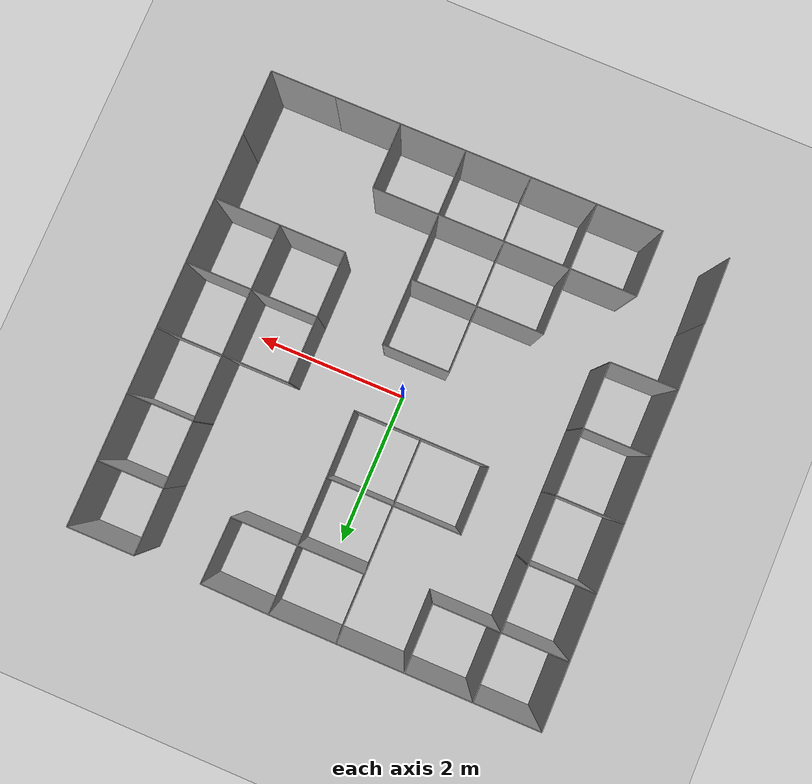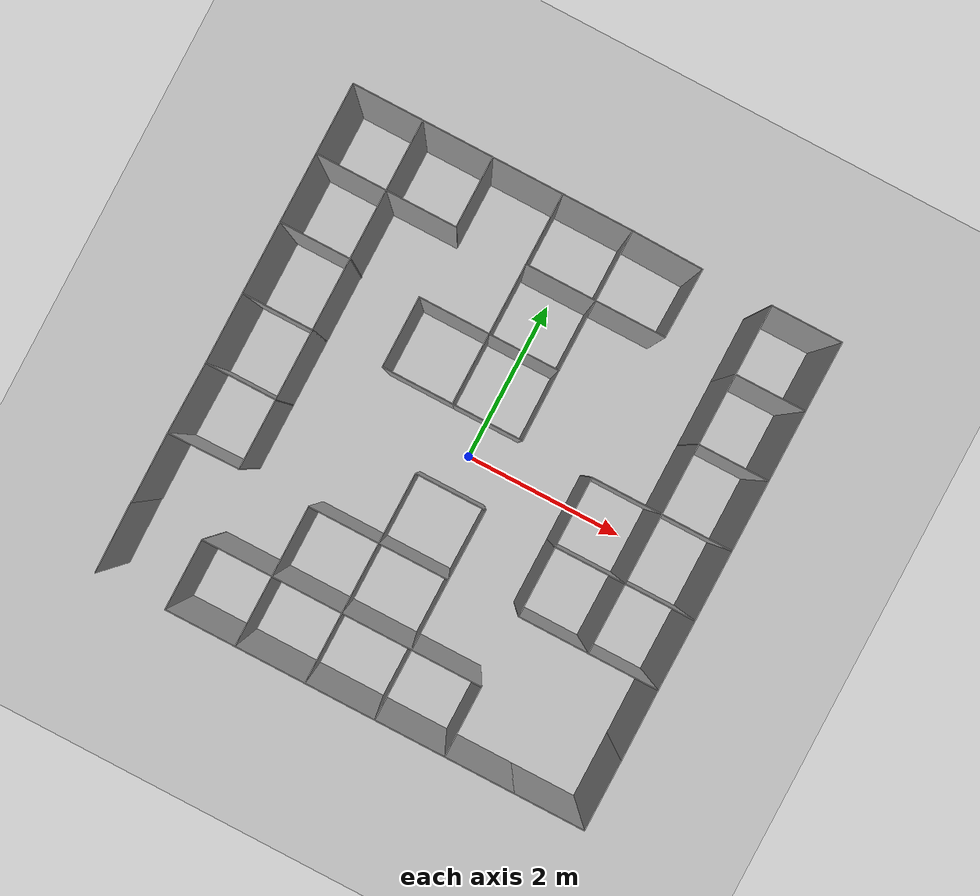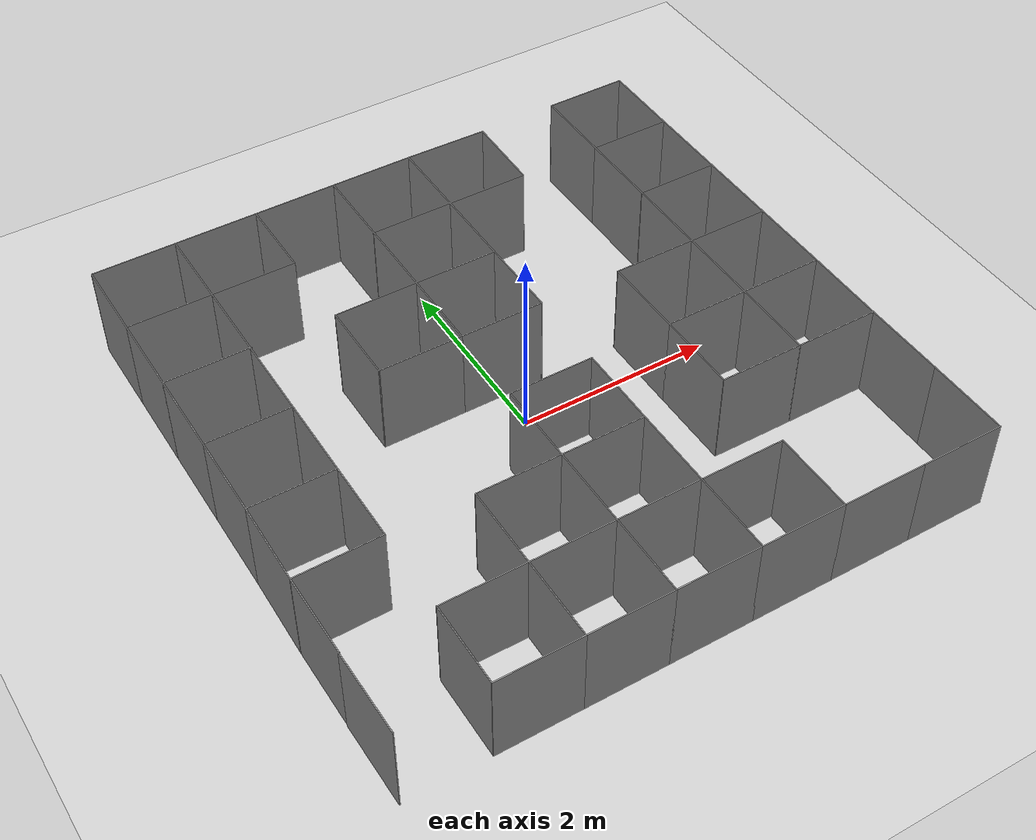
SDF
<?xml version="1.0"?>
<sdf version="1.7">
  <world name="default">
    <include>
      <uri>model://sun</uri>
    </include>
    <include>
      <uri>model://ground_plane</uri>
    </include>
  <model name='Lab1'>
    <link name='Wall_100'>
      <pose>-2.54637 0.424965 0 0 -0 0</pose>
      <self_collide>0</self_collide>
      <enable_wind>0</enable_wind>
      <kinematic>0</kinematic>
      <visual name='Wall_100_Visual'>
        <pose>0 0 0.5 0 -0 0</pose>
        <geometry>
          <box>
            <size>0.86 0.01 1</size>
          </box>
        </geometry>
        <material>
          <script>
            <uri>file://media/materials/scripts/gazebo.material</uri>
            <name>Gazebo/Grey</name>
          </script>
          <ambient>1 1 1 1</ambient>
          <shader type='pixel'/>
        </material>
        <meta>
          <layer>0</layer>
        </meta>
        <transparency>0</transparency>
        <cast_shadows>1</cast_shadows>
      </visual>
      <collision name='Wall_100_Collision'>
        <laser_retro>0</laser_retro>
        <max_contacts>10</max_contacts>
        <pose>0 0 0.5 0 -0 0</pose>
        <geometry>
          <box>
            <size>0.86 0.01 1</size>
          </box>
        </geometry>
        <surface>
          <friction>
            <ode>
              <mu>1</mu>
              <mu2>1</mu2>
              <fdir1>0 0 0</fdir1>
              <slip1>0</slip1>
              <slip2>0</slip2>
            </ode>
            <torsional>
              <coefficient>1</coefficient>
              <patch_radius>0</patch_radius>
              <surface_radius>0</surface_radius>
              <use_patch_radius>1</use_patch_radius>
              <ode>
                <slip>0</slip>
              </ode>
            </torsional>
          </friction>
          <bounce>
            <restitution_coefficient>0</restitution_coefficient>
            <threshold>1e+06</threshold>
          </bounce>
          <contact>
            <collide_without_contact>0</collide_without_contact>
            <collide_without_contact_bitmask>1</collide_without_contact_bitmask>
            <collide_bitmask>1</collide_bitmask>
            <ode>
              <soft_cfm>0</soft_cfm>
              <soft_erp>0.2</soft_erp>
              <kp>1e+13</kp>
              <kd>1</kd>
              <max_vel>0.01</max_vel>
              <min_depth>0</min_depth>
            </ode>
            <bullet>
              <split_impulse>1</split_impulse>
              <split_impulse_penetration_threshold>-0.01</split_impulse_penetration_threshold>
              <soft_cfm>0</soft_cfm>
              <soft_erp>0.2</soft_erp>
              <kp>1e+13</kp>
              <kd>1</kd>
            </bullet>
          </contact>
        </surface>
      </collision>
    </link>
    <link name='Wall_101'>
      <pose>-2.12161 0.858205 0 0 -0 1.57135</pose>
      <self_collide>0</self_collide>
      <enable_wind>0</enable_wind>
      <kinematic>0</kinematic>
      <visual name='Wall_101_Visual'>
        <pose>0 0 0.5 0 -0 0</pose>
        <geometry>
          <box>
            <size>0.876839 0.01 1</size>
          </box>
        </geometry>
        <material>
          <script>
            <uri>file://media/materials/scripts/gazebo.material</uri>
            <name>Gazebo/Grey</name>
          </script>
          <ambient>1 1 1 1</ambient>
          <shader type='pixel'/>
        </material>
        <meta>
          <layer>0</layer>
        </meta>
        <transparency>0</transparency>
        <cast_shadows>1</cast_shadows>
      </visual>
      <collision name='Wall_101_Collision'>
        <laser_retro>0</laser_retro>
        <max_contacts>10</max_contacts>
        <pose>0 0 0.5 0 -0 0</pose>
        <geometry>
          <box>
            <size>0.876839 0.01 1</size>
          </box>
        </geometry>
        <surface>
          <friction>
            <ode>
              <mu>1</mu>
              <mu2>1</mu2>
              <fdir1>0 0 0</fdir1>
              <slip1>0</slip1>
              <slip2>0</slip2>
            </ode>
            <torsional>
              <coefficient>1</coefficient>
              <patch_radius>0</patch_radius>
              <surface_radius>0</surface_radius>
              <use_patch_radius>1</use_patch_radius>
              <ode>
                <slip>0</slip>
              </ode>
            </torsional>
          </friction>
          <bounce>
            <restitution_coefficient>0</restitution_coefficient>
            <threshold>1e+06</threshold>
          </bounce>
          <contact>
            <collide_without_contact>0</collide_without_contact>
            <collide_without_contact_bitmask>1</collide_without_contact_bitmask>
            <collide_bitmask>1</collide_bitmask>
            <ode>
              <soft_cfm>0</soft_cfm>
              <soft_erp>0.2</soft_erp>
              <kp>1e+13</kp>
              <kd>1</kd>
              <max_vel>0.01</max_vel>
              <min_depth>0</min_depth>
            </ode>
            <bullet>
              <split_impulse>1</split_impulse>
              <split_impulse_penetration_threshold>-0.01</split_impulse_penetration_threshold>
              <soft_cfm>0</soft_cfm>
              <soft_erp>0.2</soft_erp>
              <kp>1e+13</kp>
              <kd>1</kd>
            </bullet>
          </contact>
        </surface>
      </collision>
    </link>
    <link name='Wall_103'>
      <pose>-1.27137 0.849965 0 0 0 -1.5708</pose>
      <self_collide>0</self_collide>
      <enable_wind>0</enable_wind>
      <kinematic>0</kinematic>
      <visual name='Wall_103_Visual'>
        <pose>0 0 0.5 0 -0 0</pose>
        <geometry>
          <box>
            <size>0.86 0.01 1</size>
          </box>
        </geometry>
        <material>
          <script>
            <uri>file://media/materials/scripts/gazebo.material</uri>
            <name>Gazebo/Grey</name>
          </script>
          <ambient>1 1 1 1</ambient>
          <shader type='pixel'/>
        </material>
        <meta>
          <layer>0</layer>
        </meta>
        <transparency>0</transparency>
        <cast_shadows>1</cast_shadows>
      </visual>
      <collision name='Wall_103_Collision'>
        <laser_retro>0</laser_retro>
        <max_contacts>10</max_contacts>
        <pose>0 0 0.5 0 -0 0</pose>
        <geometry>
          <box>
            <size>0.86 0.01 1</size>
          </box>
        </geometry>
        <surface>
          <friction>
            <ode>
              <mu>1</mu>
              <mu2>1</mu2>
              <fdir1>0 0 0</fdir1>
              <slip1>0</slip1>
              <slip2>0</slip2>
            </ode>
            <torsional>
              <coefficient>1</coefficient>
              <patch_radius>0</patch_radius>
              <surface_radius>0</surface_radius>
              <use_patch_radius>1</use_patch_radius>
              <ode>
                <slip>0</slip>
              </ode>
            </torsional>
          </friction>
          <bounce>
            <restitution_coefficient>0</restitution_coefficient>
            <threshold>1e+06</threshold>
          </bounce>
          <contact>
            <collide_without_contact>0</collide_without_contact>
            <collide_without_contact_bitmask>1</collide_without_contact_bitmask>
            <collide_bitmask>1</collide_bitmask>
            <ode>
              <soft_cfm>0</soft_cfm>
              <soft_erp>0.2</soft_erp>
              <kp>1e+13</kp>
              <kd>1</kd>
              <max_vel>0.01</max_vel>
              <min_depth>0</min_depth>
            </ode>
            <bullet>
              <split_impulse>1</split_impulse>
              <split_impulse_penetration_threshold>-0.01</split_impulse_penetration_threshold>
              <soft_cfm>0</soft_cfm>
              <soft_erp>0.2</soft_erp>
              <kp>1e+13</kp>
              <kd>1</kd>
            </bullet>
          </contact>
        </surface>
      </collision>
    </link>
    <link name='Wall_104'>
      <pose>-0.846372 0.424965 0 0 -0 0</pose>
      <self_collide>0</self_collide>
      <enable_wind>0</enable_wind>
      <kinematic>0</kinematic>
      <visual name='Wall_104_Visual'>
        <pose>0 0 0.5 0 -0 0</pose>
        <geometry>
          <box>
            <size>0.86 0.01 1</size>
          </box>
        </geometry>
        <material>
          <script>
            <uri>file://media/materials/scripts/gazebo.material</uri>
            <name>Gazebo/Grey</name>
          </script>
          <ambient>1 1 1 1</ambient>
          <shader type='pixel'/>
        </material>
        <meta>
          <layer>0</layer>
        </meta>
        <transparency>0</transparency>
        <cast_shadows>1</cast_shadows>
      </visual>
      <collision name='Wall_104_Collision'>
        <laser_retro>0</laser_retro>
        <max_contacts>10</max_contacts>
        <pose>0 0 0.5 0 -0 0</pose>
        <geometry>
          <box>
            <size>0.86 0.01 1</size>
          </box>
        </geometry>
        <surface>
          <friction>
            <ode>
              <mu>1</mu>
              <mu2>1</mu2>
              <fdir1>0 0 0</fdir1>
              <slip1>0</slip1>
              <slip2>0</slip2>
            </ode>
            <torsional>
              <coefficient>1</coefficient>
              <patch_radius>0</patch_radius>
              <surface_radius>0</surface_radius>
              <use_patch_radius>1</use_patch_radius>
              <ode>
                <slip>0</slip>
              </ode>
            </torsional>
          </friction>
          <bounce>
            <restitution_coefficient>0</restitution_coefficient>
            <threshold>1e+06</threshold>
          </bounce>
          <contact>
            <collide_without_contact>0</collide_without_contact>
            <collide_without_contact_bitmask>1</collide_without_contact_bitmask>
            <collide_bitmask>1</collide_bitmask>
            <ode>
              <soft_cfm>0</soft_cfm>
              <soft_erp>0.2</soft_erp>
              <kp>1e+13</kp>
              <kd>1</kd>
              <max_vel>0.01</max_vel>
              <min_depth>0</min_depth>
            </ode>
            <bullet>
              <split_impulse>1</split_impulse>
              <split_impulse_penetration_threshold>-0.01</split_impulse_penetration_threshold>
              <soft_cfm>0</soft_cfm>
              <soft_erp>0.2</soft_erp>
              <kp>1e+13</kp>
              <kd>1</kd>
            </bullet>
          </contact>
        </surface>
      </collision>
    </link>
    <link name='Wall_105'>
      <pose>-0.421372 0.849965 0 0 -0 1.5708</pose>
      <self_collide>0</self_collide>
      <enable_wind>0</enable_wind>
      <kinematic>0</kinematic>
      <visual name='Wall_105_Visual'>
        <pose>0 0 0.5 0 -0 0</pose>
        <geometry>
          <box>
            <size>0.859555 0.01 1</size>
          </box>
        </geometry>
        <material>
          <script>
            <uri>file://media/materials/scripts/gazebo.material</uri>
            <name>Gazebo/Grey</name>
          </script>
          <ambient>1 1 1 1</ambient>
          <shader type='pixel'/>
        </material>
        <meta>
          <layer>0</layer>
        </meta>
        <transparency>0</transparency>
        <cast_shadows>1</cast_shadows>
      </visual>
      <collision name='Wall_105_Collision'>
        <laser_retro>0</laser_retro>
        <max_contacts>10</max_contacts>
        <pose>0 0 0.5 0 -0 0</pose>
        <geometry>
          <box>
            <size>0.859555 0.01 1</size>
          </box>
        </geometry>
        <surface>
          <friction>
            <ode>
              <mu>1</mu>
              <mu2>1</mu2>
              <fdir1>0 0 0</fdir1>
              <slip1>0</slip1>
              <slip2>0</slip2>
            </ode>
            <torsional>
              <coefficient>1</coefficient>
              <patch_radius>0</patch_radius>
              <surface_radius>0</surface_radius>
              <use_patch_radius>1</use_patch_radius>
              <ode>
                <slip>0</slip>
              </ode>
            </torsional>
          </friction>
          <bounce>
            <restitution_coefficient>0</restitution_coefficient>
            <threshold>1e+06</threshold>
          </bounce>
          <contact>
            <collide_without_contact>0</collide_without_contact>
            <collide_without_contact_bitmask>1</collide_without_contact_bitmask>
            <collide_bitmask>1</collide_bitmask>
            <ode>
              <soft_cfm>0</soft_cfm>
              <soft_erp>0.2</soft_erp>
              <kp>1e+13</kp>
              <kd>1</kd>
              <max_vel>0.01</max_vel>
              <min_depth>0</min_depth>
            </ode>
            <bullet>
              <split_impulse>1</split_impulse>
              <split_impulse_penetration_threshold>-0.01</split_impulse_penetration_threshold>
              <soft_cfm>0</soft_cfm>
              <soft_erp>0.2</soft_erp>
              <kp>1e+13</kp>
              <kd>1</kd>
            </bullet>
          </contact>
        </surface>
      </collision>
    </link>
    <link name='Wall_106'>
      <pose>0.003628 1.27496 0 0 -0 0</pose>
      <self_collide>0</self_collide>
      <enable_wind>0</enable_wind>
      <kinematic>0</kinematic>
      <visual name='Wall_106_Visual'>
        <pose>0 0 0.5 0 -0 0</pose>
        <geometry>
          <box>
            <size>0.86 0.01 1</size>
          </box>
        </geometry>
        <material>
          <script>
            <uri>file://media/materials/scripts/gazebo.material</uri>
            <name>Gazebo/Grey</name>
          </script>
          <ambient>1 1 1 1</ambient>
          <shader type='pixel'/>
        </material>
        <meta>
          <layer>0</layer>
        </meta>
        <transparency>0</transparency>
        <cast_shadows>1</cast_shadows>
      </visual>
      <collision name='Wall_106_Collision'>
        <laser_retro>0</laser_retro>
        <max_contacts>10</max_contacts>
        <pose>0 0 0.5 0 -0 0</pose>
        <geometry>
          <box>
            <size>0.86 0.01 1</size>
          </box>
        </geometry>
        <surface>
          <friction>
            <ode>
              <mu>1</mu>
              <mu2>1</mu2>
              <fdir1>0 0 0</fdir1>
              <slip1>0</slip1>
              <slip2>0</slip2>
            </ode>
            <torsional>
              <coefficient>1</coefficient>
              <patch_radius>0</patch_radius>
              <surface_radius>0</surface_radius>
              <use_patch_radius>1</use_patch_radius>
              <ode>
                <slip>0</slip>
              </ode>
            </torsional>
          </friction>
          <bounce>
            <restitution_coefficient>0</restitution_coefficient>
            <threshold>1e+06</threshold>
          </bounce>
          <contact>
            <collide_without_contact>0</collide_without_contact>
            <collide_without_contact_bitmask>1</collide_without_contact_bitmask>
            <collide_bitmask>1</collide_bitmask>
            <ode>
              <soft_cfm>0</soft_cfm>
              <soft_erp>0.2</soft_erp>
              <kp>1e+13</kp>
              <kd>1</kd>
              <max_vel>0.01</max_vel>
              <min_depth>0</min_depth>
            </ode>
            <bullet>
              <split_impulse>1</split_impulse>
              <split_impulse_penetration_threshold>-0.01</split_impulse_penetration_threshold>
              <soft_cfm>0</soft_cfm>
              <soft_erp>0.2</soft_erp>
              <kp>1e+13</kp>
              <kd>1</kd>
            </bullet>
          </contact>
        </surface>
      </collision>
    </link>
    <link name='Wall_107'>
      <pose>0.432128 0.849965 0 0 0 -1.56256</pose>
      <self_collide>0</self_collide>
      <enable_wind>0</enable_wind>
      <kinematic>0</kinematic>
      <visual name='Wall_107_Visual'>
        <pose>0 0 0.5 0 -0 0</pose>
        <geometry>
          <box>
            <size>0.860029 0.01 1</size>
          </box>
        </geometry>
        <material>
          <script>
            <uri>file://media/materials/scripts/gazebo.material</uri>
            <name>Gazebo/Grey</name>
          </script>
          <ambient>1 1 1 1</ambient>
          <shader type='pixel'/>
        </material>
        <meta>
          <layer>0</layer>
        </meta>
        <transparency>0</transparency>
        <cast_shadows>1</cast_shadows>
      </visual>
      <collision name='Wall_107_Collision'>
        <laser_retro>0</laser_retro>
        <max_contacts>10</max_contacts>
        <pose>0 0 0.5 0 -0 0</pose>
        <geometry>
          <box>
            <size>0.860029 0.01 1</size>
          </box>
        </geometry>
        <surface>
          <friction>
            <ode>
              <mu>1</mu>
              <mu2>1</mu2>
              <fdir1>0 0 0</fdir1>
              <slip1>0</slip1>
              <slip2>0</slip2>
            </ode>
            <torsional>
              <coefficient>1</coefficient>
              <patch_radius>0</patch_radius>
              <surface_radius>0</surface_radius>
              <use_patch_radius>1</use_patch_radius>
              <ode>
                <slip>0</slip>
              </ode>
            </torsional>
          </friction>
          <bounce>
            <restitution_coefficient>0</restitution_coefficient>
            <threshold>1e+06</threshold>
          </bounce>
          <contact>
            <collide_without_contact>0</collide_without_contact>
            <collide_without_contact_bitmask>1</collide_without_contact_bitmask>
            <collide_bitmask>1</collide_bitmask>
            <ode>
              <soft_cfm>0</soft_cfm>
              <soft_erp>0.2</soft_erp>
              <kp>1e+13</kp>
              <kd>1</kd>
              <max_vel>0.01</max_vel>
              <min_depth>0</min_depth>
            </ode>
            <bullet>
              <split_impulse>1</split_impulse>
              <split_impulse_penetration_threshold>-0.01</split_impulse_penetration_threshold>
              <soft_cfm>0</soft_cfm>
              <soft_erp>0.2</soft_erp>
              <kp>1e+13</kp>
              <kd>1</kd>
            </bullet>
          </contact>
        </surface>
      </collision>
    </link>
    <link name='Wall_111'>
      <pose>2.12863 0.849965 0 0 0 -1.5708</pose>
      <self_collide>0</self_collide>
      <enable_wind>0</enable_wind>
      <kinematic>0</kinematic>
      <visual name='Wall_111_Visual'>
        <pose>0 0 0.5 0 -0 0</pose>
        <geometry>
          <box>
            <size>0.86 0.01 1</size>
          </box>
        </geometry>
        <material>
          <script>
            <uri>file://media/materials/scripts/gazebo.material</uri>
            <name>Gazebo/Grey</name>
          </script>
          <ambient>1 1 1 1</ambient>
          <shader type='pixel'/>
        </material>
        <meta>
          <layer>0</layer>
        </meta>
        <transparency>0</transparency>
        <cast_shadows>1</cast_shadows>
      </visual>
      <collision name='Wall_111_Collision'>
        <laser_retro>0</laser_retro>
        <max_contacts>10</max_contacts>
        <pose>0 0 0.5 0 -0 0</pose>
        <geometry>
          <box>
            <size>0.86 0.01 1</size>
          </box>
        </geometry>
        <surface>
          <friction>
            <ode>
              <mu>1</mu>
              <mu2>1</mu2>
              <fdir1>0 0 0</fdir1>
              <slip1>0</slip1>
              <slip2>0</slip2>
            </ode>
            <torsional>
              <coefficient>1</coefficient>
              <patch_radius>0</patch_radius>
              <surface_radius>0</surface_radius>
              <use_patch_radius>1</use_patch_radius>
              <ode>
                <slip>0</slip>
              </ode>
            </torsional>
          </friction>
          <bounce>
            <restitution_coefficient>0</restitution_coefficient>
            <threshold>1e+06</threshold>
          </bounce>
          <contact>
            <collide_without_contact>0</collide_without_contact>
            <collide_without_contact_bitmask>1</collide_without_contact_bitmask>
            <collide_bitmask>1</collide_bitmask>
            <ode>
              <soft_cfm>0</soft_cfm>
              <soft_erp>0.2</soft_erp>
              <kp>1e+13</kp>
              <kd>1</kd>
              <max_vel>0.01</max_vel>
              <min_depth>0</min_depth>
            </ode>
            <bullet>
              <split_impulse>1</split_impulse>
              <split_impulse_penetration_threshold>-0.01</split_impulse_penetration_threshold>
              <soft_cfm>0</soft_cfm>
              <soft_erp>0.2</soft_erp>
              <kp>1e+13</kp>
              <kd>1</kd>
            </bullet>
          </contact>
        </surface>
      </collision>
    </link>
    <link name='Wall_112'>
      <pose>2.55363 0.424965 0 0 -0 0</pose>
      <self_collide>0</self_collide>
      <enable_wind>0</enable_wind>
      <kinematic>0</kinematic>
      <visual name='Wall_112_Visual'>
        <pose>0 0 0.5 0 -0 0</pose>
        <geometry>
          <box>
            <size>0.86 0.01 1</size>
          </box>
        </geometry>
        <material>
          <script>
            <uri>file://media/materials/scripts/gazebo.material</uri>
            <name>Gazebo/Grey</name>
          </script>
          <ambient>1 1 1 1</ambient>
          <shader type='pixel'/>
        </material>
        <meta>
          <layer>0</layer>
        </meta>
        <transparency>0</transparency>
        <cast_shadows>1</cast_shadows>
      </visual>
      <collision name='Wall_112_Collision'>
        <laser_retro>0</laser_retro>
        <max_contacts>10</max_contacts>
        <pose>0 0 0.5 0 -0 0</pose>
        <geometry>
          <box>
            <size>0.86 0.01 1</size>
          </box>
        </geometry>
        <surface>
          <friction>
            <ode>
              <mu>1</mu>
              <mu2>1</mu2>
              <fdir1>0 0 0</fdir1>
              <slip1>0</slip1>
              <slip2>0</slip2>
            </ode>
            <torsional>
              <coefficient>1</coefficient>
              <patch_radius>0</patch_radius>
              <surface_radius>0</surface_radius>
              <use_patch_radius>1</use_patch_radius>
              <ode>
                <slip>0</slip>
              </ode>
            </torsional>
          </friction>
          <bounce>
            <restitution_coefficient>0</restitution_coefficient>
            <threshold>1e+06</threshold>
          </bounce>
          <contact>
            <collide_without_contact>0</collide_without_contact>
            <collide_without_contact_bitmask>1</collide_without_contact_bitmask>
            <collide_bitmask>1</collide_bitmask>
            <ode>
              <soft_cfm>0</soft_cfm>
              <soft_erp>0.2</soft_erp>
              <kp>1e+13</kp>
              <kd>1</kd>
              <max_vel>0.01</max_vel>
              <min_depth>0</min_depth>
            </ode>
            <bullet>
              <split_impulse>1</split_impulse>
              <split_impulse_penetration_threshold>-0.01</split_impulse_penetration_threshold>
              <soft_cfm>0</soft_cfm>
              <soft_erp>0.2</soft_erp>
              <kp>1e+13</kp>
              <kd>1</kd>
            </bullet>
          </contact>
        </surface>
      </collision>
    </link>
    <link name='Wall_115'>
      <pose>2.55363 1.27496 0 0 -0 3.14159</pose>
      <self_collide>0</self_collide>
      <enable_wind>0</enable_wind>
      <kinematic>0</kinematic>
      <visual name='Wall_115_Visual'>
        <pose>0 0 0.5 0 -0 0</pose>
        <geometry>
          <box>
            <size>0.86 0.01 1</size>
          </box>
        </geometry>
        <material>
          <script>
            <uri>file://media/materials/scripts/gazebo.material</uri>
            <name>Gazebo/Grey</name>
          </script>
          <ambient>1 1 1 1</ambient>
          <shader type='pixel'/>
        </material>
        <meta>
          <layer>0</layer>
        </meta>
        <transparency>0</transparency>
        <cast_shadows>1</cast_shadows>
      </visual>
      <collision name='Wall_115_Collision'>
        <laser_retro>0</laser_retro>
        <max_contacts>10</max_contacts>
        <pose>0 0 0.5 0 -0 0</pose>
        <geometry>
          <box>
            <size>0.86 0.01 1</size>
          </box>
        </geometry>
        <surface>
          <friction>
            <ode>
              <mu>1</mu>
              <mu2>1</mu2>
              <fdir1>0 0 0</fdir1>
              <slip1>0</slip1>
              <slip2>0</slip2>
            </ode>
            <torsional>
              <coefficient>1</coefficient>
              <patch_radius>0</patch_radius>
              <surface_radius>0</surface_radius>
              <use_patch_radius>1</use_patch_radius>
              <ode>
                <slip>0</slip>
              </ode>
            </torsional>
          </friction>
          <bounce>
            <restitution_coefficient>0</restitution_coefficient>
            <threshold>1e+06</threshold>
          </bounce>
          <contact>
            <collide_without_contact>0</collide_without_contact>
            <collide_without_contact_bitmask>1</collide_without_contact_bitmask>
            <collide_bitmask>1</collide_bitmask>
            <ode>
              <soft_cfm>0</soft_cfm>
              <soft_erp>0.2</soft_erp>
              <kp>1e+13</kp>
              <kd>1</kd>
              <max_vel>0.01</max_vel>
              <min_depth>0</min_depth>
            </ode>
            <bullet>
              <split_impulse>1</split_impulse>
              <split_impulse_penetration_threshold>-0.01</split_impulse_penetration_threshold>
              <soft_cfm>0</soft_cfm>
              <soft_erp>0.2</soft_erp>
              <kp>1e+13</kp>
              <kd>1</kd>
            </bullet>
          </contact>
        </surface>
      </collision>
    </link>
    <link name='Wall_116'>
      <pose>2.12863 1.69996 0 0 -0 1.5708</pose>
      <self_collide>0</self_collide>
      <enable_wind>0</enable_wind>
      <kinematic>0</kinematic>
      <visual name='Wall_116_Visual'>
        <pose>0 0 0.5 0 -0 0</pose>
        <geometry>
          <box>
            <size>0.859555 0.01 1</size>
          </box>
        </geometry>
        <material>
          <script>
            <uri>file://media/materials/scripts/gazebo.material</uri>
            <name>Gazebo/Grey</name>
          </script>
          <ambient>1 1 1 1</ambient>
          <shader type='pixel'/>
        </material>
        <meta>
          <layer>0</layer>
        </meta>
        <transparency>0</transparency>
        <cast_shadows>1</cast_shadows>
      </visual>
      <collision name='Wall_116_Collision'>
        <laser_retro>0</laser_retro>
        <max_contacts>10</max_contacts>
        <pose>0 0 0.5 0 -0 0</pose>
        <geometry>
          <box>
            <size>0.859555 0.01 1</size>
          </box>
        </geometry>
        <surface>
          <friction>
            <ode>
              <mu>1</mu>
              <mu2>1</mu2>
              <fdir1>0 0 0</fdir1>
              <slip1>0</slip1>
              <slip2>0</slip2>
            </ode>
            <torsional>
              <coefficient>1</coefficient>
              <patch_radius>0</patch_radius>
              <surface_radius>0</surface_radius>
              <use_patch_radius>1</use_patch_radius>
              <ode>
                <slip>0</slip>
              </ode>
            </torsional>
          </friction>
          <bounce>
            <restitution_coefficient>0</restitution_coefficient>
            <threshold>1e+06</threshold>
          </bounce>
          <contact>
            <collide_without_contact>0</collide_without_contact>
            <collide_without_contact_bitmask>1</collide_without_contact_bitmask>
            <collide_bitmask>1</collide_bitmask>
            <ode>
              <soft_cfm>0</soft_cfm>
              <soft_erp>0.2</soft_erp>
              <kp>1e+13</kp>
              <kd>1</kd>
              <max_vel>0.01</max_vel>
              <min_depth>0</min_depth>
            </ode>
            <bullet>
              <split_impulse>1</split_impulse>
              <split_impulse_penetration_threshold>-0.01</split_impulse_penetration_threshold>
              <soft_cfm>0</soft_cfm>
              <soft_erp>0.2</soft_erp>
              <kp>1e+13</kp>
              <kd>1</kd>
            </bullet>
          </contact>
        </surface>
      </collision>
    </link>
    <link name='Wall_120'>
      <pose>0.428628 1.69996 0 0 -0 1.5708</pose>
      <self_collide>0</self_collide>
      <enable_wind>0</enable_wind>
      <kinematic>0</kinematic>
      <visual name='Wall_120_Visual'>
        <pose>0 0 0.5 0 -0 0</pose>
        <geometry>
          <box>
            <size>0.859555 0.01 1</size>
          </box>
        </geometry>
        <material>
          <script>
            <uri>file://media/materials/scripts/gazebo.material</uri>
            <name>Gazebo/Grey</name>
          </script>
          <ambient>1 1 1 1</ambient>
          <shader type='pixel'/>
        </material>
        <meta>
          <layer>0</layer>
        </meta>
        <transparency>0</transparency>
        <cast_shadows>1</cast_shadows>
      </visual>
      <collision name='Wall_120_Collision'>
        <laser_retro>0</laser_retro>
        <max_contacts>10</max_contacts>
        <pose>0 0 0.5 0 -0 0</pose>
        <geometry>
          <box>
            <size>0.859555 0.01 1</size>
          </box>
        </geometry>
        <surface>
          <friction>
            <ode>
              <mu>1</mu>
              <mu2>1</mu2>
              <fdir1>0 0 0</fdir1>
              <slip1>0</slip1>
              <slip2>0</slip2>
            </ode>
            <torsional>
              <coefficient>1</coefficient>
              <patch_radius>0</patch_radius>
              <surface_radius>0</surface_radius>
              <use_patch_radius>1</use_patch_radius>
              <ode>
                <slip>0</slip>
              </ode>
            </torsional>
          </friction>
          <bounce>
            <restitution_coefficient>0</restitution_coefficient>
            <threshold>1e+06</threshold>
          </bounce>
          <contact>
            <collide_without_contact>0</collide_without_contact>
            <collide_without_contact_bitmask>1</collide_without_contact_bitmask>
            <collide_bitmask>1</collide_bitmask>
            <ode>
              <soft_cfm>0</soft_cfm>
              <soft_erp>0.2</soft_erp>
              <kp>1e+13</kp>
              <kd>1</kd>
              <max_vel>0.01</max_vel>
              <min_depth>0</min_depth>
            </ode>
            <bullet>
              <split_impulse>1</split_impulse>
              <split_impulse_penetration_threshold>-0.01</split_impulse_penetration_threshold>
              <soft_cfm>0</soft_cfm>
              <soft_erp>0.2</soft_erp>
              <kp>1e+13</kp>
              <kd>1</kd>
            </bullet>
          </contact>
        </surface>
      </collision>
    </link>
    <link name='Wall_121'>
      <pose>0.003628 2.12496 0 0 -0 3.14159</pose>
      <self_collide>0</self_collide>
      <enable_wind>0</enable_wind>
      <kinematic>0</kinematic>
      <visual name='Wall_121_Visual'>
        <pose>0 0 0.5 0 -0 0</pose>
        <geometry>
          <box>
            <size>0.86 0.01 1</size>
          </box>
        </geometry>
        <material>
          <script>
            <uri>file://media/materials/scripts/gazebo.material</uri>
            <name>Gazebo/Grey</name>
          </script>
          <ambient>1 1 1 1</ambient>
          <shader type='pixel'/>
        </material>
        <meta>
          <layer>0</layer>
        </meta>
        <transparency>0</transparency>
        <cast_shadows>1</cast_shadows>
      </visual>
      <collision name='Wall_121_Collision'>
        <laser_retro>0</laser_retro>
        <max_contacts>10</max_contacts>
        <pose>0 0 0.5 0 -0 0</pose>
        <geometry>
          <box>
            <size>0.86 0.01 1</size>
          </box>
        </geometry>
        <surface>
          <friction>
            <ode>
              <mu>1</mu>
              <mu2>1</mu2>
              <fdir1>0 0 0</fdir1>
              <slip1>0</slip1>
              <slip2>0</slip2>
            </ode>
            <torsional>
              <coefficient>1</coefficient>
              <patch_radius>0</patch_radius>
              <surface_radius>0</surface_radius>
              <use_patch_radius>1</use_patch_radius>
              <ode>
                <slip>0</slip>
              </ode>
            </torsional>
          </friction>
          <bounce>
            <restitution_coefficient>0</restitution_coefficient>
            <threshold>1e+06</threshold>
          </bounce>
          <contact>
            <collide_without_contact>0</collide_without_contact>
            <collide_without_contact_bitmask>1</collide_without_contact_bitmask>
            <collide_bitmask>1</collide_bitmask>
            <ode>
              <soft_cfm>0</soft_cfm>
              <soft_erp>0.2</soft_erp>
              <kp>1e+13</kp>
              <kd>1</kd>
              <max_vel>0.01</max_vel>
              <min_depth>0</min_depth>
            </ode>
            <bullet>
              <split_impulse>1</split_impulse>
              <split_impulse_penetration_threshold>-0.01</split_impulse_penetration_threshold>
              <soft_cfm>0</soft_cfm>
              <soft_erp>0.2</soft_erp>
              <kp>1e+13</kp>
              <kd>1</kd>
            </bullet>
          </contact>
        </surface>
      </collision>
    </link>
    <link name='Wall_122'>
      <pose>-0.421372 1.69996 0 0 0 -1.5708</pose>
      <self_collide>0</self_collide>
      <enable_wind>0</enable_wind>
      <kinematic>0</kinematic>
      <visual name='Wall_122_Visual'>
        <pose>0 0 0.5 0 -0 0</pose>
        <geometry>
          <box>
            <size>0.86 0.01 1</size>
          </box>
        </geometry>
        <material>
          <script>
            <uri>file://media/materials/scripts/gazebo.material</uri>
            <name>Gazebo/Grey</name>
          </script>
          <ambient>1 1 1 1</ambient>
          <shader type='pixel'/>
        </material>
        <meta>
          <layer>0</layer>
        </meta>
        <transparency>0</transparency>
        <cast_shadows>1</cast_shadows>
      </visual>
      <collision name='Wall_122_Collision'>
        <laser_retro>0</laser_retro>
        <max_contacts>10</max_contacts>
        <pose>0 0 0.5 0 -0 0</pose>
        <geometry>
          <box>
            <size>0.86 0.01 1</size>
          </box>
        </geometry>
        <surface>
          <friction>
            <ode>
              <mu>1</mu>
              <mu2>1</mu2>
              <fdir1>0 0 0</fdir1>
              <slip1>0</slip1>
              <slip2>0</slip2>
            </ode>
            <torsional>
              <coefficient>1</coefficient>
              <patch_radius>0</patch_radius>
              <surface_radius>0</surface_radius>
              <use_patch_radius>1</use_patch_radius>
              <ode>
                <slip>0</slip>
              </ode>
            </torsional>
          </friction>
          <bounce>
            <restitution_coefficient>0</restitution_coefficient>
            <threshold>1e+06</threshold>
          </bounce>
          <contact>
            <collide_without_contact>0</collide_without_contact>
            <collide_without_contact_bitmask>1</collide_without_contact_bitmask>
            <collide_bitmask>1</collide_bitmask>
            <ode>
              <soft_cfm>0</soft_cfm>
              <soft_erp>0.2</soft_erp>
              <kp>1e+13</kp>
              <kd>1</kd>
              <max_vel>0.01</max_vel>
              <min_depth>0</min_depth>
            </ode>
            <bullet>
              <split_impulse>1</split_impulse>
              <split_impulse_penetration_threshold>-0.01</split_impulse_penetration_threshold>
              <soft_cfm>0</soft_cfm>
              <soft_erp>0.2</soft_erp>
              <kp>1e+13</kp>
              <kd>1</kd>
            </bullet>
          </contact>
        </surface>
      </collision>
    </link>
    <link name='Wall_123'>
      <pose>-0.846372 1.27496 0 0 -0 3.14159</pose>
      <self_collide>0</self_collide>
      <enable_wind>0</enable_wind>
      <kinematic>0</kinematic>
      <visual name='Wall_123_Visual'>
        <pose>0 0 0.5 0 -0 0</pose>
        <geometry>
          <box>
            <size>0.86 0.01 1</size>
          </box>
        </geometry>
        <material>
          <script>
            <uri>file://media/materials/scripts/gazebo.material</uri>
            <name>Gazebo/Grey</name>
          </script>
          <ambient>1 1 1 1</ambient>
          <shader type='pixel'/>
        </material>
        <meta>
          <layer>0</layer>
        </meta>
        <transparency>0</transparency>
        <cast_shadows>1</cast_shadows>
      </visual>
      <collision name='Wall_123_Collision'>
        <laser_retro>0</laser_retro>
        <max_contacts>10</max_contacts>
        <pose>0 0 0.5 0 -0 0</pose>
        <geometry>
          <box>
            <size>0.86 0.01 1</size>
          </box>
        </geometry>
        <surface>
          <friction>
            <ode>
              <mu>1</mu>
              <mu2>1</mu2>
              <fdir1>0 0 0</fdir1>
              <slip1>0</slip1>
              <slip2>0</slip2>
            </ode>
            <torsional>
              <coefficient>1</coefficient>
              <patch_radius>0</patch_radius>
              <surface_radius>0</surface_radius>
              <use_patch_radius>1</use_patch_radius>
              <ode>
                <slip>0</slip>
              </ode>
            </torsional>
          </friction>
          <bounce>
            <restitution_coefficient>0</restitution_coefficient>
            <threshold>1e+06</threshold>
          </bounce>
          <contact>
            <collide_without_contact>0</collide_without_contact>
            <collide_without_contact_bitmask>1</collide_without_contact_bitmask>
            <collide_bitmask>1</collide_bitmask>
            <ode>
              <soft_cfm>0</soft_cfm>
              <soft_erp>0.2</soft_erp>
              <kp>1e+13</kp>
              <kd>1</kd>
              <max_vel>0.01</max_vel>
              <min_depth>0</min_depth>
            </ode>
            <bullet>
              <split_impulse>1</split_impulse>
              <split_impulse_penetration_threshold>-0.01</split_impulse_penetration_threshold>
              <soft_cfm>0</soft_cfm>
              <soft_erp>0.2</soft_erp>
              <kp>1e+13</kp>
              <kd>1</kd>
            </bullet>
          </contact>
        </surface>
      </collision>
    </link>
    <link name='Wall_125'>
      <pose>-1.69637 2.12496 0 0 -0 3.14159</pose>
      <self_collide>0</self_collide>
      <enable_wind>0</enable_wind>
      <kinematic>0</kinematic>
      <visual name='Wall_125_Visual'>
        <pose>0 0 0.5 0 -0 0</pose>
        <geometry>
          <box>
            <size>0.86 0.01 1</size>
          </box>
        </geometry>
        <material>
          <script>
            <uri>file://media/materials/scripts/gazebo.material</uri>
            <name>Gazebo/Grey</name>
          </script>
          <ambient>1 1 1 1</ambient>
          <shader type='pixel'/>
        </material>
        <meta>
          <layer>0</layer>
        </meta>
        <transparency>0</transparency>
        <cast_shadows>1</cast_shadows>
      </visual>
      <collision name='Wall_125_Collision'>
        <laser_retro>0</laser_retro>
        <max_contacts>10</max_contacts>
        <pose>0 0 0.5 0 -0 0</pose>
        <geometry>
          <box>
            <size>0.86 0.01 1</size>
          </box>
        </geometry>
        <surface>
          <friction>
            <ode>
              <mu>1</mu>
              <mu2>1</mu2>
              <fdir1>0 0 0</fdir1>
              <slip1>0</slip1>
              <slip2>0</slip2>
            </ode>
            <torsional>
              <coefficient>1</coefficient>
              <patch_radius>0</patch_radius>
              <surface_radius>0</surface_radius>
              <use_patch_radius>1</use_patch_radius>
              <ode>
                <slip>0</slip>
              </ode>
            </torsional>
          </friction>
          <bounce>
            <restitution_coefficient>0</restitution_coefficient>
            <threshold>1e+06</threshold>
          </bounce>
          <contact>
            <collide_without_contact>0</collide_without_contact>
            <collide_without_contact_bitmask>1</collide_without_contact_bitmask>
            <collide_bitmask>1</collide_bitmask>
            <ode>
              <soft_cfm>0</soft_cfm>
              <soft_erp>0.2</soft_erp>
              <kp>1e+13</kp>
              <kd>1</kd>
              <max_vel>0.01</max_vel>
              <min_depth>0</min_depth>
            </ode>
            <bullet>
              <split_impulse>1</split_impulse>
              <split_impulse_penetration_threshold>-0.01</split_impulse_penetration_threshold>
              <soft_cfm>0</soft_cfm>
              <soft_erp>0.2</soft_erp>
              <kp>1e+13</kp>
              <kd>1</kd>
            </bullet>
          </contact>
        </surface>
      </collision>
    </link>
    <link name='Wall_126'>
      <pose>-2.12161 1.7082 0 0 0 -1.57137</pose>
      <self_collide>0</self_collide>
      <enable_wind>0</enable_wind>
      <kinematic>0</kinematic>
      <visual name='Wall_126_Visual'>
        <pose>0 0 0.5 0 -0 0</pose>
        <geometry>
          <box>
            <size>0.843894 0.01 1</size>
          </box>
        </geometry>
        <material>
          <script>
            <uri>file://media/materials/scripts/gazebo.material</uri>
            <name>Gazebo/Grey</name>
          </script>
          <ambient>1 1 1 1</ambient>
          <shader type='pixel'/>
        </material>
        <meta>
          <layer>0</layer>
        </meta>
        <transparency>0</transparency>
        <cast_shadows>1</cast_shadows>
      </visual>
      <collision name='Wall_126_Collision'>
        <laser_retro>0</laser_retro>
        <max_contacts>10</max_contacts>
        <pose>0 0 0.5 0 -0 0</pose>
        <geometry>
          <box>
            <size>0.843894 0.01 1</size>
          </box>
        </geometry>
        <surface>
          <friction>
            <ode>
              <mu>1</mu>
              <mu2>1</mu2>
              <fdir1>0 0 0</fdir1>
              <slip1>0</slip1>
              <slip2>0</slip2>
            </ode>
            <torsional>
              <coefficient>1</coefficient>
              <patch_radius>0</patch_radius>
              <surface_radius>0</surface_radius>
              <use_patch_radius>1</use_patch_radius>
              <ode>
                <slip>0</slip>
              </ode>
            </torsional>
          </friction>
          <bounce>
            <restitution_coefficient>0</restitution_coefficient>
            <threshold>1e+06</threshold>
          </bounce>
          <contact>
            <collide_without_contact>0</collide_without_contact>
            <collide_without_contact_bitmask>1</collide_without_contact_bitmask>
            <collide_bitmask>1</collide_bitmask>
            <ode>
              <soft_cfm>0</soft_cfm>
              <soft_erp>0.2</soft_erp>
              <kp>1e+13</kp>
              <kd>1</kd>
              <max_vel>0.01</max_vel>
              <min_depth>0</min_depth>
            </ode>
            <bullet>
              <split_impulse>1</split_impulse>
              <split_impulse_penetration_threshold>-0.01</split_impulse_penetration_threshold>
              <soft_cfm>0</soft_cfm>
              <soft_erp>0.2</soft_erp>
              <kp>1e+13</kp>
              <kd>1</kd>
            </bullet>
          </contact>
        </surface>
      </collision>
    </link>
    <link name='Wall_127'>
      <pose>-2.54237 1.2912 0 0 0 -3.14103</pose>
      <self_collide>0</self_collide>
      <enable_wind>0</enable_wind>
      <kinematic>0</kinematic>
      <visual name='Wall_127_Visual'>
        <pose>0 0 0.5 0 -0 0</pose>
        <geometry>
          <box>
            <size>0.868 0.01 1</size>
          </box>
        </geometry>
        <material>
          <script>
            <uri>file://media/materials/scripts/gazebo.material</uri>
            <name>Gazebo/Grey</name>
          </script>
          <ambient>1 1 1 1</ambient>
          <shader type='pixel'/>
        </material>
        <meta>
          <layer>0</layer>
        </meta>
        <transparency>0</transparency>
        <cast_shadows>1</cast_shadows>
      </visual>
      <collision name='Wall_127_Collision'>
        <laser_retro>0</laser_retro>
        <max_contacts>10</max_contacts>
        <pose>0 0 0.5 0 -0 0</pose>
        <geometry>
          <box>
            <size>0.868 0.01 1</size>
          </box>
        </geometry>
        <surface>
          <friction>
            <ode>
              <mu>1</mu>
              <mu2>1</mu2>
              <fdir1>0 0 0</fdir1>
              <slip1>0</slip1>
              <slip2>0</slip2>
            </ode>
            <torsional>
              <coefficient>1</coefficient>
              <patch_radius>0</patch_radius>
              <surface_radius>0</surface_radius>
              <use_patch_radius>1</use_patch_radius>
              <ode>
                <slip>0</slip>
              </ode>
            </torsional>
          </friction>
          <bounce>
            <restitution_coefficient>0</restitution_coefficient>
            <threshold>1e+06</threshold>
          </bounce>
          <contact>
            <collide_without_contact>0</collide_without_contact>
            <collide_without_contact_bitmask>1</collide_without_contact_bitmask>
            <collide_bitmask>1</collide_bitmask>
            <ode>
              <soft_cfm>0</soft_cfm>
              <soft_erp>0.2</soft_erp>
              <kp>1e+13</kp>
              <kd>1</kd>
              <max_vel>0.01</max_vel>
              <min_depth>0</min_depth>
            </ode>
            <bullet>
              <split_impulse>1</split_impulse>
              <split_impulse_penetration_threshold>-0.01</split_impulse_penetration_threshold>
              <soft_cfm>0</soft_cfm>
              <soft_erp>0.2</soft_erp>
              <kp>1e+13</kp>
              <kd>1</kd>
            </bullet>
          </contact>
        </surface>
      </collision>
    </link>
    <link name='Wall_129'>
      <pose>-2.54637 2.12496 0 0 -0 0</pose>
      <self_collide>0</self_collide>
      <enable_wind>0</enable_wind>
      <kinematic>0</kinematic>
      <visual name='Wall_129_Visual'>
        <pose>0 0 0.5 0 -0 0</pose>
        <geometry>
          <box>
            <size>0.86 0.01 1</size>
          </box>
        </geometry>
        <material>
          <script>
            <uri>file://media/materials/scripts/gazebo.material</uri>
            <name>Gazebo/Grey</name>
          </script>
          <ambient>1 1 1 1</ambient>
          <shader type='pixel'/>
        </material>
        <meta>
          <layer>0</layer>
        </meta>
        <transparency>0</transparency>
        <cast_shadows>1</cast_shadows>
      </visual>
      <collision name='Wall_129_Collision'>
        <laser_retro>0</laser_retro>
        <max_contacts>10</max_contacts>
        <pose>0 0 0.5 0 -0 0</pose>
        <geometry>
          <box>
            <size>0.86 0.01 1</size>
          </box>
        </geometry>
        <surface>
          <friction>
            <ode>
              <mu>1</mu>
              <mu2>1</mu2>
              <fdir1>0 0 0</fdir1>
              <slip1>0</slip1>
              <slip2>0</slip2>
            </ode>
            <torsional>
              <coefficient>1</coefficient>
              <patch_radius>0</patch_radius>
              <surface_radius>0</surface_radius>
              <use_patch_radius>1</use_patch_radius>
              <ode>
                <slip>0</slip>
              </ode>
            </torsional>
          </friction>
          <bounce>
            <restitution_coefficient>0</restitution_coefficient>
            <threshold>1e+06</threshold>
          </bounce>
          <contact>
            <collide_without_contact>0</collide_without_contact>
            <collide_without_contact_bitmask>1</collide_without_contact_bitmask>
            <collide_bitmask>1</collide_bitmask>
            <ode>
              <soft_cfm>0</soft_cfm>
              <soft_erp>0.2</soft_erp>
              <kp>1e+13</kp>
              <kd>1</kd>
              <max_vel>0.01</max_vel>
              <min_depth>0</min_depth>
            </ode>
            <bullet>
              <split_impulse>1</split_impulse>
              <split_impulse_penetration_threshold>-0.01</split_impulse_penetration_threshold>
              <soft_cfm>0</soft_cfm>
              <soft_erp>0.2</soft_erp>
              <kp>1e+13</kp>
              <kd>1</kd>
            </bullet>
          </contact>
        </surface>
      </collision>
    </link>
    <link name='Wall_130'>
      <pose>-2.12137 2.54996 0 0 -0 1.5708</pose>
      <self_collide>0</self_collide>
      <enable_wind>0</enable_wind>
      <kinematic>0</kinematic>
      <visual name='Wall_130_Visual'>
        <pose>0 0 0.5 0 -0 0</pose>
        <geometry>
          <box>
            <size>0.86 0.01 1</size>
          </box>
        </geometry>
        <material>
          <script>
            <uri>file://media/materials/scripts/gazebo.material</uri>
            <name>Gazebo/Grey</name>
          </script>
          <ambient>1 1 1 1</ambient>
          <shader type='pixel'/>
        </material>
        <meta>
          <layer>0</layer>
        </meta>
        <transparency>0</transparency>
        <cast_shadows>1</cast_shadows>
      </visual>
      <collision name='Wall_130_Collision'>
        <laser_retro>0</laser_retro>
        <max_contacts>10</max_contacts>
        <pose>0 0 0.5 0 -0 0</pose>
        <geometry>
          <box>
            <size>0.86 0.01 1</size>
          </box>
        </geometry>
        <surface>
          <friction>
            <ode>
              <mu>1</mu>
              <mu2>1</mu2>
              <fdir1>0 0 0</fdir1>
              <slip1>0</slip1>
              <slip2>0</slip2>
            </ode>
            <torsional>
              <coefficient>1</coefficient>
              <patch_radius>0</patch_radius>
              <surface_radius>0</surface_radius>
              <use_patch_radius>1</use_patch_radius>
              <ode>
                <slip>0</slip>
              </ode>
            </torsional>
          </friction>
          <bounce>
            <restitution_coefficient>0</restitution_coefficient>
            <threshold>1e+06</threshold>
          </bounce>
          <contact>
            <collide_without_contact>0</collide_without_contact>
            <collide_without_contact_bitmask>1</collide_without_contact_bitmask>
            <collide_bitmask>1</collide_bitmask>
            <ode>
              <soft_cfm>0</soft_cfm>
              <soft_erp>0.2</soft_erp>
              <kp>1e+13</kp>
              <kd>1</kd>
              <max_vel>0.01</max_vel>
              <min_depth>0</min_depth>
            </ode>
            <bullet>
              <split_impulse>1</split_impulse>
              <split_impulse_penetration_threshold>-0.01</split_impulse_penetration_threshold>
              <soft_cfm>0</soft_cfm>
              <soft_erp>0.2</soft_erp>
              <kp>1e+13</kp>
              <kd>1</kd>
            </bullet>
          </contact>
        </surface>
      </collision>
    </link>
    <link name='Wall_132'>
      <pose>-1.27137 2.54996 0 0 0 -1.5708</pose>
      <self_collide>0</self_collide>
      <enable_wind>0</enable_wind>
      <kinematic>0</kinematic>
      <visual name='Wall_132_Visual'>
        <pose>0 0 0.5 0 -0 0</pose>
        <geometry>
          <box>
            <size>0.86 0.01 1</size>
          </box>
        </geometry>
        <material>
          <script>
            <uri>file://media/materials/scripts/gazebo.material</uri>
            <name>Gazebo/Grey</name>
          </script>
          <ambient>1 1 1 1</ambient>
          <shader type='pixel'/>
        </material>
        <meta>
          <layer>0</layer>
        </meta>
        <transparency>0</transparency>
        <cast_shadows>1</cast_shadows>
      </visual>
      <collision name='Wall_132_Collision'>
        <laser_retro>0</laser_retro>
        <max_contacts>10</max_contacts>
        <pose>0 0 0.5 0 -0 0</pose>
        <geometry>
          <box>
            <size>0.86 0.01 1</size>
          </box>
        </geometry>
        <surface>
          <friction>
            <ode>
              <mu>1</mu>
              <mu2>1</mu2>
              <fdir1>0 0 0</fdir1>
              <slip1>0</slip1>
              <slip2>0</slip2>
            </ode>
            <torsional>
              <coefficient>1</coefficient>
              <patch_radius>0</patch_radius>
              <surface_radius>0</surface_radius>
              <use_patch_radius>1</use_patch_radius>
              <ode>
                <slip>0</slip>
              </ode>
            </torsional>
          </friction>
          <bounce>
            <restitution_coefficient>0</restitution_coefficient>
            <threshold>1e+06</threshold>
          </bounce>
          <contact>
            <collide_without_contact>0</collide_without_contact>
            <collide_without_contact_bitmask>1</collide_without_contact_bitmask>
            <collide_bitmask>1</collide_bitmask>
            <ode>
              <soft_cfm>0</soft_cfm>
              <soft_erp>0.2</soft_erp>
              <kp>1e+13</kp>
              <kd>1</kd>
              <max_vel>0.01</max_vel>
              <min_depth>0</min_depth>
            </ode>
            <bullet>
              <split_impulse>1</split_impulse>
              <split_impulse_penetration_threshold>-0.01</split_impulse_penetration_threshold>
              <soft_cfm>0</soft_cfm>
              <soft_erp>0.2</soft_erp>
              <kp>1e+13</kp>
              <kd>1</kd>
            </bullet>
          </contact>
        </surface>
      </collision>
    </link>
    <link name='Wall_134'>
      <pose>-0.421372 2.54996 0 0 -0 1.5708</pose>
      <self_collide>0</self_collide>
      <enable_wind>0</enable_wind>
      <kinematic>0</kinematic>
      <visual name='Wall_134_Visual'>
        <pose>0 0 0.5 0 -0 0</pose>
        <geometry>
          <box>
            <size>0.86 0.01 1</size>
          </box>
        </geometry>
        <material>
          <script>
            <uri>file://media/materials/scripts/gazebo.material</uri>
            <name>Gazebo/Grey</name>
          </script>
          <ambient>1 1 1 1</ambient>
          <shader type='pixel'/>
        </material>
        <meta>
          <layer>0</layer>
        </meta>
        <transparency>0</transparency>
        <cast_shadows>1</cast_shadows>
      </visual>
      <collision name='Wall_134_Collision'>
        <laser_retro>0</laser_retro>
        <max_contacts>10</max_contacts>
        <pose>0 0 0.5 0 -0 0</pose>
        <geometry>
          <box>
            <size>0.86 0.01 1</size>
          </box>
        </geometry>
        <surface>
          <friction>
            <ode>
              <mu>1</mu>
              <mu2>1</mu2>
              <fdir1>0 0 0</fdir1>
              <slip1>0</slip1>
              <slip2>0</slip2>
            </ode>
            <torsional>
              <coefficient>1</coefficient>
              <patch_radius>0</patch_radius>
              <surface_radius>0</surface_radius>
              <use_patch_radius>1</use_patch_radius>
              <ode>
                <slip>0</slip>
              </ode>
            </torsional>
          </friction>
          <bounce>
            <restitution_coefficient>0</restitution_coefficient>
            <threshold>1e+06</threshold>
          </bounce>
          <contact>
            <collide_without_contact>0</collide_without_contact>
            <collide_without_contact_bitmask>1</collide_without_contact_bitmask>
            <collide_bitmask>1</collide_bitmask>
            <ode>
              <soft_cfm>0</soft_cfm>
              <soft_erp>0.2</soft_erp>
              <kp>1e+13</kp>
              <kd>1</kd>
              <max_vel>0.01</max_vel>
              <min_depth>0</min_depth>
            </ode>
            <bullet>
              <split_impulse>1</split_impulse>
              <split_impulse_penetration_threshold>-0.01</split_impulse_penetration_threshold>
              <soft_cfm>0</soft_cfm>
              <soft_erp>0.2</soft_erp>
              <kp>1e+13</kp>
              <kd>1</kd>
            </bullet>
          </contact>
        </surface>
      </collision>
    </link>
    <link name='Wall_136'>
      <pose>0.428628 2.54996 0 0 0 -1.5708</pose>
      <self_collide>0</self_collide>
      <enable_wind>0</enable_wind>
      <kinematic>0</kinematic>
      <visual name='Wall_136_Visual'>
        <pose>0 0 0.5 0 -0 0</pose>
        <geometry>
          <box>
            <size>0.86 0.01 1</size>
          </box>
        </geometry>
        <material>
          <script>
            <uri>file://media/materials/scripts/gazebo.material</uri>
            <name>Gazebo/Grey</name>
          </script>
          <ambient>1 1 1 1</ambient>
          <shader type='pixel'/>
        </material>
        <meta>
          <layer>0</layer>
        </meta>
        <transparency>0</transparency>
        <cast_shadows>1</cast_shadows>
      </visual>
      <collision name='Wall_136_Collision'>
        <laser_retro>0</laser_retro>
        <max_contacts>10</max_contacts>
        <pose>0 0 0.5 0 -0 0</pose>
        <geometry>
          <box>
            <size>0.86 0.01 1</size>
          </box>
        </geometry>
        <surface>
          <friction>
            <ode>
              <mu>1</mu>
              <mu2>1</mu2>
              <fdir1>0 0 0</fdir1>
              <slip1>0</slip1>
              <slip2>0</slip2>
            </ode>
            <torsional>
              <coefficient>1</coefficient>
              <patch_radius>0</patch_radius>
              <surface_radius>0</surface_radius>
              <use_patch_radius>1</use_patch_radius>
              <ode>
                <slip>0</slip>
              </ode>
            </torsional>
          </friction>
          <bounce>
            <restitution_coefficient>0</restitution_coefficient>
            <threshold>1e+06</threshold>
          </bounce>
          <contact>
            <collide_without_contact>0</collide_without_contact>
            <collide_without_contact_bitmask>1</collide_without_contact_bitmask>
            <collide_bitmask>1</collide_bitmask>
            <ode>
              <soft_cfm>0</soft_cfm>
              <soft_erp>0.2</soft_erp>
              <kp>1e+13</kp>
              <kd>1</kd>
              <max_vel>0.01</max_vel>
              <min_depth>0</min_depth>
            </ode>
            <bullet>
              <split_impulse>1</split_impulse>
              <split_impulse_penetration_threshold>-0.01</split_impulse_penetration_threshold>
              <soft_cfm>0</soft_cfm>
              <soft_erp>0.2</soft_erp>
              <kp>1e+13</kp>
              <kd>1</kd>
            </bullet>
          </contact>
        </surface>
      </collision>
    </link>
    <link name='Wall_137'>
      <pose>0.850196 2.12496 0 0 -0 0</pose>
      <self_collide>0</self_collide>
      <enable_wind>0</enable_wind>
      <kinematic>0</kinematic>
      <visual name='Wall_137_Visual'>
        <pose>0 0 0.5 0 -0 0</pose>
        <geometry>
          <box>
            <size>0.853136 0.01 1</size>
          </box>
        </geometry>
        <material>
          <script>
            <uri>file://media/materials/scripts/gazebo.material</uri>
            <name>Gazebo/Grey</name>
          </script>
          <ambient>1 1 1 1</ambient>
          <shader type='pixel'/>
        </material>
        <meta>
          <layer>0</layer>
        </meta>
        <transparency>0</transparency>
        <cast_shadows>1</cast_shadows>
      </visual>
      <collision name='Wall_137_Collision'>
        <laser_retro>0</laser_retro>
        <max_contacts>10</max_contacts>
        <pose>0 0 0.5 0 -0 0</pose>
        <geometry>
          <box>
            <size>0.853136 0.01 1</size>
          </box>
        </geometry>
        <surface>
          <friction>
            <ode>
              <mu>1</mu>
              <mu2>1</mu2>
              <fdir1>0 0 0</fdir1>
              <slip1>0</slip1>
              <slip2>0</slip2>
            </ode>
            <torsional>
              <coefficient>1</coefficient>
              <patch_radius>0</patch_radius>
              <surface_radius>0</surface_radius>
              <use_patch_radius>1</use_patch_radius>
              <ode>
                <slip>0</slip>
              </ode>
            </torsional>
          </friction>
          <bounce>
            <restitution_coefficient>0</restitution_coefficient>
            <threshold>1e+06</threshold>
          </bounce>
          <contact>
            <collide_without_contact>0</collide_without_contact>
            <collide_without_contact_bitmask>1</collide_without_contact_bitmask>
            <collide_bitmask>1</collide_bitmask>
            <ode>
              <soft_cfm>0</soft_cfm>
              <soft_erp>0.2</soft_erp>
              <kp>1e+13</kp>
              <kd>1</kd>
              <max_vel>0.01</max_vel>
              <min_depth>0</min_depth>
            </ode>
            <bullet>
              <split_impulse>1</split_impulse>
              <split_impulse_penetration_threshold>-0.01</split_impulse_penetration_threshold>
              <soft_cfm>0</soft_cfm>
              <soft_erp>0.2</soft_erp>
              <kp>1e+13</kp>
              <kd>1</kd>
            </bullet>
          </contact>
        </surface>
      </collision>
    </link>
    <link name='Wall_138'>
      <pose>1.2802 2.54147 0 0 -0 1.55055</pose>
      <self_collide>0</self_collide>
      <enable_wind>0</enable_wind>
      <kinematic>0</kinematic>
      <visual name='Wall_138_Visual'>
        <pose>0 0 0.5 0 -0 0</pose>
        <geometry>
          <box>
            <size>0.84306 0.01 1</size>
          </box>
        </geometry>
        <material>
          <script>
            <uri>file://media/materials/scripts/gazebo.material</uri>
            <name>Gazebo/Grey</name>
          </script>
          <ambient>1 1 1 1</ambient>
          <shader type='pixel'/>
        </material>
        <meta>
          <layer>0</layer>
        </meta>
        <transparency>0</transparency>
        <cast_shadows>1</cast_shadows>
      </visual>
      <collision name='Wall_138_Collision'>
        <laser_retro>0</laser_retro>
        <max_contacts>10</max_contacts>
        <pose>0 0 0.5 0 -0 0</pose>
        <geometry>
          <box>
            <size>0.84306 0.01 1</size>
          </box>
        </geometry>
        <surface>
          <friction>
            <ode>
              <mu>1</mu>
              <mu2>1</mu2>
              <fdir1>0 0 0</fdir1>
              <slip1>0</slip1>
              <slip2>0</slip2>
            </ode>
            <torsional>
              <coefficient>1</coefficient>
              <patch_radius>0</patch_radius>
              <surface_radius>0</surface_radius>
              <use_patch_radius>1</use_patch_radius>
              <ode>
                <slip>0</slip>
              </ode>
            </torsional>
          </friction>
          <bounce>
            <restitution_coefficient>0</restitution_coefficient>
            <threshold>1e+06</threshold>
          </bounce>
          <contact>
            <collide_without_contact>0</collide_without_contact>
            <collide_without_contact_bitmask>1</collide_without_contact_bitmask>
            <collide_bitmask>1</collide_bitmask>
            <ode>
              <soft_cfm>0</soft_cfm>
              <soft_erp>0.2</soft_erp>
              <kp>1e+13</kp>
              <kd>1</kd>
              <max_vel>0.01</max_vel>
              <min_depth>0</min_depth>
            </ode>
            <bullet>
              <split_impulse>1</split_impulse>
              <split_impulse_penetration_threshold>-0.01</split_impulse_penetration_threshold>
              <soft_cfm>0</soft_cfm>
              <soft_erp>0.2</soft_erp>
              <kp>1e+13</kp>
              <kd>1</kd>
            </bullet>
          </contact>
        </surface>
      </collision>
    </link>
    <link name='Wall_140'>
      <pose>2.12813 2.54346 0 0 0 -1.5696</pose>
      <self_collide>0</self_collide>
      <enable_wind>0</enable_wind>
      <kinematic>0</kinematic>
      <visual name='Wall_140_Visual'>
        <pose>0 0 0.5 0 -0 0</pose>
        <geometry>
          <box>
            <size>0.847001 0.01 1</size>
          </box>
        </geometry>
        <material>
          <script>
            <uri>file://media/materials/scripts/gazebo.material</uri>
            <name>Gazebo/Grey</name>
          </script>
          <ambient>1 1 1 1</ambient>
          <shader type='pixel'/>
        </material>
        <meta>
          <layer>0</layer>
        </meta>
        <transparency>0</transparency>
        <cast_shadows>1</cast_shadows>
      </visual>
      <collision name='Wall_140_Collision'>
        <laser_retro>0</laser_retro>
        <max_contacts>10</max_contacts>
        <pose>0 0 0.5 0 -0 0</pose>
        <geometry>
          <box>
            <size>0.847001 0.01 1</size>
          </box>
        </geometry>
        <surface>
          <friction>
            <ode>
              <mu>1</mu>
              <mu2>1</mu2>
              <fdir1>0 0 0</fdir1>
              <slip1>0</slip1>
              <slip2>0</slip2>
            </ode>
            <torsional>
              <coefficient>1</coefficient>
              <patch_radius>0</patch_radius>
              <surface_radius>0</surface_radius>
              <use_patch_radius>1</use_patch_radius>
              <ode>
                <slip>0</slip>
              </ode>
            </torsional>
          </friction>
          <bounce>
            <restitution_coefficient>0</restitution_coefficient>
            <threshold>1e+06</threshold>
          </bounce>
          <contact>
            <collide_without_contact>0</collide_without_contact>
            <collide_without_contact_bitmask>1</collide_without_contact_bitmask>
            <collide_bitmask>1</collide_bitmask>
            <ode>
              <soft_cfm>0</soft_cfm>
              <soft_erp>0.2</soft_erp>
              <kp>1e+13</kp>
              <kd>1</kd>
              <max_vel>0.01</max_vel>
              <min_depth>0</min_depth>
            </ode>
            <bullet>
              <split_impulse>1</split_impulse>
              <split_impulse_penetration_threshold>-0.01</split_impulse_penetration_threshold>
              <soft_cfm>0</soft_cfm>
              <soft_erp>0.2</soft_erp>
              <kp>1e+13</kp>
              <kd>1</kd>
            </bullet>
          </contact>
        </surface>
      </collision>
    </link>
    <link name='Wall_141'>
      <pose>2.55363 2.12496 0 0 -0 0</pose>
      <self_collide>0</self_collide>
      <enable_wind>0</enable_wind>
      <kinematic>0</kinematic>
      <visual name='Wall_141_Visual'>
        <pose>0 0 0.5 0 -0 0</pose>
        <geometry>
          <box>
            <size>0.86 0.01 1</size>
          </box>
        </geometry>
        <material>
          <script>
            <uri>file://media/materials/scripts/gazebo.material</uri>
            <name>Gazebo/Grey</name>
          </script>
          <ambient>1 1 1 1</ambient>
          <shader type='pixel'/>
        </material>
        <meta>
          <layer>0</layer>
        </meta>
        <transparency>0</transparency>
        <cast_shadows>1</cast_shadows>
      </visual>
      <collision name='Wall_141_Collision'>
        <laser_retro>0</laser_retro>
        <max_contacts>10</max_contacts>
        <pose>0 0 0.5 0 -0 0</pose>
        <geometry>
          <box>
            <size>0.86 0.01 1</size>
          </box>
        </geometry>
        <surface>
          <friction>
            <ode>
              <mu>1</mu>
              <mu2>1</mu2>
              <fdir1>0 0 0</fdir1>
              <slip1>0</slip1>
              <slip2>0</slip2>
            </ode>
            <torsional>
              <coefficient>1</coefficient>
              <patch_radius>0</patch_radius>
              <surface_radius>0</surface_radius>
              <use_patch_radius>1</use_patch_radius>
              <ode>
                <slip>0</slip>
              </ode>
            </torsional>
          </friction>
          <bounce>
            <restitution_coefficient>0</restitution_coefficient>
            <threshold>1e+06</threshold>
          </bounce>
          <contact>
            <collide_without_contact>0</collide_without_contact>
            <collide_without_contact_bitmask>1</collide_without_contact_bitmask>
            <collide_bitmask>1</collide_bitmask>
            <ode>
              <soft_cfm>0</soft_cfm>
              <soft_erp>0.2</soft_erp>
              <kp>1e+13</kp>
              <kd>1</kd>
              <max_vel>0.01</max_vel>
              <min_depth>0</min_depth>
            </ode>
            <bullet>
              <split_impulse>1</split_impulse>
              <split_impulse_penetration_threshold>-0.01</split_impulse_penetration_threshold>
              <soft_cfm>0</soft_cfm>
              <soft_erp>0.2</soft_erp>
              <kp>1e+13</kp>
              <kd>1</kd>
            </bullet>
          </contact>
        </surface>
      </collision>
    </link>
    <link name='Wall_142'>
      <pose>2.98063 2.54346 0 0 -0 1.56602</pose>
      <self_collide>0</self_collide>
      <enable_wind>0</enable_wind>
      <kinematic>0</kinematic>
      <visual name='Wall_142_Visual'>
        <pose>0 0 0.5 0 -0 0</pose>
        <geometry>
          <box>
            <size>0.84701 0.01 1</size>
          </box>
        </geometry>
        <material>
          <script>
            <uri>file://media/materials/scripts/gazebo.material</uri>
            <name>Gazebo/Grey</name>
          </script>
          <ambient>1 1 1 1</ambient>
          <shader type='pixel'/>
        </material>
        <meta>
          <layer>0</layer>
        </meta>
        <transparency>0</transparency>
        <cast_shadows>1</cast_shadows>
      </visual>
      <collision name='Wall_142_Collision'>
        <laser_retro>0</laser_retro>
        <max_contacts>10</max_contacts>
        <pose>0 0 0.5 0 -0 0</pose>
        <geometry>
          <box>
            <size>0.84701 0.01 1</size>
          </box>
        </geometry>
        <surface>
          <friction>
            <ode>
              <mu>1</mu>
              <mu2>1</mu2>
              <fdir1>0 0 0</fdir1>
              <slip1>0</slip1>
              <slip2>0</slip2>
            </ode>
            <torsional>
              <coefficient>1</coefficient>
              <patch_radius>0</patch_radius>
              <surface_radius>0</surface_radius>
              <use_patch_radius>1</use_patch_radius>
              <ode>
                <slip>0</slip>
              </ode>
            </torsional>
          </friction>
          <bounce>
            <restitution_coefficient>0</restitution_coefficient>
            <threshold>1e+06</threshold>
          </bounce>
          <contact>
            <collide_without_contact>0</collide_without_contact>
            <collide_without_contact_bitmask>1</collide_without_contact_bitmask>
            <collide_bitmask>1</collide_bitmask>
            <ode>
              <soft_cfm>0</soft_cfm>
              <soft_erp>0.2</soft_erp>
              <kp>1e+13</kp>
              <kd>1</kd>
              <max_vel>0.01</max_vel>
              <min_depth>0</min_depth>
            </ode>
            <bullet>
              <split_impulse>1</split_impulse>
              <split_impulse_penetration_threshold>-0.01</split_impulse_penetration_threshold>
              <soft_cfm>0</soft_cfm>
              <soft_erp>0.2</soft_erp>
              <kp>1e+13</kp>
              <kd>1</kd>
            </bullet>
          </contact>
        </surface>
      </collision>
    </link>
    <link name='Wall_143'>
      <pose>2.55513 2.96197 0 0 -0 3.14159</pose>
      <self_collide>0</self_collide>
      <enable_wind>0</enable_wind>
      <kinematic>0</kinematic>
      <visual name='Wall_143_Visual'>
        <pose>0 0 0.5 0 -0 0</pose>
        <geometry>
          <box>
            <size>0.865 0.01 1</size>
          </box>
        </geometry>
        <material>
          <script>
            <uri>file://media/materials/scripts/gazebo.material</uri>
            <name>Gazebo/Grey</name>
          </script>
          <ambient>1 1 1 1</ambient>
          <shader type='pixel'/>
        </material>
        <meta>
          <layer>0</layer>
        </meta>
        <transparency>0</transparency>
        <cast_shadows>1</cast_shadows>
      </visual>
      <collision name='Wall_143_Collision'>
        <laser_retro>0</laser_retro>
        <max_contacts>10</max_contacts>
        <pose>0 0 0.5 0 -0 0</pose>
        <geometry>
          <box>
            <size>0.865 0.01 1</size>
          </box>
        </geometry>
        <surface>
          <friction>
            <ode>
              <mu>1</mu>
              <mu2>1</mu2>
              <fdir1>0 0 0</fdir1>
              <slip1>0</slip1>
              <slip2>0</slip2>
            </ode>
            <torsional>
              <coefficient>1</coefficient>
              <patch_radius>0</patch_radius>
              <surface_radius>0</surface_radius>
              <use_patch_radius>1</use_patch_radius>
              <ode>
                <slip>0</slip>
              </ode>
            </torsional>
          </friction>
          <bounce>
            <restitution_coefficient>0</restitution_coefficient>
            <threshold>1e+06</threshold>
          </bounce>
          <contact>
            <collide_without_contact>0</collide_without_contact>
            <collide_without_contact_bitmask>1</collide_without_contact_bitmask>
            <collide_bitmask>1</collide_bitmask>
            <ode>
              <soft_cfm>0</soft_cfm>
              <soft_erp>0.2</soft_erp>
              <kp>1e+13</kp>
              <kd>1</kd>
              <max_vel>0.01</max_vel>
              <min_depth>0</min_depth>
            </ode>
            <bullet>
              <split_impulse>1</split_impulse>
              <split_impulse_penetration_threshold>-0.01</split_impulse_penetration_threshold>
              <soft_cfm>0</soft_cfm>
              <soft_erp>0.2</soft_erp>
              <kp>1e+13</kp>
              <kd>1</kd>
            </bullet>
          </contact>
        </surface>
      </collision>
    </link>
    <link name='Wall_145'>
      <pose>0.858628 2.96646 0 0 -0 3.12183</pose>
      <self_collide>0</self_collide>
      <enable_wind>0</enable_wind>
      <kinematic>0</kinematic>
      <visual name='Wall_145_Visual'>
        <pose>0 0 0.5 0 -0 0</pose>
        <geometry>
          <box>
            <size>0.870168 0.01 1</size>
          </box>
        </geometry>
        <material>
          <script>
            <uri>file://media/materials/scripts/gazebo.material</uri>
            <name>Gazebo/Grey</name>
          </script>
          <ambient>1 1 1 1</ambient>
          <shader type='pixel'/>
        </material>
        <meta>
          <layer>0</layer>
        </meta>
        <transparency>0</transparency>
        <cast_shadows>1</cast_shadows>
      </visual>
      <collision name='Wall_145_Collision'>
        <laser_retro>0</laser_retro>
        <max_contacts>10</max_contacts>
        <pose>0 0 0.5 0 -0 0</pose>
        <geometry>
          <box>
            <size>0.870168 0.01 1</size>
          </box>
        </geometry>
        <surface>
          <friction>
            <ode>
              <mu>1</mu>
              <mu2>1</mu2>
              <fdir1>0 0 0</fdir1>
              <slip1>0</slip1>
              <slip2>0</slip2>
            </ode>
            <torsional>
              <coefficient>1</coefficient>
              <patch_radius>0</patch_radius>
              <surface_radius>0</surface_radius>
              <use_patch_radius>1</use_patch_radius>
              <ode>
                <slip>0</slip>
              </ode>
            </torsional>
          </friction>
          <bounce>
            <restitution_coefficient>0</restitution_coefficient>
            <threshold>1e+06</threshold>
          </bounce>
          <contact>
            <collide_without_contact>0</collide_without_contact>
            <collide_without_contact_bitmask>1</collide_without_contact_bitmask>
            <collide_bitmask>1</collide_bitmask>
            <ode>
              <soft_cfm>0</soft_cfm>
              <soft_erp>0.2</soft_erp>
              <kp>1e+13</kp>
              <kd>1</kd>
              <max_vel>0.01</max_vel>
              <min_depth>0</min_depth>
            </ode>
            <bullet>
              <split_impulse>1</split_impulse>
              <split_impulse_penetration_threshold>-0.01</split_impulse_penetration_threshold>
              <soft_cfm>0</soft_cfm>
              <soft_erp>0.2</soft_erp>
              <kp>1e+13</kp>
              <kd>1</kd>
            </bullet>
          </contact>
        </surface>
      </collision>
    </link>
    <link name='Wall_146'>
      <pose>0.003628 2.97497 0 0 -0 3.14159</pose>
      <self_collide>0</self_collide>
      <enable_wind>0</enable_wind>
      <kinematic>0</kinematic>
      <visual name='Wall_146_Visual'>
        <pose>0 0 0.5 0 -0 0</pose>
        <geometry>
          <box>
            <size>0.86 0.01 1</size>
          </box>
        </geometry>
        <material>
          <script>
            <uri>file://media/materials/scripts/gazebo.material</uri>
            <name>Gazebo/Grey</name>
          </script>
          <ambient>1 1 1 1</ambient>
          <shader type='pixel'/>
        </material>
        <meta>
          <layer>0</layer>
        </meta>
        <transparency>0</transparency>
        <cast_shadows>1</cast_shadows>
      </visual>
      <collision name='Wall_146_Collision'>
        <laser_retro>0</laser_retro>
        <max_contacts>10</max_contacts>
        <pose>0 0 0.5 0 -0 0</pose>
        <geometry>
          <box>
            <size>0.86 0.01 1</size>
          </box>
        </geometry>
        <surface>
          <friction>
            <ode>
              <mu>1</mu>
              <mu2>1</mu2>
              <fdir1>0 0 0</fdir1>
              <slip1>0</slip1>
              <slip2>0</slip2>
            </ode>
            <torsional>
              <coefficient>1</coefficient>
              <patch_radius>0</patch_radius>
              <surface_radius>0</surface_radius>
              <use_patch_radius>1</use_patch_radius>
              <ode>
                <slip>0</slip>
              </ode>
            </torsional>
          </friction>
          <bounce>
            <restitution_coefficient>0</restitution_coefficient>
            <threshold>1e+06</threshold>
          </bounce>
          <contact>
            <collide_without_contact>0</collide_without_contact>
            <collide_without_contact_bitmask>1</collide_without_contact_bitmask>
            <collide_bitmask>1</collide_bitmask>
            <ode>
              <soft_cfm>0</soft_cfm>
              <soft_erp>0.2</soft_erp>
              <kp>1e+13</kp>
              <kd>1</kd>
              <max_vel>0.01</max_vel>
              <min_depth>0</min_depth>
            </ode>
            <bullet>
              <split_impulse>1</split_impulse>
              <split_impulse_penetration_threshold>-0.01</split_impulse_penetration_threshold>
              <soft_cfm>0</soft_cfm>
              <soft_erp>0.2</soft_erp>
              <kp>1e+13</kp>
              <kd>1</kd>
            </bullet>
          </contact>
        </surface>
      </collision>
    </link>
    <link name='Wall_147'>
      <pose>-0.846372 2.97497 0 0 -0 3.14159</pose>
      <self_collide>0</self_collide>
      <enable_wind>0</enable_wind>
      <kinematic>0</kinematic>
      <visual name='Wall_147_Visual'>
        <pose>0 0 0.5 0 -0 0</pose>
        <geometry>
          <box>
            <size>0.86 0.01 1</size>
          </box>
        </geometry>
        <material>
          <script>
            <uri>file://media/materials/scripts/gazebo.material</uri>
            <name>Gazebo/Grey</name>
          </script>
          <ambient>1 1 1 1</ambient>
          <shader type='pixel'/>
        </material>
        <meta>
          <layer>0</layer>
        </meta>
        <transparency>0</transparency>
        <cast_shadows>1</cast_shadows>
      </visual>
      <collision name='Wall_147_Collision'>
        <laser_retro>0</laser_retro>
        <max_contacts>10</max_contacts>
        <pose>0 0 0.5 0 -0 0</pose>
        <geometry>
          <box>
            <size>0.86 0.01 1</size>
          </box>
        </geometry>
        <surface>
          <friction>
            <ode>
              <mu>1</mu>
              <mu2>1</mu2>
              <fdir1>0 0 0</fdir1>
              <slip1>0</slip1>
              <slip2>0</slip2>
            </ode>
            <torsional>
              <coefficient>1</coefficient>
              <patch_radius>0</patch_radius>
              <surface_radius>0</surface_radius>
              <use_patch_radius>1</use_patch_radius>
              <ode>
                <slip>0</slip>
              </ode>
            </torsional>
          </friction>
          <bounce>
            <restitution_coefficient>0</restitution_coefficient>
            <threshold>1e+06</threshold>
          </bounce>
          <contact>
            <collide_without_contact>0</collide_without_contact>
            <collide_without_contact_bitmask>1</collide_without_contact_bitmask>
            <collide_bitmask>1</collide_bitmask>
            <ode>
              <soft_cfm>0</soft_cfm>
              <soft_erp>0.2</soft_erp>
              <kp>1e+13</kp>
              <kd>1</kd>
              <max_vel>0.01</max_vel>
              <min_depth>0</min_depth>
            </ode>
            <bullet>
              <split_impulse>1</split_impulse>
              <split_impulse_penetration_threshold>-0.01</split_impulse_penetration_threshold>
              <soft_cfm>0</soft_cfm>
              <soft_erp>0.2</soft_erp>
              <kp>1e+13</kp>
              <kd>1</kd>
            </bullet>
          </contact>
        </surface>
      </collision>
    </link>
    <link name='Wall_148'>
      <pose>-1.69637 2.97497 0 0 -0 3.14159</pose>
      <self_collide>0</self_collide>
      <enable_wind>0</enable_wind>
      <kinematic>0</kinematic>
      <visual name='Wall_148_Visual'>
        <pose>0 0 0.5 0 -0 0</pose>
        <geometry>
          <box>
            <size>0.86 0.01 1</size>
          </box>
        </geometry>
        <material>
          <script>
            <uri>file://media/materials/scripts/gazebo.material</uri>
            <name>Gazebo/Grey</name>
          </script>
          <ambient>1 1 1 1</ambient>
          <shader type='pixel'/>
        </material>
        <meta>
          <layer>0</layer>
        </meta>
        <transparency>0</transparency>
        <cast_shadows>1</cast_shadows>
      </visual>
      <collision name='Wall_148_Collision'>
        <laser_retro>0</laser_retro>
        <max_contacts>10</max_contacts>
        <pose>0 0 0.5 0 -0 0</pose>
        <geometry>
          <box>
            <size>0.86 0.01 1</size>
          </box>
        </geometry>
        <surface>
          <friction>
            <ode>
              <mu>1</mu>
              <mu2>1</mu2>
              <fdir1>0 0 0</fdir1>
              <slip1>0</slip1>
              <slip2>0</slip2>
            </ode>
            <torsional>
              <coefficient>1</coefficient>
              <patch_radius>0</patch_radius>
              <surface_radius>0</surface_radius>
              <use_patch_radius>1</use_patch_radius>
              <ode>
                <slip>0</slip>
              </ode>
            </torsional>
          </friction>
          <bounce>
            <restitution_coefficient>0</restitution_coefficient>
            <threshold>1e+06</threshold>
          </bounce>
          <contact>
            <collide_without_contact>0</collide_without_contact>
            <collide_without_contact_bitmask>1</collide_without_contact_bitmask>
            <collide_bitmask>1</collide_bitmask>
            <ode>
              <soft_cfm>0</soft_cfm>
              <soft_erp>0.2</soft_erp>
              <kp>1e+13</kp>
              <kd>1</kd>
              <max_vel>0.01</max_vel>
              <min_depth>0</min_depth>
            </ode>
            <bullet>
              <split_impulse>1</split_impulse>
              <split_impulse_penetration_threshold>-0.01</split_impulse_penetration_threshold>
              <soft_cfm>0</soft_cfm>
              <soft_erp>0.2</soft_erp>
              <kp>1e+13</kp>
              <kd>1</kd>
            </bullet>
          </contact>
        </surface>
      </collision>
    </link>
    <link name='Wall_149'>
      <pose>-2.54637 2.97497 0 0 -0 3.14159</pose>
      <self_collide>0</self_collide>
      <enable_wind>0</enable_wind>
      <kinematic>0</kinematic>
      <visual name='Wall_149_Visual'>
        <pose>0 0 0.5 0 -0 0</pose>
        <geometry>
          <box>
            <size>0.86 0.01 1</size>
          </box>
        </geometry>
        <material>
          <script>
            <uri>file://media/materials/scripts/gazebo.material</uri>
            <name>Gazebo/Grey</name>
          </script>
          <ambient>1 1 1 1</ambient>
          <shader type='pixel'/>
        </material>
        <meta>
          <layer>0</layer>
        </meta>
        <transparency>0</transparency>
        <cast_shadows>1</cast_shadows>
      </visual>
      <collision name='Wall_149_Collision'>
        <laser_retro>0</laser_retro>
        <max_contacts>10</max_contacts>
        <pose>0 0 0.5 0 -0 0</pose>
        <geometry>
          <box>
            <size>0.86 0.01 1</size>
          </box>
        </geometry>
        <surface>
          <friction>
            <ode>
              <mu>1</mu>
              <mu2>1</mu2>
              <fdir1>0 0 0</fdir1>
              <slip1>0</slip1>
              <slip2>0</slip2>
            </ode>
            <torsional>
              <coefficient>1</coefficient>
              <patch_radius>0</patch_radius>
              <surface_radius>0</surface_radius>
              <use_patch_radius>1</use_patch_radius>
              <ode>
                <slip>0</slip>
              </ode>
            </torsional>
          </friction>
          <bounce>
            <restitution_coefficient>0</restitution_coefficient>
            <threshold>1e+06</threshold>
          </bounce>
          <contact>
            <collide_without_contact>0</collide_without_contact>
            <collide_without_contact_bitmask>1</collide_without_contact_bitmask>
            <collide_bitmask>1</collide_bitmask>
            <ode>
              <soft_cfm>0</soft_cfm>
              <soft_erp>0.2</soft_erp>
              <kp>1e+13</kp>
              <kd>1</kd>
              <max_vel>0.01</max_vel>
              <min_depth>0</min_depth>
            </ode>
            <bullet>
              <split_impulse>1</split_impulse>
              <split_impulse_penetration_threshold>-0.01</split_impulse_penetration_threshold>
              <soft_cfm>0</soft_cfm>
              <soft_erp>0.2</soft_erp>
              <kp>1e+13</kp>
              <kd>1</kd>
            </bullet>
          </contact>
        </surface>
      </collision>
    </link>
    <link name='Wall_150'>
      <pose>-2.97137 2.54996 0 0 0 -1.5708</pose>
      <self_collide>0</self_collide>
      <enable_wind>0</enable_wind>
      <kinematic>0</kinematic>
      <visual name='Wall_150_Visual'>
        <pose>0 0 0.5 0 -0 0</pose>
        <geometry>
          <box>
            <size>0.86 0.01 1</size>
          </box>
        </geometry>
        <material>
          <script>
            <uri>file://media/materials/scripts/gazebo.material</uri>
            <name>Gazebo/Grey</name>
          </script>
          <ambient>1 1 1 1</ambient>
          <shader type='pixel'/>
        </material>
        <meta>
          <layer>0</layer>
        </meta>
        <transparency>0</transparency>
        <cast_shadows>1</cast_shadows>
      </visual>
      <collision name='Wall_150_Collision'>
        <laser_retro>0</laser_retro>
        <max_contacts>10</max_contacts>
        <pose>0 0 0.5 0 -0 0</pose>
        <geometry>
          <box>
            <size>0.86 0.01 1</size>
          </box>
        </geometry>
        <surface>
          <friction>
            <ode>
              <mu>1</mu>
              <mu2>1</mu2>
              <fdir1>0 0 0</fdir1>
              <slip1>0</slip1>
              <slip2>0</slip2>
            </ode>
            <torsional>
              <coefficient>1</coefficient>
              <patch_radius>0</patch_radius>
              <surface_radius>0</surface_radius>
              <use_patch_radius>1</use_patch_radius>
              <ode>
                <slip>0</slip>
              </ode>
            </torsional>
          </friction>
          <bounce>
            <restitution_coefficient>0</restitution_coefficient>
            <threshold>1e+06</threshold>
          </bounce>
          <contact>
            <collide_without_contact>0</collide_without_contact>
            <collide_without_contact_bitmask>1</collide_without_contact_bitmask>
            <collide_bitmask>1</collide_bitmask>
            <ode>
              <soft_cfm>0</soft_cfm>
              <soft_erp>0.2</soft_erp>
              <kp>1e+13</kp>
              <kd>1</kd>
              <max_vel>0.01</max_vel>
              <min_depth>0</min_depth>
            </ode>
            <bullet>
              <split_impulse>1</split_impulse>
              <split_impulse_penetration_threshold>-0.01</split_impulse_penetration_threshold>
              <soft_cfm>0</soft_cfm>
              <soft_erp>0.2</soft_erp>
              <kp>1e+13</kp>
              <kd>1</kd>
            </bullet>
          </contact>
        </surface>
      </collision>
    </link>
    <link name='Wall_151'>
      <pose>-2.97137 1.70796 0 0 0 -1.5708</pose>
      <self_collide>0</self_collide>
      <enable_wind>0</enable_wind>
      <kinematic>0</kinematic>
      <visual name='Wall_151_Visual'>
        <pose>0 0 0.5 0 -0 0</pose>
        <geometry>
          <box>
            <size>0.84352 0.01 1</size>
          </box>
        </geometry>
        <material>
          <script>
            <uri>file://media/materials/scripts/gazebo.material</uri>
            <name>Gazebo/Grey</name>
          </script>
          <ambient>1 1 1 1</ambient>
          <shader type='pixel'/>
        </material>
        <meta>
          <layer>0</layer>
        </meta>
        <transparency>0</transparency>
        <cast_shadows>1</cast_shadows>
      </visual>
      <collision name='Wall_151_Collision'>
        <laser_retro>0</laser_retro>
        <max_contacts>10</max_contacts>
        <pose>0 0 0.5 0 -0 0</pose>
        <geometry>
          <box>
            <size>0.84352 0.01 1</size>
          </box>
        </geometry>
        <surface>
          <friction>
            <ode>
              <mu>1</mu>
              <mu2>1</mu2>
              <fdir1>0 0 0</fdir1>
              <slip1>0</slip1>
              <slip2>0</slip2>
            </ode>
            <torsional>
              <coefficient>1</coefficient>
              <patch_radius>0</patch_radius>
              <surface_radius>0</surface_radius>
              <use_patch_radius>1</use_patch_radius>
              <ode>
                <slip>0</slip>
              </ode>
            </torsional>
          </friction>
          <bounce>
            <restitution_coefficient>0</restitution_coefficient>
            <threshold>1e+06</threshold>
          </bounce>
          <contact>
            <collide_without_contact>0</collide_without_contact>
            <collide_without_contact_bitmask>1</collide_without_contact_bitmask>
            <collide_bitmask>1</collide_bitmask>
            <ode>
              <soft_cfm>0</soft_cfm>
              <soft_erp>0.2</soft_erp>
              <kp>1e+13</kp>
              <kd>1</kd>
              <max_vel>0.01</max_vel>
              <min_depth>0</min_depth>
            </ode>
            <bullet>
              <split_impulse>1</split_impulse>
              <split_impulse_penetration_threshold>-0.01</split_impulse_penetration_threshold>
              <soft_cfm>0</soft_cfm>
              <soft_erp>0.2</soft_erp>
              <kp>1e+13</kp>
              <kd>1</kd>
            </bullet>
          </contact>
        </surface>
      </collision>
    </link>
    <link name='Wall_152'>
      <pose>-2.97137 0.857965 0 0 0 -1.5708</pose>
      <self_collide>0</self_collide>
      <enable_wind>0</enable_wind>
      <kinematic>0</kinematic>
      <visual name='Wall_152_Visual'>
        <pose>0 0 0.5 0 -0 0</pose>
        <geometry>
          <box>
            <size>0.876839 0.01 1</size>
          </box>
        </geometry>
        <material>
          <script>
            <uri>file://media/materials/scripts/gazebo.material</uri>
            <name>Gazebo/Grey</name>
          </script>
          <ambient>1 1 1 1</ambient>
          <shader type='pixel'/>
        </material>
        <meta>
          <layer>0</layer>
        </meta>
        <transparency>0</transparency>
        <cast_shadows>1</cast_shadows>
      </visual>
      <collision name='Wall_152_Collision'>
        <laser_retro>0</laser_retro>
        <max_contacts>10</max_contacts>
        <pose>0 0 0.5 0 -0 0</pose>
        <geometry>
          <box>
            <size>0.876839 0.01 1</size>
          </box>
        </geometry>
        <surface>
          <friction>
            <ode>
              <mu>1</mu>
              <mu2>1</mu2>
              <fdir1>0 0 0</fdir1>
              <slip1>0</slip1>
              <slip2>0</slip2>
            </ode>
            <torsional>
              <coefficient>1</coefficient>
              <patch_radius>0</patch_radius>
              <surface_radius>0</surface_radius>
              <use_patch_radius>1</use_patch_radius>
              <ode>
                <slip>0</slip>
              </ode>
            </torsional>
          </friction>
          <bounce>
            <restitution_coefficient>0</restitution_coefficient>
            <threshold>1e+06</threshold>
          </bounce>
          <contact>
            <collide_without_contact>0</collide_without_contact>
            <collide_without_contact_bitmask>1</collide_without_contact_bitmask>
            <collide_bitmask>1</collide_bitmask>
            <ode>
              <soft_cfm>0</soft_cfm>
              <soft_erp>0.2</soft_erp>
              <kp>1e+13</kp>
              <kd>1</kd>
              <max_vel>0.01</max_vel>
              <min_depth>0</min_depth>
            </ode>
            <bullet>
              <split_impulse>1</split_impulse>
              <split_impulse_penetration_threshold>-0.01</split_impulse_penetration_threshold>
              <soft_cfm>0</soft_cfm>
              <soft_erp>0.2</soft_erp>
              <kp>1e+13</kp>
              <kd>1</kd>
            </bullet>
          </contact>
        </surface>
      </collision>
    </link>
    <link name='Wall_153'>
      <pose>-2.97137 -3.5e-05 0 0 0 -1.5708</pose>
      <self_collide>0</self_collide>
      <enable_wind>0</enable_wind>
      <kinematic>0</kinematic>
      <visual name='Wall_153_Visual'>
        <pose>0 0 0.5 0 -0 0</pose>
        <geometry>
          <box>
            <size>0.86 0.01 1</size>
          </box>
        </geometry>
        <material>
          <script>
            <uri>file://media/materials/scripts/gazebo.material</uri>
            <name>Gazebo/Grey</name>
          </script>
          <ambient>1 1 1 1</ambient>
          <shader type='pixel'/>
        </material>
        <meta>
          <layer>0</layer>
        </meta>
        <transparency>0</transparency>
        <cast_shadows>1</cast_shadows>
      </visual>
      <collision name='Wall_153_Collision'>
        <laser_retro>0</laser_retro>
        <max_contacts>10</max_contacts>
        <pose>0 0 0.5 0 -0 0</pose>
        <geometry>
          <box>
            <size>0.86 0.01 1</size>
          </box>
        </geometry>
        <surface>
          <friction>
            <ode>
              <mu>1</mu>
              <mu2>1</mu2>
              <fdir1>0 0 0</fdir1>
              <slip1>0</slip1>
              <slip2>0</slip2>
            </ode>
            <torsional>
              <coefficient>1</coefficient>
              <patch_radius>0</patch_radius>
              <surface_radius>0</surface_radius>
              <use_patch_radius>1</use_patch_radius>
              <ode>
                <slip>0</slip>
              </ode>
            </torsional>
          </friction>
          <bounce>
            <restitution_coefficient>0</restitution_coefficient>
            <threshold>1e+06</threshold>
          </bounce>
          <contact>
            <collide_without_contact>0</collide_without_contact>
            <collide_without_contact_bitmask>1</collide_without_contact_bitmask>
            <collide_bitmask>1</collide_bitmask>
            <ode>
              <soft_cfm>0</soft_cfm>
              <soft_erp>0.2</soft_erp>
              <kp>1e+13</kp>
              <kd>1</kd>
              <max_vel>0.01</max_vel>
              <min_depth>0</min_depth>
            </ode>
            <bullet>
              <split_impulse>1</split_impulse>
              <split_impulse_penetration_threshold>-0.01</split_impulse_penetration_threshold>
              <soft_cfm>0</soft_cfm>
              <soft_erp>0.2</soft_erp>
              <kp>1e+13</kp>
              <kd>1</kd>
            </bullet>
          </contact>
        </surface>
      </collision>
    </link>
    <link name='Wall_154'>
      <pose>-2.97687 -0.852535 0 0 0 -1.58366</pose>
      <self_collide>0</self_collide>
      <enable_wind>0</enable_wind>
      <kinematic>0</kinematic>
      <visual name='Wall_154_Visual'>
        <pose>0 0 0.5 0 -0 0</pose>
        <geometry>
          <box>
            <size>0.865 0.01 1</size>
          </box>
        </geometry>
        <material>
          <script>
            <uri>file://media/materials/scripts/gazebo.material</uri>
            <name>Gazebo/Grey</name>
          </script>
          <ambient>1 1 1 1</ambient>
          <shader type='pixel'/>
        </material>
        <meta>
          <layer>0</layer>
        </meta>
        <transparency>0</transparency>
        <cast_shadows>1</cast_shadows>
      </visual>
      <collision name='Wall_154_Collision'>
        <laser_retro>0</laser_retro>
        <max_contacts>10</max_contacts>
        <pose>0 0 0.5 0 -0 0</pose>
        <geometry>
          <box>
            <size>0.865 0.01 1</size>
          </box>
        </geometry>
        <surface>
          <friction>
            <ode>
              <mu>1</mu>
              <mu2>1</mu2>
              <fdir1>0 0 0</fdir1>
              <slip1>0</slip1>
              <slip2>0</slip2>
            </ode>
            <torsional>
              <coefficient>1</coefficient>
              <patch_radius>0</patch_radius>
              <surface_radius>0</surface_radius>
              <use_patch_radius>1</use_patch_radius>
              <ode>
                <slip>0</slip>
              </ode>
            </torsional>
          </friction>
          <bounce>
            <restitution_coefficient>0</restitution_coefficient>
            <threshold>1e+06</threshold>
          </bounce>
          <contact>
            <collide_without_contact>0</collide_without_contact>
            <collide_without_contact_bitmask>1</collide_without_contact_bitmask>
            <collide_bitmask>1</collide_bitmask>
            <ode>
              <soft_cfm>0</soft_cfm>
              <soft_erp>0.2</soft_erp>
              <kp>1e+13</kp>
              <kd>1</kd>
              <max_vel>0.01</max_vel>
              <min_depth>0</min_depth>
            </ode>
            <bullet>
              <split_impulse>1</split_impulse>
              <split_impulse_penetration_threshold>-0.01</split_impulse_penetration_threshold>
              <soft_cfm>0</soft_cfm>
              <soft_erp>0.2</soft_erp>
              <kp>1e+13</kp>
              <kd>1</kd>
            </bullet>
          </contact>
        </surface>
      </collision>
    </link>
    <link name='Wall_155'>
      <pose>-2.97968 -1.70003 0 0 0 -1.56438</pose>
      <self_collide>0</self_collide>
      <enable_wind>0</enable_wind>
      <kinematic>0</kinematic>
      <visual name='Wall_155_Visual'>
        <pose>0 0 0.5 0 -0 0</pose>
        <geometry>
          <box>
            <size>0.850094 0.01 1</size>
          </box>
        </geometry>
        <material>
          <script>
            <uri>file://media/materials/scripts/gazebo.material</uri>
            <name>Gazebo/Grey</name>
          </script>
          <ambient>1 1 1 1</ambient>
          <shader type='pixel'/>
        </material>
        <meta>
          <layer>0</layer>
        </meta>
        <transparency>0</transparency>
        <cast_shadows>1</cast_shadows>
      </visual>
      <collision name='Wall_155_Collision'>
        <laser_retro>0</laser_retro>
        <max_contacts>10</max_contacts>
        <pose>0 0 0.5 0 -0 0</pose>
        <geometry>
          <box>
            <size>0.850094 0.01 1</size>
          </box>
        </geometry>
        <surface>
          <friction>
            <ode>
              <mu>1</mu>
              <mu2>1</mu2>
              <fdir1>0 0 0</fdir1>
              <slip1>0</slip1>
              <slip2>0</slip2>
            </ode>
            <torsional>
              <coefficient>1</coefficient>
              <patch_radius>0</patch_radius>
              <surface_radius>0</surface_radius>
              <use_patch_radius>1</use_patch_radius>
              <ode>
                <slip>0</slip>
              </ode>
            </torsional>
          </friction>
          <bounce>
            <restitution_coefficient>0</restitution_coefficient>
            <threshold>1e+06</threshold>
          </bounce>
          <contact>
            <collide_without_contact>0</collide_without_contact>
            <collide_without_contact_bitmask>1</collide_without_contact_bitmask>
            <collide_bitmask>1</collide_bitmask>
            <ode>
              <soft_cfm>0</soft_cfm>
              <soft_erp>0.2</soft_erp>
              <kp>1e+13</kp>
              <kd>1</kd>
              <max_vel>0.01</max_vel>
              <min_depth>0</min_depth>
            </ode>
            <bullet>
              <split_impulse>1</split_impulse>
              <split_impulse_penetration_threshold>-0.01</split_impulse_penetration_threshold>
              <soft_cfm>0</soft_cfm>
              <soft_erp>0.2</soft_erp>
              <kp>1e+13</kp>
              <kd>1</kd>
            </bullet>
          </contact>
        </surface>
      </collision>
    </link>
    <link name='Wall_156'>
      <pose>-2.97698 -2.54753 0 0 0 -1.55768</pose>
      <self_collide>0</self_collide>
      <enable_wind>0</enable_wind>
      <kinematic>0</kinematic>
      <visual name='Wall_156_Visual'>
        <pose>0 0 0.5 0 -0 0</pose>
        <geometry>
          <box>
            <size>0.865 0.01 1</size>
          </box>
        </geometry>
        <material>
          <script>
            <uri>file://media/materials/scripts/gazebo.material</uri>
            <name>Gazebo/Grey</name>
          </script>
          <ambient>1 1 1 1</ambient>
          <shader type='pixel'/>
        </material>
        <meta>
          <layer>0</layer>
        </meta>
        <transparency>0</transparency>
        <cast_shadows>1</cast_shadows>
      </visual>
      <collision name='Wall_156_Collision'>
        <laser_retro>0</laser_retro>
        <max_contacts>10</max_contacts>
        <pose>0 0 0.5 0 -0 0</pose>
        <geometry>
          <box>
            <size>0.865 0.01 1</size>
          </box>
        </geometry>
        <surface>
          <friction>
            <ode>
              <mu>1</mu>
              <mu2>1</mu2>
              <fdir1>0 0 0</fdir1>
              <slip1>0</slip1>
              <slip2>0</slip2>
            </ode>
            <torsional>
              <coefficient>1</coefficient>
              <patch_radius>0</patch_radius>
              <surface_radius>0</surface_radius>
              <use_patch_radius>1</use_patch_radius>
              <ode>
                <slip>0</slip>
              </ode>
            </torsional>
          </friction>
          <bounce>
            <restitution_coefficient>0</restitution_coefficient>
            <threshold>1e+06</threshold>
          </bounce>
          <contact>
            <collide_without_contact>0</collide_without_contact>
            <collide_without_contact_bitmask>1</collide_without_contact_bitmask>
            <collide_bitmask>1</collide_bitmask>
            <ode>
              <soft_cfm>0</soft_cfm>
              <soft_erp>0.2</soft_erp>
              <kp>1e+13</kp>
              <kd>1</kd>
              <max_vel>0.01</max_vel>
              <min_depth>0</min_depth>
            </ode>
            <bullet>
              <split_impulse>1</split_impulse>
              <split_impulse_penetration_threshold>-0.01</split_impulse_penetration_threshold>
              <soft_cfm>0</soft_cfm>
              <soft_erp>0.2</soft_erp>
              <kp>1e+13</kp>
              <kd>1</kd>
            </bullet>
          </contact>
        </surface>
      </collision>
    </link>
    <link name='Wall_158'>
      <pose>-1.69637 -2.97504 0 0 -0 0</pose>
      <self_collide>0</self_collide>
      <enable_wind>0</enable_wind>
      <kinematic>0</kinematic>
      <visual name='Wall_158_Visual'>
        <pose>0 0 0.5 0 -0 0</pose>
        <geometry>
          <box>
            <size>0.860147 0.01 1</size>
          </box>
        </geometry>
        <material>
          <script>
            <uri>file://media/materials/scripts/gazebo.material</uri>
            <name>Gazebo/Grey</name>
          </script>
          <ambient>1 1 1 1</ambient>
          <shader type='pixel'/>
        </material>
        <meta>
          <layer>0</layer>
        </meta>
        <transparency>0</transparency>
        <cast_shadows>1</cast_shadows>
      </visual>
      <collision name='Wall_158_Collision'>
        <laser_retro>0</laser_retro>
        <max_contacts>10</max_contacts>
        <pose>0 0 0.5 0 -0 0</pose>
        <geometry>
          <box>
            <size>0.860147 0.01 1</size>
          </box>
        </geometry>
        <surface>
          <friction>
            <ode>
              <mu>1</mu>
              <mu2>1</mu2>
              <fdir1>0 0 0</fdir1>
              <slip1>0</slip1>
              <slip2>0</slip2>
            </ode>
            <torsional>
              <coefficient>1</coefficient>
              <patch_radius>0</patch_radius>
              <surface_radius>0</surface_radius>
              <use_patch_radius>1</use_patch_radius>
              <ode>
                <slip>0</slip>
              </ode>
            </torsional>
          </friction>
          <bounce>
            <restitution_coefficient>0</restitution_coefficient>
            <threshold>1e+06</threshold>
          </bounce>
          <contact>
            <collide_without_contact>0</collide_without_contact>
            <collide_without_contact_bitmask>1</collide_without_contact_bitmask>
            <collide_bitmask>1</collide_bitmask>
            <ode>
              <soft_cfm>0</soft_cfm>
              <soft_erp>0.2</soft_erp>
              <kp>1e+13</kp>
              <kd>1</kd>
              <max_vel>0.01</max_vel>
              <min_depth>0</min_depth>
            </ode>
            <bullet>
              <split_impulse>1</split_impulse>
              <split_impulse_penetration_threshold>-0.01</split_impulse_penetration_threshold>
              <soft_cfm>0</soft_cfm>
              <soft_erp>0.2</soft_erp>
              <kp>1e+13</kp>
              <kd>1</kd>
            </bullet>
          </contact>
        </surface>
      </collision>
    </link>
    <link name='Wall_159'>
      <pose>-0.846372 -2.97504 0 0 -0 0</pose>
      <self_collide>0</self_collide>
      <enable_wind>0</enable_wind>
      <kinematic>0</kinematic>
      <visual name='Wall_159_Visual'>
        <pose>0 0 0.5 0 -0 0</pose>
        <geometry>
          <box>
            <size>0.860147 0.01 1</size>
          </box>
        </geometry>
        <material>
          <script>
            <uri>file://media/materials/scripts/gazebo.material</uri>
            <name>Gazebo/Grey</name>
          </script>
          <ambient>1 1 1 1</ambient>
          <shader type='pixel'/>
        </material>
        <meta>
          <layer>0</layer>
        </meta>
        <transparency>0</transparency>
        <cast_shadows>1</cast_shadows>
      </visual>
      <collision name='Wall_159_Collision'>
        <laser_retro>0</laser_retro>
        <max_contacts>10</max_contacts>
        <pose>0 0 0.5 0 -0 0</pose>
        <geometry>
          <box>
            <size>0.860147 0.01 1</size>
          </box>
        </geometry>
        <surface>
          <friction>
            <ode>
              <mu>1</mu>
              <mu2>1</mu2>
              <fdir1>0 0 0</fdir1>
              <slip1>0</slip1>
              <slip2>0</slip2>
            </ode>
            <torsional>
              <coefficient>1</coefficient>
              <patch_radius>0</patch_radius>
              <surface_radius>0</surface_radius>
              <use_patch_radius>1</use_patch_radius>
              <ode>
                <slip>0</slip>
              </ode>
            </torsional>
          </friction>
          <bounce>
            <restitution_coefficient>0</restitution_coefficient>
            <threshold>1e+06</threshold>
          </bounce>
          <contact>
            <collide_without_contact>0</collide_without_contact>
            <collide_without_contact_bitmask>1</collide_without_contact_bitmask>
            <collide_bitmask>1</collide_bitmask>
            <ode>
              <soft_cfm>0</soft_cfm>
              <soft_erp>0.2</soft_erp>
              <kp>1e+13</kp>
              <kd>1</kd>
              <max_vel>0.01</max_vel>
              <min_depth>0</min_depth>
            </ode>
            <bullet>
              <split_impulse>1</split_impulse>
              <split_impulse_penetration_threshold>-0.01</split_impulse_penetration_threshold>
              <soft_cfm>0</soft_cfm>
              <soft_erp>0.2</soft_erp>
              <kp>1e+13</kp>
              <kd>1</kd>
            </bullet>
          </contact>
        </surface>
      </collision>
    </link>
    <link name='Wall_160'>
      <pose>0.003628 -2.97504 0 0 -0 0</pose>
      <self_collide>0</self_collide>
      <enable_wind>0</enable_wind>
      <kinematic>0</kinematic>
      <visual name='Wall_160_Visual'>
        <pose>0 0 0.5 0 -0 0</pose>
        <geometry>
          <box>
            <size>0.860147 0.01 1</size>
          </box>
        </geometry>
        <material>
          <script>
            <uri>file://media/materials/scripts/gazebo.material</uri>
            <name>Gazebo/Grey</name>
          </script>
          <ambient>1 1 1 1</ambient>
          <shader type='pixel'/>
        </material>
        <meta>
          <layer>0</layer>
        </meta>
        <transparency>0</transparency>
        <cast_shadows>1</cast_shadows>
      </visual>
      <collision name='Wall_160_Collision'>
        <laser_retro>0</laser_retro>
        <max_contacts>10</max_contacts>
        <pose>0 0 0.5 0 -0 0</pose>
        <geometry>
          <box>
            <size>0.860147 0.01 1</size>
          </box>
        </geometry>
        <surface>
          <friction>
            <ode>
              <mu>1</mu>
              <mu2>1</mu2>
              <fdir1>0 0 0</fdir1>
              <slip1>0</slip1>
              <slip2>0</slip2>
            </ode>
            <torsional>
              <coefficient>1</coefficient>
              <patch_radius>0</patch_radius>
              <surface_radius>0</surface_radius>
              <use_patch_radius>1</use_patch_radius>
              <ode>
                <slip>0</slip>
              </ode>
            </torsional>
          </friction>
          <bounce>
            <restitution_coefficient>0</restitution_coefficient>
            <threshold>1e+06</threshold>
          </bounce>
          <contact>
            <collide_without_contact>0</collide_without_contact>
            <collide_without_contact_bitmask>1</collide_without_contact_bitmask>
            <collide_bitmask>1</collide_bitmask>
            <ode>
              <soft_cfm>0</soft_cfm>
              <soft_erp>0.2</soft_erp>
              <kp>1e+13</kp>
              <kd>1</kd>
              <max_vel>0.01</max_vel>
              <min_depth>0</min_depth>
            </ode>
            <bullet>
              <split_impulse>1</split_impulse>
              <split_impulse_penetration_threshold>-0.01</split_impulse_penetration_threshold>
              <soft_cfm>0</soft_cfm>
              <soft_erp>0.2</soft_erp>
              <kp>1e+13</kp>
              <kd>1</kd>
            </bullet>
          </contact>
        </surface>
      </collision>
    </link>
    <link name='Wall_161'>
      <pose>0.853628 -2.97504 0 0 -0 0</pose>
      <self_collide>0</self_collide>
      <enable_wind>0</enable_wind>
      <kinematic>0</kinematic>
      <visual name='Wall_161_Visual'>
        <pose>0 0 0.5 0 -0 0</pose>
        <geometry>
          <box>
            <size>0.860147 0.01 1</size>
          </box>
        </geometry>
        <material>
          <script>
            <uri>file://media/materials/scripts/gazebo.material</uri>
            <name>Gazebo/Grey</name>
          </script>
          <ambient>1 1 1 1</ambient>
          <shader type='pixel'/>
        </material>
        <meta>
          <layer>0</layer>
        </meta>
        <transparency>0</transparency>
        <cast_shadows>1</cast_shadows>
      </visual>
      <collision name='Wall_161_Collision'>
        <laser_retro>0</laser_retro>
        <max_contacts>10</max_contacts>
        <pose>0 0 0.5 0 -0 0</pose>
        <geometry>
          <box>
            <size>0.860147 0.01 1</size>
          </box>
        </geometry>
        <surface>
          <friction>
            <ode>
              <mu>1</mu>
              <mu2>1</mu2>
              <fdir1>0 0 0</fdir1>
              <slip1>0</slip1>
              <slip2>0</slip2>
            </ode>
            <torsional>
              <coefficient>1</coefficient>
              <patch_radius>0</patch_radius>
              <surface_radius>0</surface_radius>
              <use_patch_radius>1</use_patch_radius>
              <ode>
                <slip>0</slip>
              </ode>
            </torsional>
          </friction>
          <bounce>
            <restitution_coefficient>0</restitution_coefficient>
            <threshold>1e+06</threshold>
          </bounce>
          <contact>
            <collide_without_contact>0</collide_without_contact>
            <collide_without_contact_bitmask>1</collide_without_contact_bitmask>
            <collide_bitmask>1</collide_bitmask>
            <ode>
              <soft_cfm>0</soft_cfm>
              <soft_erp>0.2</soft_erp>
              <kp>1e+13</kp>
              <kd>1</kd>
              <max_vel>0.01</max_vel>
              <min_depth>0</min_depth>
            </ode>
            <bullet>
              <split_impulse>1</split_impulse>
              <split_impulse_penetration_threshold>-0.01</split_impulse_penetration_threshold>
              <soft_cfm>0</soft_cfm>
              <soft_erp>0.2</soft_erp>
              <kp>1e+13</kp>
              <kd>1</kd>
            </bullet>
          </contact>
        </surface>
      </collision>
    </link>
    <link name='Wall_162'>
      <pose>1.70363 -2.97504 0 0 -0 0</pose>
      <self_collide>0</self_collide>
      <enable_wind>0</enable_wind>
      <kinematic>0</kinematic>
      <visual name='Wall_162_Visual'>
        <pose>0 0 0.5 0 -0 0</pose>
        <geometry>
          <box>
            <size>0.860147 0.01 1</size>
          </box>
        </geometry>
        <material>
          <script>
            <uri>file://media/materials/scripts/gazebo.material</uri>
            <name>Gazebo/Grey</name>
          </script>
          <ambient>1 1 1 1</ambient>
          <shader type='pixel'/>
        </material>
        <meta>
          <layer>0</layer>
        </meta>
        <transparency>0</transparency>
        <cast_shadows>1</cast_shadows>
      </visual>
      <collision name='Wall_162_Collision'>
        <laser_retro>0</laser_retro>
        <max_contacts>10</max_contacts>
        <pose>0 0 0.5 0 -0 0</pose>
        <geometry>
          <box>
            <size>0.860147 0.01 1</size>
          </box>
        </geometry>
        <surface>
          <friction>
            <ode>
              <mu>1</mu>
              <mu2>1</mu2>
              <fdir1>0 0 0</fdir1>
              <slip1>0</slip1>
              <slip2>0</slip2>
            </ode>
            <torsional>
              <coefficient>1</coefficient>
              <patch_radius>0</patch_radius>
              <surface_radius>0</surface_radius>
              <use_patch_radius>1</use_patch_radius>
              <ode>
                <slip>0</slip>
              </ode>
            </torsional>
          </friction>
          <bounce>
            <restitution_coefficient>0</restitution_coefficient>
            <threshold>1e+06</threshold>
          </bounce>
          <contact>
            <collide_without_contact>0</collide_without_contact>
            <collide_without_contact_bitmask>1</collide_without_contact_bitmask>
            <collide_bitmask>1</collide_bitmask>
            <ode>
              <soft_cfm>0</soft_cfm>
              <soft_erp>0.2</soft_erp>
              <kp>1e+13</kp>
              <kd>1</kd>
              <max_vel>0.01</max_vel>
              <min_depth>0</min_depth>
            </ode>
            <bullet>
              <split_impulse>1</split_impulse>
              <split_impulse_penetration_threshold>-0.01</split_impulse_penetration_threshold>
              <soft_cfm>0</soft_cfm>
              <soft_erp>0.2</soft_erp>
              <kp>1e+13</kp>
              <kd>1</kd>
            </bullet>
          </contact>
        </surface>
      </collision>
    </link>
    <link name='Wall_163'>
      <pose>2.55363 -2.97504 0 0 -0 0</pose>
      <self_collide>0</self_collide>
      <enable_wind>0</enable_wind>
      <kinematic>0</kinematic>
      <visual name='Wall_163_Visual'>
        <pose>0 0 0.5 0 -0 0</pose>
        <geometry>
          <box>
            <size>0.860147 0.01 1</size>
          </box>
        </geometry>
        <material>
          <script>
            <uri>file://media/materials/scripts/gazebo.material</uri>
            <name>Gazebo/Grey</name>
          </script>
          <ambient>1 1 1 1</ambient>
          <shader type='pixel'/>
        </material>
        <meta>
          <layer>0</layer>
        </meta>
        <transparency>0</transparency>
        <cast_shadows>1</cast_shadows>
      </visual>
      <collision name='Wall_163_Collision'>
        <laser_retro>0</laser_retro>
        <max_contacts>10</max_contacts>
        <pose>0 0 0.5 0 -0 0</pose>
        <geometry>
          <box>
            <size>0.860147 0.01 1</size>
          </box>
        </geometry>
        <surface>
          <friction>
            <ode>
              <mu>1</mu>
              <mu2>1</mu2>
              <fdir1>0 0 0</fdir1>
              <slip1>0</slip1>
              <slip2>0</slip2>
            </ode>
            <torsional>
              <coefficient>1</coefficient>
              <patch_radius>0</patch_radius>
              <surface_radius>0</surface_radius>
              <use_patch_radius>1</use_patch_radius>
              <ode>
                <slip>0</slip>
              </ode>
            </torsional>
          </friction>
          <bounce>
            <restitution_coefficient>0</restitution_coefficient>
            <threshold>1e+06</threshold>
          </bounce>
          <contact>
            <collide_without_contact>0</collide_without_contact>
            <collide_without_contact_bitmask>1</collide_without_contact_bitmask>
            <collide_bitmask>1</collide_bitmask>
            <ode>
              <soft_cfm>0</soft_cfm>
              <soft_erp>0.2</soft_erp>
              <kp>1e+13</kp>
              <kd>1</kd>
              <max_vel>0.01</max_vel>
              <min_depth>0</min_depth>
            </ode>
            <bullet>
              <split_impulse>1</split_impulse>
              <split_impulse_penetration_threshold>-0.01</split_impulse_penetration_threshold>
              <soft_cfm>0</soft_cfm>
              <soft_erp>0.2</soft_erp>
              <kp>1e+13</kp>
              <kd>1</kd>
            </bullet>
          </contact>
        </surface>
      </collision>
    </link>
    <link name='Wall_164'>
      <pose>2.97863 -2.55003 0 0 -0 1.5708</pose>
      <self_collide>0</self_collide>
      <enable_wind>0</enable_wind>
      <kinematic>0</kinematic>
      <visual name='Wall_164_Visual'>
        <pose>0 0 0.5 0 -0 0</pose>
        <geometry>
          <box>
            <size>0.859555 0.01 1</size>
          </box>
        </geometry>
        <material>
          <script>
            <uri>file://media/materials/scripts/gazebo.material</uri>
            <name>Gazebo/Grey</name>
          </script>
          <ambient>1 1 1 1</ambient>
          <shader type='pixel'/>
        </material>
        <meta>
          <layer>0</layer>
        </meta>
        <transparency>0</transparency>
        <cast_shadows>1</cast_shadows>
      </visual>
      <collision name='Wall_164_Collision'>
        <laser_retro>0</laser_retro>
        <max_contacts>10</max_contacts>
        <pose>0 0 0.5 0 -0 0</pose>
        <geometry>
          <box>
            <size>0.859555 0.01 1</size>
          </box>
        </geometry>
        <surface>
          <friction>
            <ode>
              <mu>1</mu>
              <mu2>1</mu2>
              <fdir1>0 0 0</fdir1>
              <slip1>0</slip1>
              <slip2>0</slip2>
            </ode>
            <torsional>
              <coefficient>1</coefficient>
              <patch_radius>0</patch_radius>
              <surface_radius>0</surface_radius>
              <use_patch_radius>1</use_patch_radius>
              <ode>
                <slip>0</slip>
              </ode>
            </torsional>
          </friction>
          <bounce>
            <restitution_coefficient>0</restitution_coefficient>
            <threshold>1e+06</threshold>
          </bounce>
          <contact>
            <collide_without_contact>0</collide_without_contact>
            <collide_without_contact_bitmask>1</collide_without_contact_bitmask>
            <collide_bitmask>1</collide_bitmask>
            <ode>
              <soft_cfm>0</soft_cfm>
              <soft_erp>0.2</soft_erp>
              <kp>1e+13</kp>
              <kd>1</kd>
              <max_vel>0.01</max_vel>
              <min_depth>0</min_depth>
            </ode>
            <bullet>
              <split_impulse>1</split_impulse>
              <split_impulse_penetration_threshold>-0.01</split_impulse_penetration_threshold>
              <soft_cfm>0</soft_cfm>
              <soft_erp>0.2</soft_erp>
              <kp>1e+13</kp>
              <kd>1</kd>
            </bullet>
          </contact>
        </surface>
      </collision>
    </link>
    <link name='Wall_165'>
      <pose>2.97663 -1.69803 0 0 -0 1.57548</pose>
      <self_collide>0</self_collide>
      <enable_wind>0</enable_wind>
      <kinematic>0</kinematic>
      <visual name='Wall_165_Visual'>
        <pose>0 0 0.5 0 -0 0</pose>
        <geometry>
          <box>
            <size>0.864282 0.01 1</size>
          </box>
        </geometry>
        <material>
          <script>
            <uri>file://media/materials/scripts/gazebo.material</uri>
            <name>Gazebo/Grey</name>
          </script>
          <ambient>1 1 1 1</ambient>
          <shader type='pixel'/>
        </material>
        <meta>
          <layer>0</layer>
        </meta>
        <transparency>0</transparency>
        <cast_shadows>1</cast_shadows>
      </visual>
      <collision name='Wall_165_Collision'>
        <laser_retro>0</laser_retro>
        <max_contacts>10</max_contacts>
        <pose>0 0 0.5 0 -0 0</pose>
        <geometry>
          <box>
            <size>0.864282 0.01 1</size>
          </box>
        </geometry>
        <surface>
          <friction>
            <ode>
              <mu>1</mu>
              <mu2>1</mu2>
              <fdir1>0 0 0</fdir1>
              <slip1>0</slip1>
              <slip2>0</slip2>
            </ode>
            <torsional>
              <coefficient>1</coefficient>
              <patch_radius>0</patch_radius>
              <surface_radius>0</surface_radius>
              <use_patch_radius>1</use_patch_radius>
              <ode>
                <slip>0</slip>
              </ode>
            </torsional>
          </friction>
          <bounce>
            <restitution_coefficient>0</restitution_coefficient>
            <threshold>1e+06</threshold>
          </bounce>
          <contact>
            <collide_without_contact>0</collide_without_contact>
            <collide_without_contact_bitmask>1</collide_without_contact_bitmask>
            <collide_bitmask>1</collide_bitmask>
            <ode>
              <soft_cfm>0</soft_cfm>
              <soft_erp>0.2</soft_erp>
              <kp>1e+13</kp>
              <kd>1</kd>
              <max_vel>0.01</max_vel>
              <min_depth>0</min_depth>
            </ode>
            <bullet>
              <split_impulse>1</split_impulse>
              <split_impulse_penetration_threshold>-0.01</split_impulse_penetration_threshold>
              <soft_cfm>0</soft_cfm>
              <soft_erp>0.2</soft_erp>
              <kp>1e+13</kp>
              <kd>1</kd>
            </bullet>
          </contact>
        </surface>
      </collision>
    </link>
    <link name='Wall_166'>
      <pose>2.97663 -0.848035 0 0 -0 1.56607</pose>
      <self_collide>0</self_collide>
      <enable_wind>0</enable_wind>
      <kinematic>0</kinematic>
      <visual name='Wall_166_Visual'>
        <pose>0 0 0.5 0 -0 0</pose>
        <geometry>
          <box>
            <size>0.855565 0.01 1</size>
          </box>
        </geometry>
        <material>
          <script>
            <uri>file://media/materials/scripts/gazebo.material</uri>
            <name>Gazebo/Grey</name>
          </script>
          <ambient>1 1 1 1</ambient>
          <shader type='pixel'/>
        </material>
        <meta>
          <layer>0</layer>
        </meta>
        <transparency>0</transparency>
        <cast_shadows>1</cast_shadows>
      </visual>
      <collision name='Wall_166_Collision'>
        <laser_retro>0</laser_retro>
        <max_contacts>10</max_contacts>
        <pose>0 0 0.5 0 -0 0</pose>
        <geometry>
          <box>
            <size>0.855565 0.01 1</size>
          </box>
        </geometry>
        <surface>
          <friction>
            <ode>
              <mu>1</mu>
              <mu2>1</mu2>
              <fdir1>0 0 0</fdir1>
              <slip1>0</slip1>
              <slip2>0</slip2>
            </ode>
            <torsional>
              <coefficient>1</coefficient>
              <patch_radius>0</patch_radius>
              <surface_radius>0</surface_radius>
              <use_patch_radius>1</use_patch_radius>
              <ode>
                <slip>0</slip>
              </ode>
            </torsional>
          </friction>
          <bounce>
            <restitution_coefficient>0</restitution_coefficient>
            <threshold>1e+06</threshold>
          </bounce>
          <contact>
            <collide_without_contact>0</collide_without_contact>
            <collide_without_contact_bitmask>1</collide_without_contact_bitmask>
            <collide_bitmask>1</collide_bitmask>
            <ode>
              <soft_cfm>0</soft_cfm>
              <soft_erp>0.2</soft_erp>
              <kp>1e+13</kp>
              <kd>1</kd>
              <max_vel>0.01</max_vel>
              <min_depth>0</min_depth>
            </ode>
            <bullet>
              <split_impulse>1</split_impulse>
              <split_impulse_penetration_threshold>-0.01</split_impulse_penetration_threshold>
              <soft_cfm>0</soft_cfm>
              <soft_erp>0.2</soft_erp>
              <kp>1e+13</kp>
              <kd>1</kd>
            </bullet>
          </contact>
        </surface>
      </collision>
    </link>
    <link name='Wall_167'>
      <pose>2.97863 -3.5e-05 0 0 -0 1.5708</pose>
      <self_collide>0</self_collide>
      <enable_wind>0</enable_wind>
      <kinematic>0</kinematic>
      <visual name='Wall_167_Visual'>
        <pose>0 0 0.5 0 -0 0</pose>
        <geometry>
          <box>
            <size>0.859555 0.01 1</size>
          </box>
        </geometry>
        <material>
          <script>
            <uri>file://media/materials/scripts/gazebo.material</uri>
            <name>Gazebo/Grey</name>
          </script>
          <ambient>1 1 1 1</ambient>
          <shader type='pixel'/>
        </material>
        <meta>
          <layer>0</layer>
        </meta>
        <transparency>0</transparency>
        <cast_shadows>1</cast_shadows>
      </visual>
      <collision name='Wall_167_Collision'>
        <laser_retro>0</laser_retro>
        <max_contacts>10</max_contacts>
        <pose>0 0 0.5 0 -0 0</pose>
        <geometry>
          <box>
            <size>0.859555 0.01 1</size>
          </box>
        </geometry>
        <surface>
          <friction>
            <ode>
              <mu>1</mu>
              <mu2>1</mu2>
              <fdir1>0 0 0</fdir1>
              <slip1>0</slip1>
              <slip2>0</slip2>
            </ode>
            <torsional>
              <coefficient>1</coefficient>
              <patch_radius>0</patch_radius>
              <surface_radius>0</surface_radius>
              <use_patch_radius>1</use_patch_radius>
              <ode>
                <slip>0</slip>
              </ode>
            </torsional>
          </friction>
          <bounce>
            <restitution_coefficient>0</restitution_coefficient>
            <threshold>1e+06</threshold>
          </bounce>
          <contact>
            <collide_without_contact>0</collide_without_contact>
            <collide_without_contact_bitmask>1</collide_without_contact_bitmask>
            <collide_bitmask>1</collide_bitmask>
            <ode>
              <soft_cfm>0</soft_cfm>
              <soft_erp>0.2</soft_erp>
              <kp>1e+13</kp>
              <kd>1</kd>
              <max_vel>0.01</max_vel>
              <min_depth>0</min_depth>
            </ode>
            <bullet>
              <split_impulse>1</split_impulse>
              <split_impulse_penetration_threshold>-0.01</split_impulse_penetration_threshold>
              <soft_cfm>0</soft_cfm>
              <soft_erp>0.2</soft_erp>
              <kp>1e+13</kp>
              <kd>1</kd>
            </bullet>
          </contact>
        </surface>
      </collision>
    </link>
    <link name='Wall_168'>
      <pose>2.97863 0.849965 0 0 -0 1.5708</pose>
      <self_collide>0</self_collide>
      <enable_wind>0</enable_wind>
      <kinematic>0</kinematic>
      <visual name='Wall_168_Visual'>
        <pose>0 0 0.5 0 -0 0</pose>
        <geometry>
          <box>
            <size>0.859555 0.01 1</size>
          </box>
        </geometry>
        <material>
          <script>
            <uri>file://media/materials/scripts/gazebo.material</uri>
            <name>Gazebo/Grey</name>
          </script>
          <ambient>1 1 1 1</ambient>
          <shader type='pixel'/>
        </material>
        <meta>
          <layer>0</layer>
        </meta>
        <transparency>0</transparency>
        <cast_shadows>1</cast_shadows>
      </visual>
      <collision name='Wall_168_Collision'>
        <laser_retro>0</laser_retro>
        <max_contacts>10</max_contacts>
        <pose>0 0 0.5 0 -0 0</pose>
        <geometry>
          <box>
            <size>0.859555 0.01 1</size>
          </box>
        </geometry>
        <surface>
          <friction>
            <ode>
              <mu>1</mu>
              <mu2>1</mu2>
              <fdir1>0 0 0</fdir1>
              <slip1>0</slip1>
              <slip2>0</slip2>
            </ode>
            <torsional>
              <coefficient>1</coefficient>
              <patch_radius>0</patch_radius>
              <surface_radius>0</surface_radius>
              <use_patch_radius>1</use_patch_radius>
              <ode>
                <slip>0</slip>
              </ode>
            </torsional>
          </friction>
          <bounce>
            <restitution_coefficient>0</restitution_coefficient>
            <threshold>1e+06</threshold>
          </bounce>
          <contact>
            <collide_without_contact>0</collide_without_contact>
            <collide_without_contact_bitmask>1</collide_without_contact_bitmask>
            <collide_bitmask>1</collide_bitmask>
            <ode>
              <soft_cfm>0</soft_cfm>
              <soft_erp>0.2</soft_erp>
              <kp>1e+13</kp>
              <kd>1</kd>
              <max_vel>0.01</max_vel>
              <min_depth>0</min_depth>
            </ode>
            <bullet>
              <split_impulse>1</split_impulse>
              <split_impulse_penetration_threshold>-0.01</split_impulse_penetration_threshold>
              <soft_cfm>0</soft_cfm>
              <soft_erp>0.2</soft_erp>
              <kp>1e+13</kp>
              <kd>1</kd>
            </bullet>
          </contact>
        </surface>
      </collision>
    </link>
    <link name='Wall_169'>
      <pose>2.97863 1.69996 0 0 -0 1.5708</pose>
      <self_collide>0</self_collide>
      <enable_wind>0</enable_wind>
      <kinematic>0</kinematic>
      <visual name='Wall_169_Visual'>
        <pose>0 0 0.5 0 -0 0</pose>
        <geometry>
          <box>
            <size>0.859555 0.01 1</size>
          </box>
        </geometry>
        <material>
          <script>
            <uri>file://media/materials/scripts/gazebo.material</uri>
            <name>Gazebo/Grey</name>
          </script>
          <ambient>1 1 1 1</ambient>
          <shader type='pixel'/>
        </material>
        <meta>
          <layer>0</layer>
        </meta>
        <transparency>0</transparency>
        <cast_shadows>1</cast_shadows>
      </visual>
      <collision name='Wall_169_Collision'>
        <laser_retro>0</laser_retro>
        <max_contacts>10</max_contacts>
        <pose>0 0 0.5 0 -0 0</pose>
        <geometry>
          <box>
            <size>0.859555 0.01 1</size>
          </box>
        </geometry>
        <surface>
          <friction>
            <ode>
              <mu>1</mu>
              <mu2>1</mu2>
              <fdir1>0 0 0</fdir1>
              <slip1>0</slip1>
              <slip2>0</slip2>
            </ode>
            <torsional>
              <coefficient>1</coefficient>
              <patch_radius>0</patch_radius>
              <surface_radius>0</surface_radius>
              <use_patch_radius>1</use_patch_radius>
              <ode>
                <slip>0</slip>
              </ode>
            </torsional>
          </friction>
          <bounce>
            <restitution_coefficient>0</restitution_coefficient>
            <threshold>1e+06</threshold>
          </bounce>
          <contact>
            <collide_without_contact>0</collide_without_contact>
            <collide_without_contact_bitmask>1</collide_without_contact_bitmask>
            <collide_bitmask>1</collide_bitmask>
            <ode>
              <soft_cfm>0</soft_cfm>
              <soft_erp>0.2</soft_erp>
              <kp>1e+13</kp>
              <kd>1</kd>
              <max_vel>0.01</max_vel>
              <min_depth>0</min_depth>
            </ode>
            <bullet>
              <split_impulse>1</split_impulse>
              <split_impulse_penetration_threshold>-0.01</split_impulse_penetration_threshold>
              <soft_cfm>0</soft_cfm>
              <soft_erp>0.2</soft_erp>
              <kp>1e+13</kp>
              <kd>1</kd>
            </bullet>
          </contact>
        </surface>
      </collision>
    </link>
    <link name='Wall_45'>
      <pose>-2.12137 -2.55053 0 0 -0 1.5708</pose>
      <self_collide>0</self_collide>
      <enable_wind>0</enable_wind>
      <kinematic>0</kinematic>
      <visual name='Wall_45_Visual'>
        <pose>0 0 0.5 0 -0 0</pose>
        <geometry>
          <box>
            <size>0.859 0.01 1</size>
          </box>
        </geometry>
        <material>
          <script>
            <uri>file://media/materials/scripts/gazebo.material</uri>
            <name>Gazebo/Grey</name>
          </script>
          <ambient>1 1 1 1</ambient>
          <shader type='pixel'/>
        </material>
        <meta>
          <layer>0</layer>
        </meta>
        <transparency>0</transparency>
        <cast_shadows>1</cast_shadows>
      </visual>
      <collision name='Wall_45_Collision'>
        <laser_retro>0</laser_retro>
        <max_contacts>10</max_contacts>
        <pose>0 0 0.5 0 -0 0</pose>
        <geometry>
          <box>
            <size>0.859 0.01 1</size>
          </box>
        </geometry>
        <surface>
          <friction>
            <ode>
              <mu>1</mu>
              <mu2>1</mu2>
              <fdir1>0 0 0</fdir1>
              <slip1>0</slip1>
              <slip2>0</slip2>
            </ode>
            <torsional>
              <coefficient>1</coefficient>
              <patch_radius>0</patch_radius>
              <surface_radius>0</surface_radius>
              <use_patch_radius>1</use_patch_radius>
              <ode>
                <slip>0</slip>
              </ode>
            </torsional>
          </friction>
          <bounce>
            <restitution_coefficient>0</restitution_coefficient>
            <threshold>1e+06</threshold>
          </bounce>
          <contact>
            <collide_without_contact>0</collide_without_contact>
            <collide_without_contact_bitmask>1</collide_without_contact_bitmask>
            <collide_bitmask>1</collide_bitmask>
            <ode>
              <soft_cfm>0</soft_cfm>
              <soft_erp>0.2</soft_erp>
              <kp>1e+13</kp>
              <kd>1</kd>
              <max_vel>0.01</max_vel>
              <min_depth>0</min_depth>
            </ode>
            <bullet>
              <split_impulse>1</split_impulse>
              <split_impulse_penetration_threshold>-0.01</split_impulse_penetration_threshold>
              <soft_cfm>0</soft_cfm>
              <soft_erp>0.2</soft_erp>
              <kp>1e+13</kp>
              <kd>1</kd>
            </bullet>
          </contact>
        </surface>
      </collision>
    </link>
    <link name='Wall_46'>
      <pose>-1.69637 -2.12554 0 0 -0 0.001176</pose>
      <self_collide>0</self_collide>
      <enable_wind>0</enable_wind>
      <kinematic>0</kinematic>
      <visual name='Wall_46_Visual'>
        <pose>0 0 0.5 0 -0 0</pose>
        <geometry>
          <box>
            <size>0.860014 0.01 1</size>
          </box>
        </geometry>
        <material>
          <script>
            <uri>file://media/materials/scripts/gazebo.material</uri>
            <name>Gazebo/Grey</name>
          </script>
          <ambient>1 1 1 1</ambient>
          <shader type='pixel'/>
        </material>
        <meta>
          <layer>0</layer>
        </meta>
        <transparency>0</transparency>
        <cast_shadows>1</cast_shadows>
      </visual>
      <collision name='Wall_46_Collision'>
        <laser_retro>0</laser_retro>
        <max_contacts>10</max_contacts>
        <pose>0 0 0.5 0 -0 0</pose>
        <geometry>
          <box>
            <size>0.860014 0.01 1</size>
          </box>
        </geometry>
        <surface>
          <friction>
            <ode>
              <mu>1</mu>
              <mu2>1</mu2>
              <fdir1>0 0 0</fdir1>
              <slip1>0</slip1>
              <slip2>0</slip2>
            </ode>
            <torsional>
              <coefficient>1</coefficient>
              <patch_radius>0</patch_radius>
              <surface_radius>0</surface_radius>
              <use_patch_radius>1</use_patch_radius>
              <ode>
                <slip>0</slip>
              </ode>
            </torsional>
          </friction>
          <bounce>
            <restitution_coefficient>0</restitution_coefficient>
            <threshold>1e+06</threshold>
          </bounce>
          <contact>
            <collide_without_contact>0</collide_without_contact>
            <collide_without_contact_bitmask>1</collide_without_contact_bitmask>
            <collide_bitmask>1</collide_bitmask>
            <ode>
              <soft_cfm>0</soft_cfm>
              <soft_erp>0.2</soft_erp>
              <kp>1e+13</kp>
              <kd>1</kd>
              <max_vel>0.01</max_vel>
              <min_depth>0</min_depth>
            </ode>
            <bullet>
              <split_impulse>1</split_impulse>
              <split_impulse_penetration_threshold>-0.01</split_impulse_penetration_threshold>
              <soft_cfm>0</soft_cfm>
              <soft_erp>0.2</soft_erp>
              <kp>1e+13</kp>
              <kd>1</kd>
            </bullet>
          </contact>
        </surface>
      </collision>
    </link>
    <link name='Wall_47'>
      <pose>-1.27137 -2.55003 0 0 0 -1.5708</pose>
      <self_collide>0</self_collide>
      <enable_wind>0</enable_wind>
      <kinematic>0</kinematic>
      <visual name='Wall_47_Visual'>
        <pose>0 0 0.5 0 -0 0</pose>
        <geometry>
          <box>
            <size>0.86 0.01 1</size>
          </box>
        </geometry>
        <material>
          <script>
            <uri>file://media/materials/scripts/gazebo.material</uri>
            <name>Gazebo/Grey</name>
          </script>
          <ambient>1 1 1 1</ambient>
          <shader type='pixel'/>
        </material>
        <meta>
          <layer>0</layer>
        </meta>
        <transparency>0</transparency>
        <cast_shadows>1</cast_shadows>
      </visual>
      <collision name='Wall_47_Collision'>
        <laser_retro>0</laser_retro>
        <max_contacts>10</max_contacts>
        <pose>0 0 0.5 0 -0 0</pose>
        <geometry>
          <box>
            <size>0.86 0.01 1</size>
          </box>
        </geometry>
        <surface>
          <friction>
            <ode>
              <mu>1</mu>
              <mu2>1</mu2>
              <fdir1>0 0 0</fdir1>
              <slip1>0</slip1>
              <slip2>0</slip2>
            </ode>
            <torsional>
              <coefficient>1</coefficient>
              <patch_radius>0</patch_radius>
              <surface_radius>0</surface_radius>
              <use_patch_radius>1</use_patch_radius>
              <ode>
                <slip>0</slip>
              </ode>
            </torsional>
          </friction>
          <bounce>
            <restitution_coefficient>0</restitution_coefficient>
            <threshold>1e+06</threshold>
          </bounce>
          <contact>
            <collide_without_contact>0</collide_without_contact>
            <collide_without_contact_bitmask>1</collide_without_contact_bitmask>
            <collide_bitmask>1</collide_bitmask>
            <ode>
              <soft_cfm>0</soft_cfm>
              <soft_erp>0.2</soft_erp>
              <kp>1e+13</kp>
              <kd>1</kd>
              <max_vel>0.01</max_vel>
              <min_depth>0</min_depth>
            </ode>
            <bullet>
              <split_impulse>1</split_impulse>
              <split_impulse_penetration_threshold>-0.01</split_impulse_penetration_threshold>
              <soft_cfm>0</soft_cfm>
              <soft_erp>0.2</soft_erp>
              <kp>1e+13</kp>
              <kd>1</kd>
            </bullet>
          </contact>
        </surface>
      </collision>
    </link>
    <link name='Wall_49'>
      <pose>-0.421372 -2.55003 0 0 -0 1.5708</pose>
      <self_collide>0</self_collide>
      <enable_wind>0</enable_wind>
      <kinematic>0</kinematic>
      <visual name='Wall_49_Visual'>
        <pose>0 0 0.5 0 -0 0</pose>
        <geometry>
          <box>
            <size>0.859555 0.01 1</size>
          </box>
        </geometry>
        <material>
          <script>
            <uri>file://media/materials/scripts/gazebo.material</uri>
            <name>Gazebo/Grey</name>
          </script>
          <ambient>1 1 1 1</ambient>
          <shader type='pixel'/>
        </material>
        <meta>
          <layer>0</layer>
        </meta>
        <transparency>0</transparency>
        <cast_shadows>1</cast_shadows>
      </visual>
      <collision name='Wall_49_Collision'>
        <laser_retro>0</laser_retro>
        <max_contacts>10</max_contacts>
        <pose>0 0 0.5 0 -0 0</pose>
        <geometry>
          <box>
            <size>0.859555 0.01 1</size>
          </box>
        </geometry>
        <surface>
          <friction>
            <ode>
              <mu>1</mu>
              <mu2>1</mu2>
              <fdir1>0 0 0</fdir1>
              <slip1>0</slip1>
              <slip2>0</slip2>
            </ode>
            <torsional>
              <coefficient>1</coefficient>
              <patch_radius>0</patch_radius>
              <surface_radius>0</surface_radius>
              <use_patch_radius>1</use_patch_radius>
              <ode>
                <slip>0</slip>
              </ode>
            </torsional>
          </friction>
          <bounce>
            <restitution_coefficient>0</restitution_coefficient>
            <threshold>1e+06</threshold>
          </bounce>
          <contact>
            <collide_without_contact>0</collide_without_contact>
            <collide_without_contact_bitmask>1</collide_without_contact_bitmask>
            <collide_bitmask>1</collide_bitmask>
            <ode>
              <soft_cfm>0</soft_cfm>
              <soft_erp>0.2</soft_erp>
              <kp>1e+13</kp>
              <kd>1</kd>
              <max_vel>0.01</max_vel>
              <min_depth>0</min_depth>
            </ode>
            <bullet>
              <split_impulse>1</split_impulse>
              <split_impulse_penetration_threshold>-0.01</split_impulse_penetration_threshold>
              <soft_cfm>0</soft_cfm>
              <soft_erp>0.2</soft_erp>
              <kp>1e+13</kp>
              <kd>1</kd>
            </bullet>
          </contact>
        </surface>
      </collision>
    </link>
    <link name='Wall_50'>
      <pose>0.003628 -2.12504 0 0 -0 0</pose>
      <self_collide>0</self_collide>
      <enable_wind>0</enable_wind>
      <kinematic>0</kinematic>
      <visual name='Wall_50_Visual'>
        <pose>0 0 0.5 0 -0 0</pose>
        <geometry>
          <box>
            <size>0.86 0.01 1</size>
          </box>
        </geometry>
        <material>
          <script>
            <uri>file://media/materials/scripts/gazebo.material</uri>
            <name>Gazebo/Grey</name>
          </script>
          <ambient>1 1 1 1</ambient>
          <shader type='pixel'/>
        </material>
        <meta>
          <layer>0</layer>
        </meta>
        <transparency>0</transparency>
        <cast_shadows>1</cast_shadows>
      </visual>
      <collision name='Wall_50_Collision'>
        <laser_retro>0</laser_retro>
        <max_contacts>10</max_contacts>
        <pose>0 0 0.5 0 -0 0</pose>
        <geometry>
          <box>
            <size>0.86 0.01 1</size>
          </box>
        </geometry>
        <surface>
          <friction>
            <ode>
              <mu>1</mu>
              <mu2>1</mu2>
              <fdir1>0 0 0</fdir1>
              <slip1>0</slip1>
              <slip2>0</slip2>
            </ode>
            <torsional>
              <coefficient>1</coefficient>
              <patch_radius>0</patch_radius>
              <surface_radius>0</surface_radius>
              <use_patch_radius>1</use_patch_radius>
              <ode>
                <slip>0</slip>
              </ode>
            </torsional>
          </friction>
          <bounce>
            <restitution_coefficient>0</restitution_coefficient>
            <threshold>1e+06</threshold>
          </bounce>
          <contact>
            <collide_without_contact>0</collide_without_contact>
            <collide_without_contact_bitmask>1</collide_without_contact_bitmask>
            <collide_bitmask>1</collide_bitmask>
            <ode>
              <soft_cfm>0</soft_cfm>
              <soft_erp>0.2</soft_erp>
              <kp>1e+13</kp>
              <kd>1</kd>
              <max_vel>0.01</max_vel>
              <min_depth>0</min_depth>
            </ode>
            <bullet>
              <split_impulse>1</split_impulse>
              <split_impulse_penetration_threshold>-0.01</split_impulse_penetration_threshold>
              <soft_cfm>0</soft_cfm>
              <soft_erp>0.2</soft_erp>
              <kp>1e+13</kp>
              <kd>1</kd>
            </bullet>
          </contact>
        </surface>
      </collision>
    </link>
    <link name='Wall_51'>
      <pose>0.428628 -2.55003 0 0 0 -1.5708</pose>
      <self_collide>0</self_collide>
      <enable_wind>0</enable_wind>
      <kinematic>0</kinematic>
      <visual name='Wall_51_Visual'>
        <pose>0 0 0.5 0 -0 0</pose>
        <geometry>
          <box>
            <size>0.86 0.01 1</size>
          </box>
        </geometry>
        <material>
          <script>
            <uri>file://media/materials/scripts/gazebo.material</uri>
            <name>Gazebo/Grey</name>
          </script>
          <ambient>1 1 1 1</ambient>
          <shader type='pixel'/>
        </material>
        <meta>
          <layer>0</layer>
        </meta>
        <transparency>0</transparency>
        <cast_shadows>1</cast_shadows>
      </visual>
      <collision name='Wall_51_Collision'>
        <laser_retro>0</laser_retro>
        <max_contacts>10</max_contacts>
        <pose>0 0 0.5 0 -0 0</pose>
        <geometry>
          <box>
            <size>0.86 0.01 1</size>
          </box>
        </geometry>
        <surface>
          <friction>
            <ode>
              <mu>1</mu>
              <mu2>1</mu2>
              <fdir1>0 0 0</fdir1>
              <slip1>0</slip1>
              <slip2>0</slip2>
            </ode>
            <torsional>
              <coefficient>1</coefficient>
              <patch_radius>0</patch_radius>
              <surface_radius>0</surface_radius>
              <use_patch_radius>1</use_patch_radius>
              <ode>
                <slip>0</slip>
              </ode>
            </torsional>
          </friction>
          <bounce>
            <restitution_coefficient>0</restitution_coefficient>
            <threshold>1e+06</threshold>
          </bounce>
          <contact>
            <collide_without_contact>0</collide_without_contact>
            <collide_without_contact_bitmask>1</collide_without_contact_bitmask>
            <collide_bitmask>1</collide_bitmask>
            <ode>
              <soft_cfm>0</soft_cfm>
              <soft_erp>0.2</soft_erp>
              <kp>1e+13</kp>
              <kd>1</kd>
              <max_vel>0.01</max_vel>
              <min_depth>0</min_depth>
            </ode>
            <bullet>
              <split_impulse>1</split_impulse>
              <split_impulse_penetration_threshold>-0.01</split_impulse_penetration_threshold>
              <soft_cfm>0</soft_cfm>
              <soft_erp>0.2</soft_erp>
              <kp>1e+13</kp>
              <kd>1</kd>
            </bullet>
          </contact>
        </surface>
      </collision>
    </link>
    <link name='Wall_53'>
      <pose>1.27863 -2.55003 0 0 -0 1.5708</pose>
      <self_collide>0</self_collide>
      <enable_wind>0</enable_wind>
      <kinematic>0</kinematic>
      <visual name='Wall_53_Visual'>
        <pose>0 0 0.5 0 -0 0</pose>
        <geometry>
          <box>
            <size>0.859555 0.01 1</size>
          </box>
        </geometry>
        <material>
          <script>
            <uri>file://media/materials/scripts/gazebo.material</uri>
            <name>Gazebo/Grey</name>
          </script>
          <ambient>1 1 1 1</ambient>
          <shader type='pixel'/>
        </material>
        <meta>
          <layer>0</layer>
        </meta>
        <transparency>0</transparency>
        <cast_shadows>1</cast_shadows>
      </visual>
      <collision name='Wall_53_Collision'>
        <laser_retro>0</laser_retro>
        <max_contacts>10</max_contacts>
        <pose>0 0 0.5 0 -0 0</pose>
        <geometry>
          <box>
            <size>0.859555 0.01 1</size>
          </box>
        </geometry>
        <surface>
          <friction>
            <ode>
              <mu>1</mu>
              <mu2>1</mu2>
              <fdir1>0 0 0</fdir1>
              <slip1>0</slip1>
              <slip2>0</slip2>
            </ode>
            <torsional>
              <coefficient>1</coefficient>
              <patch_radius>0</patch_radius>
              <surface_radius>0</surface_radius>
              <use_patch_radius>1</use_patch_radius>
              <ode>
                <slip>0</slip>
              </ode>
            </torsional>
          </friction>
          <bounce>
            <restitution_coefficient>0</restitution_coefficient>
            <threshold>1e+06</threshold>
          </bounce>
          <contact>
            <collide_without_contact>0</collide_without_contact>
            <collide_without_contact_bitmask>1</collide_without_contact_bitmask>
            <collide_bitmask>1</collide_bitmask>
            <ode>
              <soft_cfm>0</soft_cfm>
              <soft_erp>0.2</soft_erp>
              <kp>1e+13</kp>
              <kd>1</kd>
              <max_vel>0.01</max_vel>
              <min_depth>0</min_depth>
            </ode>
            <bullet>
              <split_impulse>1</split_impulse>
              <split_impulse_penetration_threshold>-0.01</split_impulse_penetration_threshold>
              <soft_cfm>0</soft_cfm>
              <soft_erp>0.2</soft_erp>
              <kp>1e+13</kp>
              <kd>1</kd>
            </bullet>
          </contact>
        </surface>
      </collision>
    </link>
    <link name='Wall_60'>
      <pose>1.70163 -1.27004 0 0 -0 3.13923</pose>
      <self_collide>0</self_collide>
      <enable_wind>0</enable_wind>
      <kinematic>0</kinematic>
      <visual name='Wall_60_Visual'>
        <pose>0 0 0.5 0 -0 0</pose>
        <geometry>
          <box>
            <size>0.856002 0.01 1</size>
          </box>
        </geometry>
        <material>
          <script>
            <uri>file://media/materials/scripts/gazebo.material</uri>
            <name>Gazebo/Grey</name>
          </script>
          <ambient>1 1 1 1</ambient>
          <shader type='pixel'/>
        </material>
        <meta>
          <layer>0</layer>
        </meta>
        <transparency>0</transparency>
        <cast_shadows>1</cast_shadows>
      </visual>
      <collision name='Wall_60_Collision'>
        <laser_retro>0</laser_retro>
        <max_contacts>10</max_contacts>
        <pose>0 0 0.5 0 -0 0</pose>
        <geometry>
          <box>
            <size>0.856002 0.01 1</size>
          </box>
        </geometry>
        <surface>
          <friction>
            <ode>
              <mu>1</mu>
              <mu2>1</mu2>
              <fdir1>0 0 0</fdir1>
              <slip1>0</slip1>
              <slip2>0</slip2>
            </ode>
            <torsional>
              <coefficient>1</coefficient>
              <patch_radius>0</patch_radius>
              <surface_radius>0</surface_radius>
              <use_patch_radius>1</use_patch_radius>
              <ode>
                <slip>0</slip>
              </ode>
            </torsional>
          </friction>
          <bounce>
            <restitution_coefficient>0</restitution_coefficient>
            <threshold>1e+06</threshold>
          </bounce>
          <contact>
            <collide_without_contact>0</collide_without_contact>
            <collide_without_contact_bitmask>1</collide_without_contact_bitmask>
            <collide_bitmask>1</collide_bitmask>
            <ode>
              <soft_cfm>0</soft_cfm>
              <soft_erp>0.2</soft_erp>
              <kp>1e+13</kp>
              <kd>1</kd>
              <max_vel>0.01</max_vel>
              <min_depth>0</min_depth>
            </ode>
            <bullet>
              <split_impulse>1</split_impulse>
              <split_impulse_penetration_threshold>-0.01</split_impulse_penetration_threshold>
              <soft_cfm>0</soft_cfm>
              <soft_erp>0.2</soft_erp>
              <kp>1e+13</kp>
              <kd>1</kd>
            </bullet>
          </contact>
        </surface>
      </collision>
    </link>
    <link name='Wall_62'>
      <pose>0.853628 -2.12504 0 0 -0 3.14159</pose>
      <self_collide>0</self_collide>
      <enable_wind>0</enable_wind>
      <kinematic>0</kinematic>
      <visual name='Wall_62_Visual'>
        <pose>0 0 0.5 0 -0 0</pose>
        <geometry>
          <box>
            <size>0.86 0.01 1</size>
          </box>
        </geometry>
        <material>
          <script>
            <uri>file://media/materials/scripts/gazebo.material</uri>
            <name>Gazebo/Grey</name>
          </script>
          <ambient>1 1 1 1</ambient>
          <shader type='pixel'/>
        </material>
        <meta>
          <layer>0</layer>
        </meta>
        <transparency>0</transparency>
        <cast_shadows>1</cast_shadows>
      </visual>
      <collision name='Wall_62_Collision'>
        <laser_retro>0</laser_retro>
        <max_contacts>10</max_contacts>
        <pose>0 0 0.5 0 -0 0</pose>
        <geometry>
          <box>
            <size>0.86 0.01 1</size>
          </box>
        </geometry>
        <surface>
          <friction>
            <ode>
              <mu>1</mu>
              <mu2>1</mu2>
              <fdir1>0 0 0</fdir1>
              <slip1>0</slip1>
              <slip2>0</slip2>
            </ode>
            <torsional>
              <coefficient>1</coefficient>
              <patch_radius>0</patch_radius>
              <surface_radius>0</surface_radius>
              <use_patch_radius>1</use_patch_radius>
              <ode>
                <slip>0</slip>
              </ode>
            </torsional>
          </friction>
          <bounce>
            <restitution_coefficient>0</restitution_coefficient>
            <threshold>1e+06</threshold>
          </bounce>
          <contact>
            <collide_without_contact>0</collide_without_contact>
            <collide_without_contact_bitmask>1</collide_without_contact_bitmask>
            <collide_bitmask>1</collide_bitmask>
            <ode>
              <soft_cfm>0</soft_cfm>
              <soft_erp>0.2</soft_erp>
              <kp>1e+13</kp>
              <kd>1</kd>
              <max_vel>0.01</max_vel>
              <min_depth>0</min_depth>
            </ode>
            <bullet>
              <split_impulse>1</split_impulse>
              <split_impulse_penetration_threshold>-0.01</split_impulse_penetration_threshold>
              <soft_cfm>0</soft_cfm>
              <soft_erp>0.2</soft_erp>
              <kp>1e+13</kp>
              <kd>1</kd>
            </bullet>
          </contact>
        </surface>
      </collision>
    </link>
    <link name='Wall_63'>
      <pose>0.428628 -1.70003 0 0 -0 1.5708</pose>
      <self_collide>0</self_collide>
      <enable_wind>0</enable_wind>
      <kinematic>0</kinematic>
      <visual name='Wall_63_Visual'>
        <pose>0 0 0.5 0 -0 0</pose>
        <geometry>
          <box>
            <size>0.859555 0.01 1</size>
          </box>
        </geometry>
        <material>
          <script>
            <uri>file://media/materials/scripts/gazebo.material</uri>
            <name>Gazebo/Grey</name>
          </script>
          <ambient>1 1 1 1</ambient>
          <shader type='pixel'/>
        </material>
        <meta>
          <layer>0</layer>
        </meta>
        <transparency>0</transparency>
        <cast_shadows>1</cast_shadows>
      </visual>
      <collision name='Wall_63_Collision'>
        <laser_retro>0</laser_retro>
        <max_contacts>10</max_contacts>
        <pose>0 0 0.5 0 -0 0</pose>
        <geometry>
          <box>
            <size>0.859555 0.01 1</size>
          </box>
        </geometry>
        <surface>
          <friction>
            <ode>
              <mu>1</mu>
              <mu2>1</mu2>
              <fdir1>0 0 0</fdir1>
              <slip1>0</slip1>
              <slip2>0</slip2>
            </ode>
            <torsional>
              <coefficient>1</coefficient>
              <patch_radius>0</patch_radius>
              <surface_radius>0</surface_radius>
              <use_patch_radius>1</use_patch_radius>
              <ode>
                <slip>0</slip>
              </ode>
            </torsional>
          </friction>
          <bounce>
            <restitution_coefficient>0</restitution_coefficient>
            <threshold>1e+06</threshold>
          </bounce>
          <contact>
            <collide_without_contact>0</collide_without_contact>
            <collide_without_contact_bitmask>1</collide_without_contact_bitmask>
            <collide_bitmask>1</collide_bitmask>
            <ode>
              <soft_cfm>0</soft_cfm>
              <soft_erp>0.2</soft_erp>
              <kp>1e+13</kp>
              <kd>1</kd>
              <max_vel>0.01</max_vel>
              <min_depth>0</min_depth>
            </ode>
            <bullet>
              <split_impulse>1</split_impulse>
              <split_impulse_penetration_threshold>-0.01</split_impulse_penetration_threshold>
              <soft_cfm>0</soft_cfm>
              <soft_erp>0.2</soft_erp>
              <kp>1e+13</kp>
              <kd>1</kd>
            </bullet>
          </contact>
        </surface>
      </collision>
    </link>
    <link name='Wall_64'>
      <pose>0.003628 -1.27503 0 0 -0 3.14159</pose>
      <self_collide>0</self_collide>
      <enable_wind>0</enable_wind>
      <kinematic>0</kinematic>
      <visual name='Wall_64_Visual'>
        <pose>0 0 0.5 0 -0 0</pose>
        <geometry>
          <box>
            <size>0.86 0.01 1</size>
          </box>
        </geometry>
        <material>
          <script>
            <uri>file://media/materials/scripts/gazebo.material</uri>
            <name>Gazebo/Grey</name>
          </script>
          <ambient>1 1 1 1</ambient>
          <shader type='pixel'/>
        </material>
        <meta>
          <layer>0</layer>
        </meta>
        <transparency>0</transparency>
        <cast_shadows>1</cast_shadows>
      </visual>
      <collision name='Wall_64_Collision'>
        <laser_retro>0</laser_retro>
        <max_contacts>10</max_contacts>
        <pose>0 0 0.5 0 -0 0</pose>
        <geometry>
          <box>
            <size>0.86 0.01 1</size>
          </box>
        </geometry>
        <surface>
          <friction>
            <ode>
              <mu>1</mu>
              <mu2>1</mu2>
              <fdir1>0 0 0</fdir1>
              <slip1>0</slip1>
              <slip2>0</slip2>
            </ode>
            <torsional>
              <coefficient>1</coefficient>
              <patch_radius>0</patch_radius>
              <surface_radius>0</surface_radius>
              <use_patch_radius>1</use_patch_radius>
              <ode>
                <slip>0</slip>
              </ode>
            </torsional>
          </friction>
          <bounce>
            <restitution_coefficient>0</restitution_coefficient>
            <threshold>1e+06</threshold>
          </bounce>
          <contact>
            <collide_without_contact>0</collide_without_contact>
            <collide_without_contact_bitmask>1</collide_without_contact_bitmask>
            <collide_bitmask>1</collide_bitmask>
            <ode>
              <soft_cfm>0</soft_cfm>
              <soft_erp>0.2</soft_erp>
              <kp>1e+13</kp>
              <kd>1</kd>
              <max_vel>0.01</max_vel>
              <min_depth>0</min_depth>
            </ode>
            <bullet>
              <split_impulse>1</split_impulse>
              <split_impulse_penetration_threshold>-0.01</split_impulse_penetration_threshold>
              <soft_cfm>0</soft_cfm>
              <soft_erp>0.2</soft_erp>
              <kp>1e+13</kp>
              <kd>1</kd>
            </bullet>
          </contact>
        </surface>
      </collision>
    </link>
    <link name='Wall_65'>
      <pose>-0.421372 -1.70003 0 0 0 -1.5708</pose>
      <self_collide>0</self_collide>
      <enable_wind>0</enable_wind>
      <kinematic>0</kinematic>
      <visual name='Wall_65_Visual'>
        <pose>0 0 0.5 0 -0 0</pose>
        <geometry>
          <box>
            <size>0.86 0.01 1</size>
          </box>
        </geometry>
        <material>
          <script>
            <uri>file://media/materials/scripts/gazebo.material</uri>
            <name>Gazebo/Grey</name>
          </script>
          <ambient>1 1 1 1</ambient>
          <shader type='pixel'/>
        </material>
        <meta>
          <layer>0</layer>
        </meta>
        <transparency>0</transparency>
        <cast_shadows>1</cast_shadows>
      </visual>
      <collision name='Wall_65_Collision'>
        <laser_retro>0</laser_retro>
        <max_contacts>10</max_contacts>
        <pose>0 0 0.5 0 -0 0</pose>
        <geometry>
          <box>
            <size>0.86 0.01 1</size>
          </box>
        </geometry>
        <surface>
          <friction>
            <ode>
              <mu>1</mu>
              <mu2>1</mu2>
              <fdir1>0 0 0</fdir1>
              <slip1>0</slip1>
              <slip2>0</slip2>
            </ode>
            <torsional>
              <coefficient>1</coefficient>
              <patch_radius>0</patch_radius>
              <surface_radius>0</surface_radius>
              <use_patch_radius>1</use_patch_radius>
              <ode>
                <slip>0</slip>
              </ode>
            </torsional>
          </friction>
          <bounce>
            <restitution_coefficient>0</restitution_coefficient>
            <threshold>1e+06</threshold>
          </bounce>
          <contact>
            <collide_without_contact>0</collide_without_contact>
            <collide_without_contact_bitmask>1</collide_without_contact_bitmask>
            <collide_bitmask>1</collide_bitmask>
            <ode>
              <soft_cfm>0</soft_cfm>
              <soft_erp>0.2</soft_erp>
              <kp>1e+13</kp>
              <kd>1</kd>
              <max_vel>0.01</max_vel>
              <min_depth>0</min_depth>
            </ode>
            <bullet>
              <split_impulse>1</split_impulse>
              <split_impulse_penetration_threshold>-0.01</split_impulse_penetration_threshold>
              <soft_cfm>0</soft_cfm>
              <soft_erp>0.2</soft_erp>
              <kp>1e+13</kp>
              <kd>1</kd>
            </bullet>
          </contact>
        </surface>
      </collision>
    </link>
    <link name='Wall_66'>
      <pose>-0.846372 -2.12504 0 0 -0 3.14159</pose>
      <self_collide>0</self_collide>
      <enable_wind>0</enable_wind>
      <kinematic>0</kinematic>
      <visual name='Wall_66_Visual'>
        <pose>0 0 0.5 0 -0 0</pose>
        <geometry>
          <box>
            <size>0.86 0.01 1</size>
          </box>
        </geometry>
        <material>
          <script>
            <uri>file://media/materials/scripts/gazebo.material</uri>
            <name>Gazebo/Grey</name>
          </script>
          <ambient>1 1 1 1</ambient>
          <shader type='pixel'/>
        </material>
        <meta>
          <layer>0</layer>
        </meta>
        <transparency>0</transparency>
        <cast_shadows>1</cast_shadows>
      </visual>
      <collision name='Wall_66_Collision'>
        <laser_retro>0</laser_retro>
        <max_contacts>10</max_contacts>
        <pose>0 0 0.5 0 -0 0</pose>
        <geometry>
          <box>
            <size>0.86 0.01 1</size>
          </box>
        </geometry>
        <surface>
          <friction>
            <ode>
              <mu>1</mu>
              <mu2>1</mu2>
              <fdir1>0 0 0</fdir1>
              <slip1>0</slip1>
              <slip2>0</slip2>
            </ode>
            <torsional>
              <coefficient>1</coefficient>
              <patch_radius>0</patch_radius>
              <surface_radius>0</surface_radius>
              <use_patch_radius>1</use_patch_radius>
              <ode>
                <slip>0</slip>
              </ode>
            </torsional>
          </friction>
          <bounce>
            <restitution_coefficient>0</restitution_coefficient>
            <threshold>1e+06</threshold>
          </bounce>
          <contact>
            <collide_without_contact>0</collide_without_contact>
            <collide_without_contact_bitmask>1</collide_without_contact_bitmask>
            <collide_bitmask>1</collide_bitmask>
            <ode>
              <soft_cfm>0</soft_cfm>
              <soft_erp>0.2</soft_erp>
              <kp>1e+13</kp>
              <kd>1</kd>
              <max_vel>0.01</max_vel>
              <min_depth>0</min_depth>
            </ode>
            <bullet>
              <split_impulse>1</split_impulse>
              <split_impulse_penetration_threshold>-0.01</split_impulse_penetration_threshold>
              <soft_cfm>0</soft_cfm>
              <soft_erp>0.2</soft_erp>
              <kp>1e+13</kp>
              <kd>1</kd>
            </bullet>
          </contact>
        </surface>
      </collision>
    </link>
    <link name='Wall_67'>
      <pose>-1.27137 -1.70003 0 0 -0 1.5708</pose>
      <self_collide>0</self_collide>
      <enable_wind>0</enable_wind>
      <kinematic>0</kinematic>
      <visual name='Wall_67_Visual'>
        <pose>0 0 0.5 0 -0 0</pose>
        <geometry>
          <box>
            <size>0.859555 0.01 1</size>
          </box>
        </geometry>
        <material>
          <script>
            <uri>file://media/materials/scripts/gazebo.material</uri>
            <name>Gazebo/Grey</name>
          </script>
          <ambient>1 1 1 1</ambient>
          <shader type='pixel'/>
        </material>
        <meta>
          <layer>0</layer>
        </meta>
        <transparency>0</transparency>
        <cast_shadows>1</cast_shadows>
      </visual>
      <collision name='Wall_67_Collision'>
        <laser_retro>0</laser_retro>
        <max_contacts>10</max_contacts>
        <pose>0 0 0.5 0 -0 0</pose>
        <geometry>
          <box>
            <size>0.859555 0.01 1</size>
          </box>
        </geometry>
        <surface>
          <friction>
            <ode>
              <mu>1</mu>
              <mu2>1</mu2>
              <fdir1>0 0 0</fdir1>
              <slip1>0</slip1>
              <slip2>0</slip2>
            </ode>
            <torsional>
              <coefficient>1</coefficient>
              <patch_radius>0</patch_radius>
              <surface_radius>0</surface_radius>
              <use_patch_radius>1</use_patch_radius>
              <ode>
                <slip>0</slip>
              </ode>
            </torsional>
          </friction>
          <bounce>
            <restitution_coefficient>0</restitution_coefficient>
            <threshold>1e+06</threshold>
          </bounce>
          <contact>
            <collide_without_contact>0</collide_without_contact>
            <collide_without_contact_bitmask>1</collide_without_contact_bitmask>
            <collide_bitmask>1</collide_bitmask>
            <ode>
              <soft_cfm>0</soft_cfm>
              <soft_erp>0.2</soft_erp>
              <kp>1e+13</kp>
              <kd>1</kd>
              <max_vel>0.01</max_vel>
              <min_depth>0</min_depth>
            </ode>
            <bullet>
              <split_impulse>1</split_impulse>
              <split_impulse_penetration_threshold>-0.01</split_impulse_penetration_threshold>
              <soft_cfm>0</soft_cfm>
              <soft_erp>0.2</soft_erp>
              <kp>1e+13</kp>
              <kd>1</kd>
            </bullet>
          </contact>
        </surface>
      </collision>
    </link>
    <link name='Wall_72'>
      <pose>-2.55187 -1.27404 0 0 -0 0.013936</pose>
      <self_collide>0</self_collide>
      <enable_wind>0</enable_wind>
      <kinematic>0</kinematic>
      <visual name='Wall_72_Visual'>
        <pose>0 0 0.5 0 -0 0</pose>
        <geometry>
          <box>
            <size>0.871243 0.01 1</size>
          </box>
        </geometry>
        <material>
          <script>
            <uri>file://media/materials/scripts/gazebo.material</uri>
            <name>Gazebo/Grey</name>
          </script>
          <ambient>1 1 1 1</ambient>
          <shader type='pixel'/>
        </material>
        <meta>
          <layer>0</layer>
        </meta>
        <transparency>0</transparency>
        <cast_shadows>1</cast_shadows>
      </visual>
      <collision name='Wall_72_Collision'>
        <laser_retro>0</laser_retro>
        <max_contacts>10</max_contacts>
        <pose>0 0 0.5 0 -0 0</pose>
        <geometry>
          <box>
            <size>0.871243 0.01 1</size>
          </box>
        </geometry>
        <surface>
          <friction>
            <ode>
              <mu>1</mu>
              <mu2>1</mu2>
              <fdir1>0 0 0</fdir1>
              <slip1>0</slip1>
              <slip2>0</slip2>
            </ode>
            <torsional>
              <coefficient>1</coefficient>
              <patch_radius>0</patch_radius>
              <surface_radius>0</surface_radius>
              <use_patch_radius>1</use_patch_radius>
              <ode>
                <slip>0</slip>
              </ode>
            </torsional>
          </friction>
          <bounce>
            <restitution_coefficient>0</restitution_coefficient>
            <threshold>1e+06</threshold>
          </bounce>
          <contact>
            <collide_without_contact>0</collide_without_contact>
            <collide_without_contact_bitmask>1</collide_without_contact_bitmask>
            <collide_bitmask>1</collide_bitmask>
            <ode>
              <soft_cfm>0</soft_cfm>
              <soft_erp>0.2</soft_erp>
              <kp>1e+13</kp>
              <kd>1</kd>
              <max_vel>0.01</max_vel>
              <min_depth>0</min_depth>
            </ode>
            <bullet>
              <split_impulse>1</split_impulse>
              <split_impulse_penetration_threshold>-0.01</split_impulse_penetration_threshold>
              <soft_cfm>0</soft_cfm>
              <soft_erp>0.2</soft_erp>
              <kp>1e+13</kp>
              <kd>1</kd>
            </bullet>
          </contact>
        </surface>
      </collision>
    </link>
    <link name='Wall_73'>
      <pose>-2.12137 -0.846535 0 0 -0 1.5708</pose>
      <self_collide>0</self_collide>
      <enable_wind>0</enable_wind>
      <kinematic>0</kinematic>
      <visual name='Wall_73_Visual'>
        <pose>0 0 0.5 0 -0 0</pose>
        <geometry>
          <box>
            <size>0.852555 0.01 1</size>
          </box>
        </geometry>
        <material>
          <script>
            <uri>file://media/materials/scripts/gazebo.material</uri>
            <name>Gazebo/Grey</name>
          </script>
          <ambient>1 1 1 1</ambient>
          <shader type='pixel'/>
        </material>
        <meta>
          <layer>0</layer>
        </meta>
        <transparency>0</transparency>
        <cast_shadows>1</cast_shadows>
      </visual>
      <collision name='Wall_73_Collision'>
        <laser_retro>0</laser_retro>
        <max_contacts>10</max_contacts>
        <pose>0 0 0.5 0 -0 0</pose>
        <geometry>
          <box>
            <size>0.852555 0.01 1</size>
          </box>
        </geometry>
        <surface>
          <friction>
            <ode>
              <mu>1</mu>
              <mu2>1</mu2>
              <fdir1>0 0 0</fdir1>
              <slip1>0</slip1>
              <slip2>0</slip2>
            </ode>
            <torsional>
              <coefficient>1</coefficient>
              <patch_radius>0</patch_radius>
              <surface_radius>0</surface_radius>
              <use_patch_radius>1</use_patch_radius>
              <ode>
                <slip>0</slip>
              </ode>
            </torsional>
          </friction>
          <bounce>
            <restitution_coefficient>0</restitution_coefficient>
            <threshold>1e+06</threshold>
          </bounce>
          <contact>
            <collide_without_contact>0</collide_without_contact>
            <collide_without_contact_bitmask>1</collide_without_contact_bitmask>
            <collide_bitmask>1</collide_bitmask>
            <ode>
              <soft_cfm>0</soft_cfm>
              <soft_erp>0.2</soft_erp>
              <kp>1e+13</kp>
              <kd>1</kd>
              <max_vel>0.01</max_vel>
              <min_depth>0</min_depth>
            </ode>
            <bullet>
              <split_impulse>1</split_impulse>
              <split_impulse_penetration_threshold>-0.01</split_impulse_penetration_threshold>
              <soft_cfm>0</soft_cfm>
              <soft_erp>0.2</soft_erp>
              <kp>1e+13</kp>
              <kd>1</kd>
            </bullet>
          </contact>
        </surface>
      </collision>
    </link>
    <link name='Wall_76'>
      <pose>-0.846372 -1.27503 0 0 -0 0</pose>
      <self_collide>0</self_collide>
      <enable_wind>0</enable_wind>
      <kinematic>0</kinematic>
      <visual name='Wall_76_Visual'>
        <pose>0 0 0.5 0 -0 0</pose>
        <geometry>
          <box>
            <size>0.86 0.01 1</size>
          </box>
        </geometry>
        <material>
          <script>
            <uri>file://media/materials/scripts/gazebo.material</uri>
            <name>Gazebo/Grey</name>
          </script>
          <ambient>1 1 1 1</ambient>
          <shader type='pixel'/>
        </material>
        <meta>
          <layer>0</layer>
        </meta>
        <transparency>0</transparency>
        <cast_shadows>1</cast_shadows>
      </visual>
      <collision name='Wall_76_Collision'>
        <laser_retro>0</laser_retro>
        <max_contacts>10</max_contacts>
        <pose>0 0 0.5 0 -0 0</pose>
        <geometry>
          <box>
            <size>0.86 0.01 1</size>
          </box>
        </geometry>
        <surface>
          <friction>
            <ode>
              <mu>1</mu>
              <mu2>1</mu2>
              <fdir1>0 0 0</fdir1>
              <slip1>0</slip1>
              <slip2>0</slip2>
            </ode>
            <torsional>
              <coefficient>1</coefficient>
              <patch_radius>0</patch_radius>
              <surface_radius>0</surface_radius>
              <use_patch_radius>1</use_patch_radius>
              <ode>
                <slip>0</slip>
              </ode>
            </torsional>
          </friction>
          <bounce>
            <restitution_coefficient>0</restitution_coefficient>
            <threshold>1e+06</threshold>
          </bounce>
          <contact>
            <collide_without_contact>0</collide_without_contact>
            <collide_without_contact_bitmask>1</collide_without_contact_bitmask>
            <collide_bitmask>1</collide_bitmask>
            <ode>
              <soft_cfm>0</soft_cfm>
              <soft_erp>0.2</soft_erp>
              <kp>1e+13</kp>
              <kd>1</kd>
              <max_vel>0.01</max_vel>
              <min_depth>0</min_depth>
            </ode>
            <bullet>
              <split_impulse>1</split_impulse>
              <split_impulse_penetration_threshold>-0.01</split_impulse_penetration_threshold>
              <soft_cfm>0</soft_cfm>
              <soft_erp>0.2</soft_erp>
              <kp>1e+13</kp>
              <kd>1</kd>
            </bullet>
          </contact>
        </surface>
      </collision>
    </link>
    <link name='Wall_77'>
      <pose>-0.421372 -0.850035 0 0 -0 1.5708</pose>
      <self_collide>0</self_collide>
      <enable_wind>0</enable_wind>
      <kinematic>0</kinematic>
      <visual name='Wall_77_Visual'>
        <pose>0 0 0.5 0 -0 0</pose>
        <geometry>
          <box>
            <size>0.859555 0.01 1</size>
          </box>
        </geometry>
        <material>
          <script>
            <uri>file://media/materials/scripts/gazebo.material</uri>
            <name>Gazebo/Grey</name>
          </script>
          <ambient>1 1 1 1</ambient>
          <shader type='pixel'/>
        </material>
        <meta>
          <layer>0</layer>
        </meta>
        <transparency>0</transparency>
        <cast_shadows>1</cast_shadows>
      </visual>
      <collision name='Wall_77_Collision'>
        <laser_retro>0</laser_retro>
        <max_contacts>10</max_contacts>
        <pose>0 0 0.5 0 -0 0</pose>
        <geometry>
          <box>
            <size>0.859555 0.01 1</size>
          </box>
        </geometry>
        <surface>
          <friction>
            <ode>
              <mu>1</mu>
              <mu2>1</mu2>
              <fdir1>0 0 0</fdir1>
              <slip1>0</slip1>
              <slip2>0</slip2>
            </ode>
            <torsional>
              <coefficient>1</coefficient>
              <patch_radius>0</patch_radius>
              <surface_radius>0</surface_radius>
              <use_patch_radius>1</use_patch_radius>
              <ode>
                <slip>0</slip>
              </ode>
            </torsional>
          </friction>
          <bounce>
            <restitution_coefficient>0</restitution_coefficient>
            <threshold>1e+06</threshold>
          </bounce>
          <contact>
            <collide_without_contact>0</collide_without_contact>
            <collide_without_contact_bitmask>1</collide_without_contact_bitmask>
            <collide_bitmask>1</collide_bitmask>
            <ode>
              <soft_cfm>0</soft_cfm>
              <soft_erp>0.2</soft_erp>
              <kp>1e+13</kp>
              <kd>1</kd>
              <max_vel>0.01</max_vel>
              <min_depth>0</min_depth>
            </ode>
            <bullet>
              <split_impulse>1</split_impulse>
              <split_impulse_penetration_threshold>-0.01</split_impulse_penetration_threshold>
              <soft_cfm>0</soft_cfm>
              <soft_erp>0.2</soft_erp>
              <kp>1e+13</kp>
              <kd>1</kd>
            </bullet>
          </contact>
        </surface>
      </collision>
    </link>
    <link name='Wall_78'>
      <pose>0.006628 -0.425035 0 0 -0 0</pose>
      <self_collide>0</self_collide>
      <enable_wind>0</enable_wind>
      <kinematic>0</kinematic>
      <visual name='Wall_78_Visual'>
        <pose>0 0 0.5 0 -0 0</pose>
        <geometry>
          <box>
            <size>0.866 0.01 1</size>
          </box>
        </geometry>
        <material>
          <script>
            <uri>file://media/materials/scripts/gazebo.material</uri>
            <name>Gazebo/Grey</name>
          </script>
          <ambient>1 1 1 1</ambient>
          <shader type='pixel'/>
        </material>
        <meta>
          <layer>0</layer>
        </meta>
        <transparency>0</transparency>
        <cast_shadows>1</cast_shadows>
      </visual>
      <collision name='Wall_78_Collision'>
        <laser_retro>0</laser_retro>
        <max_contacts>10</max_contacts>
        <pose>0 0 0.5 0 -0 0</pose>
        <geometry>
          <box>
            <size>0.866 0.01 1</size>
          </box>
        </geometry>
        <surface>
          <friction>
            <ode>
              <mu>1</mu>
              <mu2>1</mu2>
              <fdir1>0 0 0</fdir1>
              <slip1>0</slip1>
              <slip2>0</slip2>
            </ode>
            <torsional>
              <coefficient>1</coefficient>
              <patch_radius>0</patch_radius>
              <surface_radius>0</surface_radius>
              <use_patch_radius>1</use_patch_radius>
              <ode>
                <slip>0</slip>
              </ode>
            </torsional>
          </friction>
          <bounce>
            <restitution_coefficient>0</restitution_coefficient>
            <threshold>1e+06</threshold>
          </bounce>
          <contact>
            <collide_without_contact>0</collide_without_contact>
            <collide_without_contact_bitmask>1</collide_without_contact_bitmask>
            <collide_bitmask>1</collide_bitmask>
            <ode>
              <soft_cfm>0</soft_cfm>
              <soft_erp>0.2</soft_erp>
              <kp>1e+13</kp>
              <kd>1</kd>
              <max_vel>0.01</max_vel>
              <min_depth>0</min_depth>
            </ode>
            <bullet>
              <split_impulse>1</split_impulse>
              <split_impulse_penetration_threshold>-0.01</split_impulse_penetration_threshold>
              <soft_cfm>0</soft_cfm>
              <soft_erp>0.2</soft_erp>
              <kp>1e+13</kp>
              <kd>1</kd>
            </bullet>
          </contact>
        </surface>
      </collision>
    </link>
    <link name='Wall_79'>
      <pose>0.431628 -0.850035 0 0 0 -1.57786</pose>
      <self_collide>0</self_collide>
      <enable_wind>0</enable_wind>
      <kinematic>0</kinematic>
      <visual name='Wall_79_Visual'>
        <pose>0 0 0.5 0 -0 0</pose>
        <geometry>
          <box>
            <size>0.86 0.01 1</size>
          </box>
        </geometry>
        <material>
          <script>
            <uri>file://media/materials/scripts/gazebo.material</uri>
            <name>Gazebo/Grey</name>
          </script>
          <ambient>1 1 1 1</ambient>
          <shader type='pixel'/>
        </material>
        <meta>
          <layer>0</layer>
        </meta>
        <transparency>0</transparency>
        <cast_shadows>1</cast_shadows>
      </visual>
      <collision name='Wall_79_Collision'>
        <laser_retro>0</laser_retro>
        <max_contacts>10</max_contacts>
        <pose>0 0 0.5 0 -0 0</pose>
        <geometry>
          <box>
            <size>0.86 0.01 1</size>
          </box>
        </geometry>
        <surface>
          <friction>
            <ode>
              <mu>1</mu>
              <mu2>1</mu2>
              <fdir1>0 0 0</fdir1>
              <slip1>0</slip1>
              <slip2>0</slip2>
            </ode>
            <torsional>
              <coefficient>1</coefficient>
              <patch_radius>0</patch_radius>
              <surface_radius>0</surface_radius>
              <use_patch_radius>1</use_patch_radius>
              <ode>
                <slip>0</slip>
              </ode>
            </torsional>
          </friction>
          <bounce>
            <restitution_coefficient>0</restitution_coefficient>
            <threshold>1e+06</threshold>
          </bounce>
          <contact>
            <collide_without_contact>0</collide_without_contact>
            <collide_without_contact_bitmask>1</collide_without_contact_bitmask>
            <collide_bitmask>1</collide_bitmask>
            <ode>
              <soft_cfm>0</soft_cfm>
              <soft_erp>0.2</soft_erp>
              <kp>1e+13</kp>
              <kd>1</kd>
              <max_vel>0.01</max_vel>
              <min_depth>0</min_depth>
            </ode>
            <bullet>
              <split_impulse>1</split_impulse>
              <split_impulse_penetration_threshold>-0.01</split_impulse_penetration_threshold>
              <soft_cfm>0</soft_cfm>
              <soft_erp>0.2</soft_erp>
              <kp>1e+13</kp>
              <kd>1</kd>
            </bullet>
          </contact>
        </surface>
      </collision>
    </link>
    <link name='Wall_81'>
      <pose>1.27863 -0.847035 0 0 -0 1.5708</pose>
      <self_collide>0</self_collide>
      <enable_wind>0</enable_wind>
      <kinematic>0</kinematic>
      <visual name='Wall_81_Visual'>
        <pose>0 0 0.5 0 -0 0</pose>
        <geometry>
          <box>
            <size>0.854 0.01 1</size>
          </box>
        </geometry>
        <material>
          <script>
            <uri>file://media/materials/scripts/gazebo.material</uri>
            <name>Gazebo/Grey</name>
          </script>
          <ambient>1 1 1 1</ambient>
          <shader type='pixel'/>
        </material>
        <meta>
          <layer>0</layer>
        </meta>
        <transparency>0</transparency>
        <cast_shadows>1</cast_shadows>
      </visual>
      <collision name='Wall_81_Collision'>
        <laser_retro>0</laser_retro>
        <max_contacts>10</max_contacts>
        <pose>0 0 0.5 0 -0 0</pose>
        <geometry>
          <box>
            <size>0.854 0.01 1</size>
          </box>
        </geometry>
        <surface>
          <friction>
            <ode>
              <mu>1</mu>
              <mu2>1</mu2>
              <fdir1>0 0 0</fdir1>
              <slip1>0</slip1>
              <slip2>0</slip2>
            </ode>
            <torsional>
              <coefficient>1</coefficient>
              <patch_radius>0</patch_radius>
              <surface_radius>0</surface_radius>
              <use_patch_radius>1</use_patch_radius>
              <ode>
                <slip>0</slip>
              </ode>
            </torsional>
          </friction>
          <bounce>
            <restitution_coefficient>0</restitution_coefficient>
            <threshold>1e+06</threshold>
          </bounce>
          <contact>
            <collide_without_contact>0</collide_without_contact>
            <collide_without_contact_bitmask>1</collide_without_contact_bitmask>
            <collide_bitmask>1</collide_bitmask>
            <ode>
              <soft_cfm>0</soft_cfm>
              <soft_erp>0.2</soft_erp>
              <kp>1e+13</kp>
              <kd>1</kd>
              <max_vel>0.01</max_vel>
              <min_depth>0</min_depth>
            </ode>
            <bullet>
              <split_impulse>1</split_impulse>
              <split_impulse_penetration_threshold>-0.01</split_impulse_penetration_threshold>
              <soft_cfm>0</soft_cfm>
              <soft_erp>0.2</soft_erp>
              <kp>1e+13</kp>
              <kd>1</kd>
            </bullet>
          </contact>
        </surface>
      </collision>
    </link>
    <link name='Wall_82'>
      <pose>1.70363 -0.425035 0 0 -0 0</pose>
      <self_collide>0</self_collide>
      <enable_wind>0</enable_wind>
      <kinematic>0</kinematic>
      <visual name='Wall_82_Visual'>
        <pose>0 0 0.5 0 -0 0</pose>
        <geometry>
          <box>
            <size>0.86 0.01 1</size>
          </box>
        </geometry>
        <material>
          <script>
            <uri>file://media/materials/scripts/gazebo.material</uri>
            <name>Gazebo/Grey</name>
          </script>
          <ambient>1 1 1 1</ambient>
          <shader type='pixel'/>
        </material>
        <meta>
          <layer>0</layer>
        </meta>
        <transparency>0</transparency>
        <cast_shadows>1</cast_shadows>
      </visual>
      <collision name='Wall_82_Collision'>
        <laser_retro>0</laser_retro>
        <max_contacts>10</max_contacts>
        <pose>0 0 0.5 0 -0 0</pose>
        <geometry>
          <box>
            <size>0.86 0.01 1</size>
          </box>
        </geometry>
        <surface>
          <friction>
            <ode>
              <mu>1</mu>
              <mu2>1</mu2>
              <fdir1>0 0 0</fdir1>
              <slip1>0</slip1>
              <slip2>0</slip2>
            </ode>
            <torsional>
              <coefficient>1</coefficient>
              <patch_radius>0</patch_radius>
              <surface_radius>0</surface_radius>
              <use_patch_radius>1</use_patch_radius>
              <ode>
                <slip>0</slip>
              </ode>
            </torsional>
          </friction>
          <bounce>
            <restitution_coefficient>0</restitution_coefficient>
            <threshold>1e+06</threshold>
          </bounce>
          <contact>
            <collide_without_contact>0</collide_without_contact>
            <collide_without_contact_bitmask>1</collide_without_contact_bitmask>
            <collide_bitmask>1</collide_bitmask>
            <ode>
              <soft_cfm>0</soft_cfm>
              <soft_erp>0.2</soft_erp>
              <kp>1e+13</kp>
              <kd>1</kd>
              <max_vel>0.01</max_vel>
              <min_depth>0</min_depth>
            </ode>
            <bullet>
              <split_impulse>1</split_impulse>
              <split_impulse_penetration_threshold>-0.01</split_impulse_penetration_threshold>
              <soft_cfm>0</soft_cfm>
              <soft_erp>0.2</soft_erp>
              <kp>1e+13</kp>
              <kd>1</kd>
            </bullet>
          </contact>
        </surface>
      </collision>
    </link>
    <link name='Wall_83'>
      <pose>2.12663 -0.848035 0 0 0 -1.57552</pose>
      <self_collide>0</self_collide>
      <enable_wind>0</enable_wind>
      <kinematic>0</kinematic>
      <visual name='Wall_83_Visual'>
        <pose>0 0 0.5 0 -0 0</pose>
        <geometry>
          <box>
            <size>0.856009 0.01 1</size>
          </box>
        </geometry>
        <material>
          <script>
            <uri>file://media/materials/scripts/gazebo.material</uri>
            <name>Gazebo/Grey</name>
          </script>
          <ambient>1 1 1 1</ambient>
          <shader type='pixel'/>
        </material>
        <meta>
          <layer>0</layer>
        </meta>
        <transparency>0</transparency>
        <cast_shadows>1</cast_shadows>
      </visual>
      <collision name='Wall_83_Collision'>
        <laser_retro>0</laser_retro>
        <max_contacts>10</max_contacts>
        <pose>0 0 0.5 0 -0 0</pose>
        <geometry>
          <box>
            <size>0.856009 0.01 1</size>
          </box>
        </geometry>
        <surface>
          <friction>
            <ode>
              <mu>1</mu>
              <mu2>1</mu2>
              <fdir1>0 0 0</fdir1>
              <slip1>0</slip1>
              <slip2>0</slip2>
            </ode>
            <torsional>
              <coefficient>1</coefficient>
              <patch_radius>0</patch_radius>
              <surface_radius>0</surface_radius>
              <use_patch_radius>1</use_patch_radius>
              <ode>
                <slip>0</slip>
              </ode>
            </torsional>
          </friction>
          <bounce>
            <restitution_coefficient>0</restitution_coefficient>
            <threshold>1e+06</threshold>
          </bounce>
          <contact>
            <collide_without_contact>0</collide_without_contact>
            <collide_without_contact_bitmask>1</collide_without_contact_bitmask>
            <collide_bitmask>1</collide_bitmask>
            <ode>
              <soft_cfm>0</soft_cfm>
              <soft_erp>0.2</soft_erp>
              <kp>1e+13</kp>
              <kd>1</kd>
              <max_vel>0.01</max_vel>
              <min_depth>0</min_depth>
            </ode>
            <bullet>
              <split_impulse>1</split_impulse>
              <split_impulse_penetration_threshold>-0.01</split_impulse_penetration_threshold>
              <soft_cfm>0</soft_cfm>
              <soft_erp>0.2</soft_erp>
              <kp>1e+13</kp>
              <kd>1</kd>
            </bullet>
          </contact>
        </surface>
      </collision>
    </link>
    <link name='Wall_84'>
      <pose>2.54963 -1.27103 0 0 -0 0</pose>
      <self_collide>0</self_collide>
      <enable_wind>0</enable_wind>
      <kinematic>0</kinematic>
      <visual name='Wall_84_Visual'>
        <pose>0 0 0.5 0 -0 0</pose>
        <geometry>
          <box>
            <size>0.85976 0.01 1</size>
          </box>
        </geometry>
        <material>
          <script>
            <uri>file://media/materials/scripts/gazebo.material</uri>
            <name>Gazebo/Grey</name>
          </script>
          <ambient>1 1 1 1</ambient>
          <shader type='pixel'/>
        </material>
        <meta>
          <layer>0</layer>
        </meta>
        <transparency>0</transparency>
        <cast_shadows>1</cast_shadows>
      </visual>
      <collision name='Wall_84_Collision'>
        <laser_retro>0</laser_retro>
        <max_contacts>10</max_contacts>
        <pose>0 0 0.5 0 -0 0</pose>
        <geometry>
          <box>
            <size>0.85976 0.01 1</size>
          </box>
        </geometry>
        <surface>
          <friction>
            <ode>
              <mu>1</mu>
              <mu2>1</mu2>
              <fdir1>0 0 0</fdir1>
              <slip1>0</slip1>
              <slip2>0</slip2>
            </ode>
            <torsional>
              <coefficient>1</coefficient>
              <patch_radius>0</patch_radius>
              <surface_radius>0</surface_radius>
              <use_patch_radius>1</use_patch_radius>
              <ode>
                <slip>0</slip>
              </ode>
            </torsional>
          </friction>
          <bounce>
            <restitution_coefficient>0</restitution_coefficient>
            <threshold>1e+06</threshold>
          </bounce>
          <contact>
            <collide_without_contact>0</collide_without_contact>
            <collide_without_contact_bitmask>1</collide_without_contact_bitmask>
            <collide_bitmask>1</collide_bitmask>
            <ode>
              <soft_cfm>0</soft_cfm>
              <soft_erp>0.2</soft_erp>
              <kp>1e+13</kp>
              <kd>1</kd>
              <max_vel>0.01</max_vel>
              <min_depth>0</min_depth>
            </ode>
            <bullet>
              <split_impulse>1</split_impulse>
              <split_impulse_penetration_threshold>-0.01</split_impulse_penetration_threshold>
              <soft_cfm>0</soft_cfm>
              <soft_erp>0.2</soft_erp>
              <kp>1e+13</kp>
              <kd>1</kd>
            </bullet>
          </contact>
        </surface>
      </collision>
    </link>
    <link name='Wall_86'>
      <pose>2.55363 -0.425035 0 0 -0 3.14159</pose>
      <self_collide>0</self_collide>
      <enable_wind>0</enable_wind>
      <kinematic>0</kinematic>
      <visual name='Wall_86_Visual'>
        <pose>0 0 0.5 0 -0 0</pose>
        <geometry>
          <box>
            <size>0.86 0.01 1</size>
          </box>
        </geometry>
        <material>
          <script>
            <uri>file://media/materials/scripts/gazebo.material</uri>
            <name>Gazebo/Grey</name>
          </script>
          <ambient>1 1 1 1</ambient>
          <shader type='pixel'/>
        </material>
        <meta>
          <layer>0</layer>
        </meta>
        <transparency>0</transparency>
        <cast_shadows>1</cast_shadows>
      </visual>
      <collision name='Wall_86_Collision'>
        <laser_retro>0</laser_retro>
        <max_contacts>10</max_contacts>
        <pose>0 0 0.5 0 -0 0</pose>
        <geometry>
          <box>
            <size>0.86 0.01 1</size>
          </box>
        </geometry>
        <surface>
          <friction>
            <ode>
              <mu>1</mu>
              <mu2>1</mu2>
              <fdir1>0 0 0</fdir1>
              <slip1>0</slip1>
              <slip2>0</slip2>
            </ode>
            <torsional>
              <coefficient>1</coefficient>
              <patch_radius>0</patch_radius>
              <surface_radius>0</surface_radius>
              <use_patch_radius>1</use_patch_radius>
              <ode>
                <slip>0</slip>
              </ode>
            </torsional>
          </friction>
          <bounce>
            <restitution_coefficient>0</restitution_coefficient>
            <threshold>1e+06</threshold>
          </bounce>
          <contact>
            <collide_without_contact>0</collide_without_contact>
            <collide_without_contact_bitmask>1</collide_without_contact_bitmask>
            <collide_bitmask>1</collide_bitmask>
            <ode>
              <soft_cfm>0</soft_cfm>
              <soft_erp>0.2</soft_erp>
              <kp>1e+13</kp>
              <kd>1</kd>
              <max_vel>0.01</max_vel>
              <min_depth>0</min_depth>
            </ode>
            <bullet>
              <split_impulse>1</split_impulse>
              <split_impulse_penetration_threshold>-0.01</split_impulse_penetration_threshold>
              <soft_cfm>0</soft_cfm>
              <soft_erp>0.2</soft_erp>
              <kp>1e+13</kp>
              <kd>1</kd>
            </bullet>
          </contact>
        </surface>
      </collision>
    </link>
    <link name='Wall_87'>
      <pose>2.12863 -3.5e-05 0 0 -0 1.5708</pose>
      <self_collide>0</self_collide>
      <enable_wind>0</enable_wind>
      <kinematic>0</kinematic>
      <visual name='Wall_87_Visual'>
        <pose>0 0 0.5 0 -0 0</pose>
        <geometry>
          <box>
            <size>0.86 0.01 1</size>
          </box>
        </geometry>
        <material>
          <script>
            <uri>file://media/materials/scripts/gazebo.material</uri>
            <name>Gazebo/Grey</name>
          </script>
          <ambient>1 1 1 1</ambient>
          <shader type='pixel'/>
        </material>
        <meta>
          <layer>0</layer>
        </meta>
        <transparency>0</transparency>
        <cast_shadows>1</cast_shadows>
      </visual>
      <collision name='Wall_87_Collision'>
        <laser_retro>0</laser_retro>
        <max_contacts>10</max_contacts>
        <pose>0 0 0.5 0 -0 0</pose>
        <geometry>
          <box>
            <size>0.86 0.01 1</size>
          </box>
        </geometry>
        <surface>
          <friction>
            <ode>
              <mu>1</mu>
              <mu2>1</mu2>
              <fdir1>0 0 0</fdir1>
              <slip1>0</slip1>
              <slip2>0</slip2>
            </ode>
            <torsional>
              <coefficient>1</coefficient>
              <patch_radius>0</patch_radius>
              <surface_radius>0</surface_radius>
              <use_patch_radius>1</use_patch_radius>
              <ode>
                <slip>0</slip>
              </ode>
            </torsional>
          </friction>
          <bounce>
            <restitution_coefficient>0</restitution_coefficient>
            <threshold>1e+06</threshold>
          </bounce>
          <contact>
            <collide_without_contact>0</collide_without_contact>
            <collide_without_contact_bitmask>1</collide_without_contact_bitmask>
            <collide_bitmask>1</collide_bitmask>
            <ode>
              <soft_cfm>0</soft_cfm>
              <soft_erp>0.2</soft_erp>
              <kp>1e+13</kp>
              <kd>1</kd>
              <max_vel>0.01</max_vel>
              <min_depth>0</min_depth>
            </ode>
            <bullet>
              <split_impulse>1</split_impulse>
              <split_impulse_penetration_threshold>-0.01</split_impulse_penetration_threshold>
              <soft_cfm>0</soft_cfm>
              <soft_erp>0.2</soft_erp>
              <kp>1e+13</kp>
              <kd>1</kd>
            </bullet>
          </contact>
        </surface>
      </collision>
    </link>
    <link name='Wall_88'>
      <pose>1.70363 0.424965 0 0 -0 3.14159</pose>
      <self_collide>0</self_collide>
      <enable_wind>0</enable_wind>
      <kinematic>0</kinematic>
      <visual name='Wall_88_Visual'>
        <pose>0 0 0.5 0 -0 0</pose>
        <geometry>
          <box>
            <size>0.86 0.01 1</size>
          </box>
        </geometry>
        <material>
          <script>
            <uri>file://media/materials/scripts/gazebo.material</uri>
            <name>Gazebo/Grey</name>
          </script>
          <ambient>1 1 1 1</ambient>
          <shader type='pixel'/>
        </material>
        <meta>
          <layer>0</layer>
        </meta>
        <transparency>0</transparency>
        <cast_shadows>1</cast_shadows>
      </visual>
      <collision name='Wall_88_Collision'>
        <laser_retro>0</laser_retro>
        <max_contacts>10</max_contacts>
        <pose>0 0 0.5 0 -0 0</pose>
        <geometry>
          <box>
            <size>0.86 0.01 1</size>
          </box>
        </geometry>
        <surface>
          <friction>
            <ode>
              <mu>1</mu>
              <mu2>1</mu2>
              <fdir1>0 0 0</fdir1>
              <slip1>0</slip1>
              <slip2>0</slip2>
            </ode>
            <torsional>
              <coefficient>1</coefficient>
              <patch_radius>0</patch_radius>
              <surface_radius>0</surface_radius>
              <use_patch_radius>1</use_patch_radius>
              <ode>
                <slip>0</slip>
              </ode>
            </torsional>
          </friction>
          <bounce>
            <restitution_coefficient>0</restitution_coefficient>
            <threshold>1e+06</threshold>
          </bounce>
          <contact>
            <collide_without_contact>0</collide_without_contact>
            <collide_without_contact_bitmask>1</collide_without_contact_bitmask>
            <collide_bitmask>1</collide_bitmask>
            <ode>
              <soft_cfm>0</soft_cfm>
              <soft_erp>0.2</soft_erp>
              <kp>1e+13</kp>
              <kd>1</kd>
              <max_vel>0.01</max_vel>
              <min_depth>0</min_depth>
            </ode>
            <bullet>
              <split_impulse>1</split_impulse>
              <split_impulse_penetration_threshold>-0.01</split_impulse_penetration_threshold>
              <soft_cfm>0</soft_cfm>
              <soft_erp>0.2</soft_erp>
              <kp>1e+13</kp>
              <kd>1</kd>
            </bullet>
          </contact>
        </surface>
      </collision>
    </link>
    <link name='Wall_89'>
      <pose>1.27863 -3.5e-05 0 0 0 -1.5708</pose>
      <self_collide>0</self_collide>
      <enable_wind>0</enable_wind>
      <kinematic>0</kinematic>
      <visual name='Wall_89_Visual'>
        <pose>0 0 0.5 0 -0 0</pose>
        <geometry>
          <box>
            <size>0.86 0.01 1</size>
          </box>
        </geometry>
        <material>
          <script>
            <uri>file://media/materials/scripts/gazebo.material</uri>
            <name>Gazebo/Grey</name>
          </script>
          <ambient>1 1 1 1</ambient>
          <shader type='pixel'/>
        </material>
        <meta>
          <layer>0</layer>
        </meta>
        <transparency>0</transparency>
        <cast_shadows>1</cast_shadows>
      </visual>
      <collision name='Wall_89_Collision'>
        <laser_retro>0</laser_retro>
        <max_contacts>10</max_contacts>
        <pose>0 0 0.5 0 -0 0</pose>
        <geometry>
          <box>
            <size>0.86 0.01 1</size>
          </box>
        </geometry>
        <surface>
          <friction>
            <ode>
              <mu>1</mu>
              <mu2>1</mu2>
              <fdir1>0 0 0</fdir1>
              <slip1>0</slip1>
              <slip2>0</slip2>
            </ode>
            <torsional>
              <coefficient>1</coefficient>
              <patch_radius>0</patch_radius>
              <surface_radius>0</surface_radius>
              <use_patch_radius>1</use_patch_radius>
              <ode>
                <slip>0</slip>
              </ode>
            </torsional>
          </friction>
          <bounce>
            <restitution_coefficient>0</restitution_coefficient>
            <threshold>1e+06</threshold>
          </bounce>
          <contact>
            <collide_without_contact>0</collide_without_contact>
            <collide_without_contact_bitmask>1</collide_without_contact_bitmask>
            <collide_bitmask>1</collide_bitmask>
            <ode>
              <soft_cfm>0</soft_cfm>
              <soft_erp>0.2</soft_erp>
              <kp>1e+13</kp>
              <kd>1</kd>
              <max_vel>0.01</max_vel>
              <min_depth>0</min_depth>
            </ode>
            <bullet>
              <split_impulse>1</split_impulse>
              <split_impulse_penetration_threshold>-0.01</split_impulse_penetration_threshold>
              <soft_cfm>0</soft_cfm>
              <soft_erp>0.2</soft_erp>
              <kp>1e+13</kp>
              <kd>1</kd>
            </bullet>
          </contact>
        </surface>
      </collision>
    </link>
    <link name='Wall_92'>
      <pose>0.007128 0.424965 0 0 -0 3.14159</pose>
      <self_collide>0</self_collide>
      <enable_wind>0</enable_wind>
      <kinematic>0</kinematic>
      <visual name='Wall_92_Visual'>
        <pose>0 0 0.5 0 -0 0</pose>
        <geometry>
          <box>
            <size>0.867 0.01 1</size>
          </box>
        </geometry>
        <material>
          <script>
            <uri>file://media/materials/scripts/gazebo.material</uri>
            <name>Gazebo/Grey</name>
          </script>
          <ambient>1 1 1 1</ambient>
          <shader type='pixel'/>
        </material>
        <meta>
          <layer>0</layer>
        </meta>
        <transparency>0</transparency>
        <cast_shadows>1</cast_shadows>
      </visual>
      <collision name='Wall_92_Collision'>
        <laser_retro>0</laser_retro>
        <max_contacts>10</max_contacts>
        <pose>0 0 0.5 0 -0 0</pose>
        <geometry>
          <box>
            <size>0.867 0.01 1</size>
          </box>
        </geometry>
        <surface>
          <friction>
            <ode>
              <mu>1</mu>
              <mu2>1</mu2>
              <fdir1>0 0 0</fdir1>
              <slip1>0</slip1>
              <slip2>0</slip2>
            </ode>
            <torsional>
              <coefficient>1</coefficient>
              <patch_radius>0</patch_radius>
              <surface_radius>0</surface_radius>
              <use_patch_radius>1</use_patch_radius>
              <ode>
                <slip>0</slip>
              </ode>
            </torsional>
          </friction>
          <bounce>
            <restitution_coefficient>0</restitution_coefficient>
            <threshold>1e+06</threshold>
          </bounce>
          <contact>
            <collide_without_contact>0</collide_without_contact>
            <collide_without_contact_bitmask>1</collide_without_contact_bitmask>
            <collide_bitmask>1</collide_bitmask>
            <ode>
              <soft_cfm>0</soft_cfm>
              <soft_erp>0.2</soft_erp>
              <kp>1e+13</kp>
              <kd>1</kd>
              <max_vel>0.01</max_vel>
              <min_depth>0</min_depth>
            </ode>
            <bullet>
              <split_impulse>1</split_impulse>
              <split_impulse_penetration_threshold>-0.01</split_impulse_penetration_threshold>
              <soft_cfm>0</soft_cfm>
              <soft_erp>0.2</soft_erp>
              <kp>1e+13</kp>
              <kd>1</kd>
            </bullet>
          </contact>
        </surface>
      </collision>
    </link>
    <link name='Wall_97'>
      <pose>-2.12137 -3.5e-05 0 0 0 -1.5708</pose>
      <self_collide>0</self_collide>
      <enable_wind>0</enable_wind>
      <kinematic>0</kinematic>
      <visual name='Wall_97_Visual'>
        <pose>0 0 0.5 0 -0 0</pose>
        <geometry>
          <box>
            <size>0.86 0.01 1</size>
          </box>
        </geometry>
        <material>
          <script>
            <uri>file://media/materials/scripts/gazebo.material</uri>
            <name>Gazebo/Grey</name>
          </script>
          <ambient>1 1 1 1</ambient>
          <shader type='pixel'/>
        </material>
        <meta>
          <layer>0</layer>
        </meta>
        <transparency>0</transparency>
        <cast_shadows>1</cast_shadows>
      </visual>
      <collision name='Wall_97_Collision'>
        <laser_retro>0</laser_retro>
        <max_contacts>10</max_contacts>
        <pose>0 0 0.5 0 -0 0</pose>
        <geometry>
          <box>
            <size>0.86 0.01 1</size>
          </box>
        </geometry>
        <surface>
          <friction>
            <ode>
              <mu>1</mu>
              <mu2>1</mu2>
              <fdir1>0 0 0</fdir1>
              <slip1>0</slip1>
              <slip2>0</slip2>
            </ode>
            <torsional>
              <coefficient>1</coefficient>
              <patch_radius>0</patch_radius>
              <surface_radius>0</surface_radius>
              <use_patch_radius>1</use_patch_radius>
              <ode>
                <slip>0</slip>
              </ode>
            </torsional>
          </friction>
          <bounce>
            <restitution_coefficient>0</restitution_coefficient>
            <threshold>1e+06</threshold>
          </bounce>
          <contact>
            <collide_without_contact>0</collide_without_contact>
            <collide_without_contact_bitmask>1</collide_without_contact_bitmask>
            <collide_bitmask>1</collide_bitmask>
            <ode>
              <soft_cfm>0</soft_cfm>
              <soft_erp>0.2</soft_erp>
              <kp>1e+13</kp>
              <kd>1</kd>
              <max_vel>0.01</max_vel>
              <min_depth>0</min_depth>
            </ode>
            <bullet>
              <split_impulse>1</split_impulse>
              <split_impulse_penetration_threshold>-0.01</split_impulse_penetration_threshold>
              <soft_cfm>0</soft_cfm>
              <soft_erp>0.2</soft_erp>
              <kp>1e+13</kp>
              <kd>1</kd>
            </bullet>
          </contact>
        </surface>
      </collision>
    </link>
    <link name='Wall_98'>
      <pose>-2.54637 -0.425035 0 0 -0 3.14159</pose>
      <self_collide>0</self_collide>
      <enable_wind>0</enable_wind>
      <kinematic>0</kinematic>
      <visual name='Wall_98_Visual'>
        <pose>0 0 0.5 0 -0 0</pose>
        <geometry>
          <box>
            <size>0.86 0.01 1</size>
          </box>
        </geometry>
        <material>
          <script>
            <uri>file://media/materials/scripts/gazebo.material</uri>
            <name>Gazebo/Grey</name>
          </script>
          <ambient>1 1 1 1</ambient>
          <shader type='pixel'/>
        </material>
        <meta>
          <layer>0</layer>
        </meta>
        <transparency>0</transparency>
        <cast_shadows>1</cast_shadows>
      </visual>
      <collision name='Wall_98_Collision'>
        <laser_retro>0</laser_retro>
        <max_contacts>10</max_contacts>
        <pose>0 0 0.5 0 -0 0</pose>
        <geometry>
          <box>
            <size>0.86 0.01 1</size>
          </box>
        </geometry>
        <surface>
          <friction>
            <ode>
              <mu>1</mu>
              <mu2>1</mu2>
              <fdir1>0 0 0</fdir1>
              <slip1>0</slip1>
              <slip2>0</slip2>
            </ode>
            <torsional>
              <coefficient>1</coefficient>
              <patch_radius>0</patch_radius>
              <surface_radius>0</surface_radius>
              <use_patch_radius>1</use_patch_radius>
              <ode>
                <slip>0</slip>
              </ode>
            </torsional>
          </friction>
          <bounce>
            <restitution_coefficient>0</restitution_coefficient>
            <threshold>1e+06</threshold>
          </bounce>
          <contact>
            <collide_without_contact>0</collide_without_contact>
            <collide_without_contact_bitmask>1</collide_without_contact_bitmask>
            <collide_bitmask>1</collide_bitmask>
            <ode>
              <soft_cfm>0</soft_cfm>
              <soft_erp>0.2</soft_erp>
              <kp>1e+13</kp>
              <kd>1</kd>
              <max_vel>0.01</max_vel>
              <min_depth>0</min_depth>
            </ode>
            <bullet>
              <split_impulse>1</split_impulse>
              <split_impulse_penetration_threshold>-0.01</split_impulse_penetration_threshold>
              <soft_cfm>0</soft_cfm>
              <soft_erp>0.2</soft_erp>
              <kp>1e+13</kp>
              <kd>1</kd>
            </bullet>
          </contact>
        </surface>
      </collision>
    </link>
    <static>1</static>
    <allow_auto_disable>1</allow_auto_disable>
  </model>
  </world>
</sdf>
